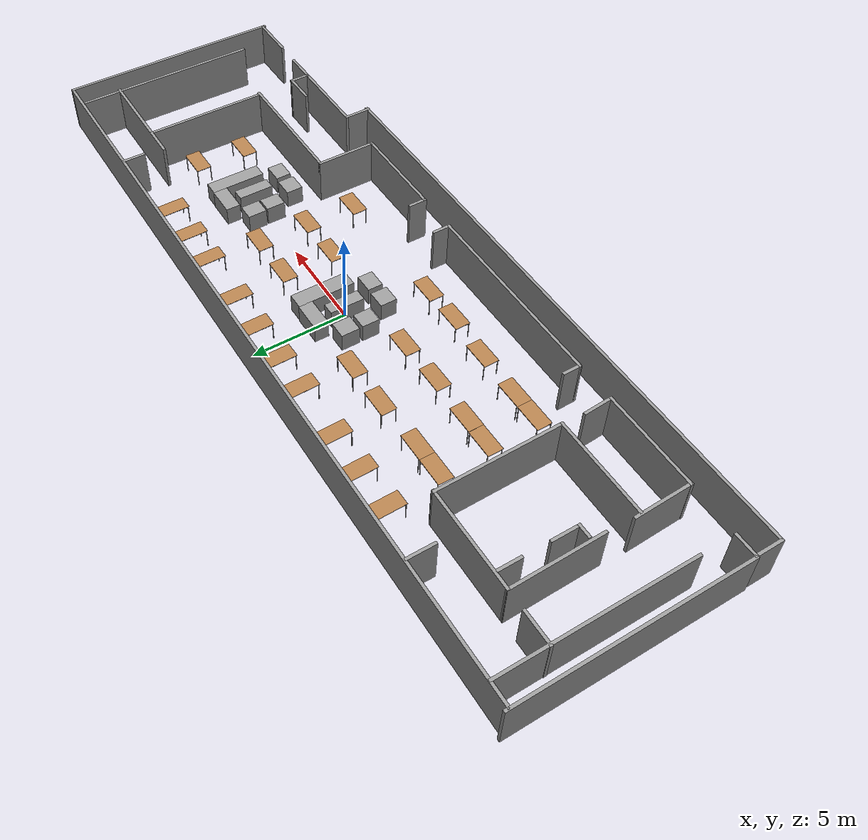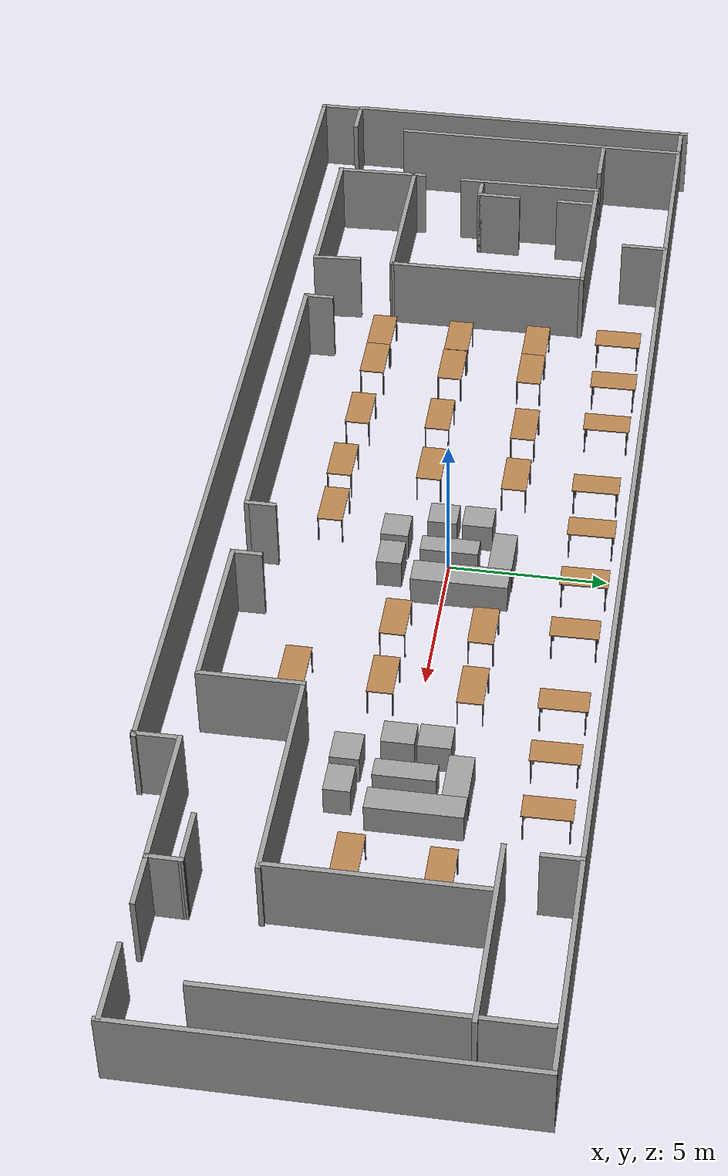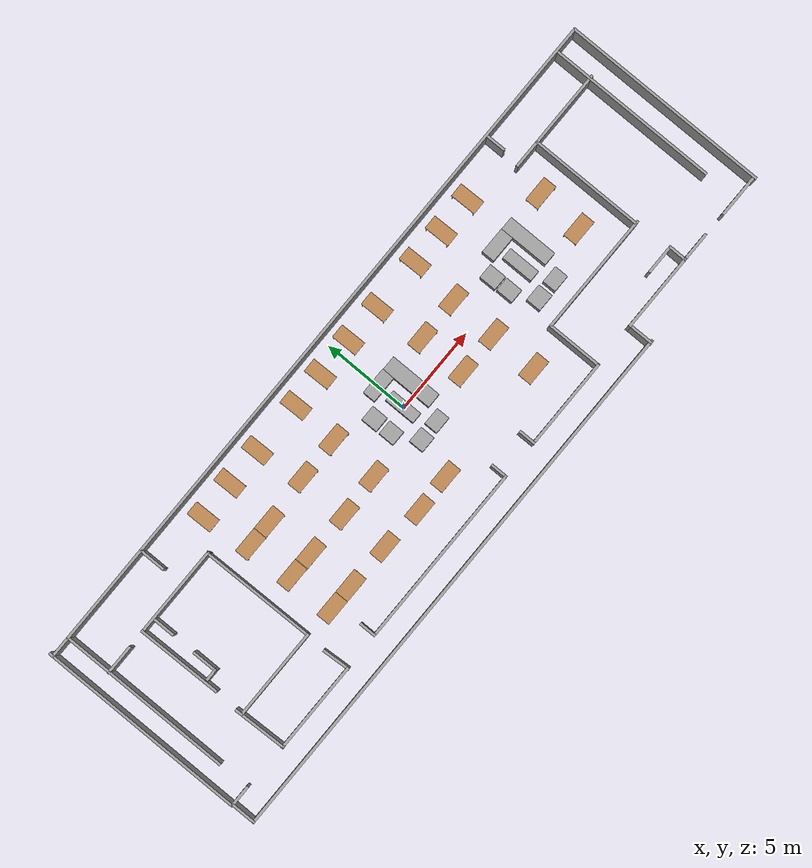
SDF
<?xml version='1.0'?>
<sdf version='1.7'>
  <model name='turtlebot3_world_V3'>
    <link name='link_0_clone'>
      <inertial>
        <mass>2.54901</mass>
        <inertia>
          <ixx>2.15345</ixx>
          <ixy>0</ixy>
          <ixz>0</ixz>
          <iyy>0.363547</iyy>
          <iyz>0</iyz>
          <izz>2.09216</izz>
        </inertia>
        <pose>0 0 0 0 -0 0</pose>
      </inertial>
      <pose>1.24013 0.549487 0.5 0 -0 0</pose>
      <visual name='visual'>
        <pose>0 0 0 0 -0 0</pose>
        <geometry>
          <box>
            <size>0.843491 3.02289 1</size>
          </box>
        </geometry>
        <material>
          <lighting>1</lighting>
          <script>
            <uri>file://media/materials/scripts/gazebo.material</uri>
            <name>Gazebo/Grey</name>
          </script>
          <shader type='pixel'/>
        </material>
        <transparency>0</transparency>
        <cast_shadows>1</cast_shadows>
      </visual>
      <collision name='collision'>
        <laser_retro>0</laser_retro>
        <max_contacts>10</max_contacts>
        <pose>0 0 0 0 -0 0</pose>
        <geometry>
          <box>
            <size>0.843491 3.02289 1</size>
          </box>
        </geometry>
        <surface>
          <friction>
            <ode>
              <mu>1</mu>
              <mu2>1</mu2>
              <fdir1>0 0 0</fdir1>
              <slip1>0</slip1>
              <slip2>0</slip2>
            </ode>
            <torsional>
              <coefficient>1</coefficient>
              <patch_radius>0</patch_radius>
              <surface_radius>0</surface_radius>
              <use_patch_radius>1</use_patch_radius>
              <ode>
                <slip>0</slip>
              </ode>
            </torsional>
          </friction>
          <bounce>
            <restitution_coefficient>0</restitution_coefficient>
            <threshold>1e+06</threshold>
          </bounce>
          <contact>
            <collide_without_contact>0</collide_without_contact>
            <collide_without_contact_bitmask>1</collide_without_contact_bitmask>
            <collide_bitmask>1</collide_bitmask>
            <ode>
              <soft_cfm>0</soft_cfm>
              <soft_erp>0.2</soft_erp>
              <kp>1e+13</kp>
              <kd>1</kd>
              <max_vel>0.01</max_vel>
              <min_depth>0</min_depth>
            </ode>
            <bullet>
              <split_impulse>1</split_impulse>
              <split_impulse_penetration_threshold>-0.01</split_impulse_penetration_threshold>
              <soft_cfm>0</soft_cfm>
              <soft_erp>0.2</soft_erp>
              <kp>1e+13</kp>
              <kd>1</kd>
            </bullet>
          </contact>
        </surface>
      </collision>
    </link>
    <link name='link_1'>
      <inertial>
        <mass>1.15926</mass>
        <inertia>
          <ixx>0.149986</ixx>
          <ixy>0</ixy>
          <ixz>0</ixz>
          <iyy>0.331691</iyy>
          <iyz>0</iyz>
          <izz>0.288468</izz>
        </inertia>
        <pose>0 0 0 0 -0 0</pose>
      </inertial>
      <pose>0.051476 1.71415 0.5 0 -0 0</pose>
      <visual name='visual'>
        <pose>0 0 0 0 -0 0</pose>
        <geometry>
          <box>
            <size>1.55997 0.743356 1</size>
          </box>
        </geometry>
        <material>
          <lighting>1</lighting>
          <script>
            <uri>file://media/materials/scripts/gazebo.material</uri>
            <name>Gazebo/Grey</name>
          </script>
          <shader type='pixel'/>
        </material>
        <transparency>0</transparency>
        <cast_shadows>1</cast_shadows>
      </visual>
      <collision name='collision'>
        <laser_retro>0</laser_retro>
        <max_contacts>10</max_contacts>
        <pose>0 0 0 0 -0 0</pose>
        <geometry>
          <box>
            <size>1.55997 0.743356 1</size>
          </box>
        </geometry>
        <surface>
          <friction>
            <ode>
              <mu>1</mu>
              <mu2>1</mu2>
              <fdir1>0 0 0</fdir1>
              <slip1>0</slip1>
              <slip2>0</slip2>
            </ode>
            <torsional>
              <coefficient>1</coefficient>
              <patch_radius>0</patch_radius>
              <surface_radius>0</surface_radius>
              <use_patch_radius>1</use_patch_radius>
              <ode>
                <slip>0</slip>
              </ode>
            </torsional>
          </friction>
          <bounce>
            <restitution_coefficient>0</restitution_coefficient>
            <threshold>1e+06</threshold>
          </bounce>
          <contact>
            <collide_without_contact>0</collide_without_contact>
            <collide_without_contact_bitmask>1</collide_without_contact_bitmask>
            <collide_bitmask>1</collide_bitmask>
            <ode>
              <soft_cfm>0</soft_cfm>
              <soft_erp>0.2</soft_erp>
              <kp>1e+13</kp>
              <kd>1</kd>
              <max_vel>0.01</max_vel>
              <min_depth>0</min_depth>
            </ode>
            <bullet>
              <split_impulse>1</split_impulse>
              <split_impulse_penetration_threshold>-0.01</split_impulse_penetration_threshold>
              <soft_cfm>0</soft_cfm>
              <soft_erp>0.2</soft_erp>
              <kp>1e+13</kp>
              <kd>1</kd>
            </bullet>
          </contact>
        </surface>
      </collision>
    </link>
    <link name='link_10'>
      <inertial>
        <mass>0.858538</mass>
        <inertia>
          <ixx>0.14309</ixx>
          <ixy>0</ixy>
          <ixz>0</ixz>
          <iyy>0.124282</iyy>
          <iyz>0</iyz>
          <izz>0.124282</izz>
        </inertia>
        <pose>0 0 0 0 -0 0</pose>
      </inertial>
      <pose>8.01063 0.76269 0.5 0 -0 0</pose>
      <visual name='visual'>
        <pose>0 0 0 0 -0 0</pose>
        <geometry>
          <box>
            <size>0.858553 1 1</size>
          </box>
        </geometry>
        <material>
          <lighting>1</lighting>
          <script>
            <uri>file://media/materials/scripts/gazebo.material</uri>
            <name>Gazebo/Grey</name>
          </script>
          <shader type='pixel'/>
        </material>
        <transparency>0</transparency>
        <cast_shadows>1</cast_shadows>
      </visual>
      <collision name='collision'>
        <laser_retro>0</laser_retro>
        <max_contacts>10</max_contacts>
        <pose>0 0 0 0 -0 0</pose>
        <geometry>
          <box>
            <size>0.858553 1 1</size>
          </box>
        </geometry>
        <surface>
          <friction>
            <ode>
              <mu>1</mu>
              <mu2>1</mu2>
              <fdir1>0 0 0</fdir1>
              <slip1>0</slip1>
              <slip2>0</slip2>
            </ode>
            <torsional>
              <coefficient>1</coefficient>
              <patch_radius>0</patch_radius>
              <surface_radius>0</surface_radius>
              <use_patch_radius>1</use_patch_radius>
              <ode>
                <slip>0</slip>
              </ode>
            </torsional>
          </friction>
          <bounce>
            <restitution_coefficient>0</restitution_coefficient>
            <threshold>1e+06</threshold>
          </bounce>
          <contact>
            <collide_without_contact>0</collide_without_contact>
            <collide_without_contact_bitmask>1</collide_without_contact_bitmask>
            <collide_bitmask>1</collide_bitmask>
            <ode>
              <soft_cfm>0</soft_cfm>
              <soft_erp>0.2</soft_erp>
              <kp>1e+13</kp>
              <kd>1</kd>
              <max_vel>0.01</max_vel>
              <min_depth>0</min_depth>
            </ode>
            <bullet>
              <split_impulse>1</split_impulse>
              <split_impulse_penetration_threshold>-0.01</split_impulse_penetration_threshold>
              <soft_cfm>0</soft_cfm>
              <soft_erp>0.2</soft_erp>
              <kp>1e+13</kp>
              <kd>1</kd>
            </bullet>
          </contact>
        </surface>
      </collision>
    </link>
    <link name='link_11'>
      <inertial>
        <mass>0.829607</mass>
        <inertia>
          <ixx>0.14157</ixx>
          <ixy>0</ixy>
          <ixz>0</ixz>
          <iyy>0.117869</iyy>
          <iyz>0</iyz>
          <izz>0.114567</izz>
        </inertia>
        <pose>0 0 0 0 -0 0</pose>
      </inertial>
      <pose>8.02619 -0.313969 0.5 0 -0 0</pose>
      <visual name='visual'>
        <pose>0 0 0 0 -0 0</pose>
        <geometry>
          <box>
            <size>0.81066 1 1.0236</size>
          </box>
        </geometry>
        <material>
          <lighting>1</lighting>
          <script>
            <uri>file://media/materials/scripts/gazebo.material</uri>
            <name>Gazebo/Grey</name>
          </script>
          <shader type='pixel'/>
        </material>
        <transparency>0</transparency>
        <cast_shadows>1</cast_shadows>
      </visual>
      <collision name='collision'>
        <laser_retro>0</laser_retro>
        <max_contacts>10</max_contacts>
        <pose>0 0 0 0 -0 0</pose>
        <geometry>
          <box>
            <size>0.81066 1 1.0236</size>
          </box>
        </geometry>
        <surface>
          <friction>
            <ode>
              <mu>1</mu>
              <mu2>1</mu2>
              <fdir1>0 0 0</fdir1>
              <slip1>0</slip1>
              <slip2>0</slip2>
            </ode>
            <torsional>
              <coefficient>1</coefficient>
              <patch_radius>0</patch_radius>
              <surface_radius>0</surface_radius>
              <use_patch_radius>1</use_patch_radius>
              <ode>
                <slip>0</slip>
              </ode>
            </torsional>
          </friction>
          <bounce>
            <restitution_coefficient>0</restitution_coefficient>
            <threshold>1e+06</threshold>
          </bounce>
          <contact>
            <collide_without_contact>0</collide_without_contact>
            <collide_without_contact_bitmask>1</collide_without_contact_bitmask>
            <collide_bitmask>1</collide_bitmask>
            <ode>
              <soft_cfm>0</soft_cfm>
              <soft_erp>0.2</soft_erp>
              <kp>1e+13</kp>
              <kd>1</kd>
              <max_vel>0.01</max_vel>
              <min_depth>0</min_depth>
            </ode>
            <bullet>
              <split_impulse>1</split_impulse>
              <split_impulse_penetration_threshold>-0.01</split_impulse_penetration_threshold>
              <soft_cfm>0</soft_cfm>
              <soft_erp>0.2</soft_erp>
              <kp>1e+13</kp>
              <kd>1</kd>
            </bullet>
          </contact>
        </surface>
      </collision>
    </link>
    <link name='link_12'>
      <inertial>
        <mass>0.805498</mass>
        <inertia>
          <ixx>0.110674</ixx>
          <ixy>0</ixy>
          <ixz>0</ixz>
          <iyy>0.13425</iyy>
          <iyz>0</iyz>
          <izz>0.110673</izz>
        </inertia>
        <pose>0 0 0 0 -0 0</pose>
      </inertial>
      <pose>9.96641 -1.75316 0.5 0 -0 0</pose>
      <visual name='visual'>
        <pose>0 0 0 0 -0 0</pose>
        <geometry>
          <box>
            <size>1 0.805462 1</size>
          </box>
        </geometry>
        <material>
          <lighting>1</lighting>
          <script>
            <uri>file://media/materials/scripts/gazebo.material</uri>
            <name>Gazebo/Grey</name>
          </script>
          <shader type='pixel'/>
        </material>
        <transparency>0</transparency>
        <cast_shadows>1</cast_shadows>
      </visual>
      <collision name='collision'>
        <laser_retro>0</laser_retro>
        <max_contacts>10</max_contacts>
        <pose>0 0 0 0 -0 0</pose>
        <geometry>
          <box>
            <size>1 0.805462 1</size>
          </box>
        </geometry>
        <surface>
          <friction>
            <ode>
              <mu>1</mu>
              <mu2>1</mu2>
              <fdir1>0 0 0</fdir1>
              <slip1>0</slip1>
              <slip2>0</slip2>
            </ode>
            <torsional>
              <coefficient>1</coefficient>
              <patch_radius>0</patch_radius>
              <surface_radius>0</surface_radius>
              <use_patch_radius>1</use_patch_radius>
              <ode>
                <slip>0</slip>
              </ode>
            </torsional>
          </friction>
          <bounce>
            <restitution_coefficient>0</restitution_coefficient>
            <threshold>1e+06</threshold>
          </bounce>
          <contact>
            <collide_without_contact>0</collide_without_contact>
            <collide_without_contact_bitmask>1</collide_without_contact_bitmask>
            <collide_bitmask>1</collide_bitmask>
            <ode>
              <soft_cfm>0</soft_cfm>
              <soft_erp>0.2</soft_erp>
              <kp>1e+13</kp>
              <kd>1</kd>
              <max_vel>0.01</max_vel>
              <min_depth>0</min_depth>
            </ode>
            <bullet>
              <split_impulse>1</split_impulse>
              <split_impulse_penetration_threshold>-0.01</split_impulse_penetration_threshold>
              <soft_cfm>0</soft_cfm>
              <soft_erp>0.2</soft_erp>
              <kp>1e+13</kp>
              <kd>1</kd>
            </bullet>
          </contact>
        </surface>
      </collision>
    </link>
    <link name='link_13'>
      <inertial>
        <mass>0.865767</mass>
        <inertia>
          <ixx>0.125697</ixx>
          <ixy>0</ixy>
          <ixz>0</ixz>
          <iyy>0.141908</iyy>
          <iyz>0</iyz>
          <izz>0.128084</izz>
        </inertia>
        <pose>0 0 0 0 -0 0</pose>
      </inertial>
      <pose>8.71811 -1.73865 0.5 0 -0 0</pose>
      <visual name='visual'>
        <pose>0 0 0 0 -0 0</pose>
        <geometry>
          <box>
            <size>1 0.880516 0.983322</size>
          </box>
        </geometry>
        <material>
          <lighting>1</lighting>
          <script>
            <uri>file://media/materials/scripts/gazebo.material</uri>
            <name>Gazebo/Grey</name>
          </script>
          <shader type='pixel'/>
        </material>
        <transparency>0</transparency>
        <cast_shadows>1</cast_shadows>
      </visual>
      <collision name='collision'>
        <laser_retro>0</laser_retro>
        <max_contacts>10</max_contacts>
        <pose>0 0 0 0 -0 0</pose>
        <geometry>
          <box>
            <size>1 0.880516 0.983322</size>
          </box>
        </geometry>
        <surface>
          <friction>
            <ode>
              <mu>1</mu>
              <mu2>1</mu2>
              <fdir1>0 0 0</fdir1>
              <slip1>0</slip1>
              <slip2>0</slip2>
            </ode>
            <torsional>
              <coefficient>1</coefficient>
              <patch_radius>0</patch_radius>
              <surface_radius>0</surface_radius>
              <use_patch_radius>1</use_patch_radius>
              <ode>
                <slip>0</slip>
              </ode>
            </torsional>
          </friction>
          <bounce>
            <restitution_coefficient>0</restitution_coefficient>
            <threshold>1e+06</threshold>
          </bounce>
          <contact>
            <collide_without_contact>0</collide_without_contact>
            <collide_without_contact_bitmask>1</collide_without_contact_bitmask>
            <collide_bitmask>1</collide_bitmask>
            <ode>
              <soft_cfm>0</soft_cfm>
              <soft_erp>0.2</soft_erp>
              <kp>1e+13</kp>
              <kd>1</kd>
              <max_vel>0.01</max_vel>
              <min_depth>0</min_depth>
            </ode>
            <bullet>
              <split_impulse>1</split_impulse>
              <split_impulse_penetration_threshold>-0.01</split_impulse_penetration_threshold>
              <soft_cfm>0</soft_cfm>
              <soft_erp>0.2</soft_erp>
              <kp>1e+13</kp>
              <kd>1</kd>
            </bullet>
          </contact>
        </surface>
      </collision>
    </link>
    <link name='link_2'>
      <inertial>
        <mass>1.15777</mass>
        <inertia>
          <ixx>0.418048</ixx>
          <ixy>0</ixy>
          <ixz>0</ixz>
          <iyy>0.135287</iyy>
          <iyz>0</iyz>
          <izz>0.360373</izz>
        </inertia>
        <pose>0 0 0 0 -0 0</pose>
      </inertial>
      <pose>0.004407 0.050983 0.5 0 -0 0</pose>
      <visual name='visual'>
        <pose>0 0 0 0 -0 0</pose>
        <geometry>
          <box>
            <size>0.634205 1.82564 1</size>
          </box>
        </geometry>
        <material>
          <lighting>1</lighting>
          <script>
            <uri>file://media/materials/scripts/gazebo.material</uri>
            <name>Gazebo/Grey</name>
          </script>
          <shader type='pixel'/>
        </material>
        <transparency>0</transparency>
        <cast_shadows>1</cast_shadows>
      </visual>
      <collision name='collision'>
        <laser_retro>0</laser_retro>
        <max_contacts>10</max_contacts>
        <pose>0 0 0 0 -0 0</pose>
        <geometry>
          <box>
            <size>0.634205 1.82564 1</size>
          </box>
        </geometry>
        <surface>
          <friction>
            <ode>
              <mu>1</mu>
              <mu2>1</mu2>
              <fdir1>0 0 0</fdir1>
              <slip1>0</slip1>
              <slip2>0</slip2>
            </ode>
            <torsional>
              <coefficient>1</coefficient>
              <patch_radius>0</patch_radius>
              <surface_radius>0</surface_radius>
              <use_patch_radius>1</use_patch_radius>
              <ode>
                <slip>0</slip>
              </ode>
            </torsional>
          </friction>
          <bounce>
            <restitution_coefficient>0</restitution_coefficient>
            <threshold>1e+06</threshold>
          </bounce>
          <contact>
            <collide_without_contact>0</collide_without_contact>
            <collide_without_contact_bitmask>1</collide_without_contact_bitmask>
            <collide_bitmask>1</collide_bitmask>
            <ode>
              <soft_cfm>0</soft_cfm>
              <soft_erp>0.2</soft_erp>
              <kp>1e+13</kp>
              <kd>1</kd>
              <max_vel>0.01</max_vel>
              <min_depth>0</min_depth>
            </ode>
            <bullet>
              <split_impulse>1</split_impulse>
              <split_impulse_penetration_threshold>-0.01</split_impulse_penetration_threshold>
              <soft_cfm>0</soft_cfm>
              <soft_erp>0.2</soft_erp>
              <kp>1e+13</kp>
              <kd>1</kd>
            </bullet>
          </contact>
        </surface>
      </collision>
    </link>
    <link name='link_3'>
      <inertial>
        <mass>0.787073</mass>
        <inertia>
          <ixx>0.106222</ixx>
          <ixy>0</ixy>
          <ixz>0</ixz>
          <iyy>0.131179</iyy>
          <iyz>0</iyz>
          <izz>0.106222</izz>
        </inertia>
        <pose>0 0 0 0 -0 0</pose>
      </inertial>
      <pose>0.554076 -1.72385 0.5 0 -0 0</pose>
      <visual name='visual'>
        <pose>0 0 0 0 -0 0</pose>
        <geometry>
          <box>
            <size>1 0.787081 1</size>
          </box>
        </geometry>
        <material>
          <lighting>1</lighting>
          <script>
            <uri>file://media/materials/scripts/gazebo.material</uri>
            <name>Gazebo/Grey</name>
          </script>
          <shader type='pixel'/>
        </material>
        <transparency>0</transparency>
        <cast_shadows>1</cast_shadows>
      </visual>
      <collision name='collision'>
        <laser_retro>0</laser_retro>
        <max_contacts>10</max_contacts>
        <pose>0 0 0 0 -0 0</pose>
        <geometry>
          <box>
            <size>1 0.787081 1</size>
          </box>
        </geometry>
        <surface>
          <friction>
            <ode>
              <mu>1</mu>
              <mu2>1</mu2>
              <fdir1>0 0 0</fdir1>
              <slip1>0</slip1>
              <slip2>0</slip2>
            </ode>
            <torsional>
              <coefficient>1</coefficient>
              <patch_radius>0</patch_radius>
              <surface_radius>0</surface_radius>
              <use_patch_radius>1</use_patch_radius>
              <ode>
                <slip>0</slip>
              </ode>
            </torsional>
          </friction>
          <bounce>
            <restitution_coefficient>0</restitution_coefficient>
            <threshold>1e+06</threshold>
          </bounce>
          <contact>
            <collide_without_contact>0</collide_without_contact>
            <collide_without_contact_bitmask>1</collide_without_contact_bitmask>
            <collide_bitmask>1</collide_bitmask>
            <ode>
              <soft_cfm>0</soft_cfm>
              <soft_erp>0.2</soft_erp>
              <kp>1e+13</kp>
              <kd>1</kd>
              <max_vel>0.01</max_vel>
              <min_depth>0</min_depth>
            </ode>
            <bullet>
              <split_impulse>1</split_impulse>
              <split_impulse_penetration_threshold>-0.01</split_impulse_penetration_threshold>
              <soft_cfm>0</soft_cfm>
              <soft_erp>0.2</soft_erp>
              <kp>1e+13</kp>
              <kd>1</kd>
            </bullet>
          </contact>
        </surface>
      </collision>
    </link>
    <link name='link_4'>
      <inertial>
        <mass>0.823135</mass>
        <inertia>
          <ixx>0.12112</ixx>
          <ixy>0</ixy>
          <ixz>0</ixz>
          <iyy>0.129293</iyy>
          <iyz>0</iyz>
          <izz>0.113223</izz>
        </inertia>
        <pose>0 0 0 0 -0 0</pose>
      </inertial>
      <pose>-0.670921 -1.74276 0.5 0 -0 0</pose>
      <visual name='visual'>
        <pose>0 0 0 0 -0 0</pose>
        <geometry>
          <box>
            <size>0.940681 0.875064 1</size>
          </box>
        </geometry>
        <material>
          <lighting>1</lighting>
          <script>
            <uri>file://media/materials/scripts/gazebo.material</uri>
            <name>Gazebo/Grey</name>
          </script>
          <shader type='pixel'/>
        </material>
        <transparency>0</transparency>
        <cast_shadows>1</cast_shadows>
      </visual>
      <collision name='collision'>
        <laser_retro>0</laser_retro>
        <max_contacts>10</max_contacts>
        <pose>0 0 0 0 -0 0</pose>
        <geometry>
          <box>
            <size>0.940681 0.875064 1</size>
          </box>
        </geometry>
        <surface>
          <friction>
            <ode>
              <mu>1</mu>
              <mu2>1</mu2>
              <fdir1>0 0 0</fdir1>
              <slip1>0</slip1>
              <slip2>0</slip2>
            </ode>
            <torsional>
              <coefficient>1</coefficient>
              <patch_radius>0</patch_radius>
              <surface_radius>0</surface_radius>
              <use_patch_radius>1</use_patch_radius>
              <ode>
                <slip>0</slip>
              </ode>
            </torsional>
          </friction>
          <bounce>
            <restitution_coefficient>0</restitution_coefficient>
            <threshold>1e+06</threshold>
          </bounce>
          <contact>
            <collide_without_contact>0</collide_without_contact>
            <collide_without_contact_bitmask>1</collide_without_contact_bitmask>
            <collide_bitmask>1</collide_bitmask>
            <ode>
              <soft_cfm>0</soft_cfm>
              <soft_erp>0.2</soft_erp>
              <kp>1e+13</kp>
              <kd>1</kd>
              <max_vel>0.01</max_vel>
              <min_depth>0</min_depth>
            </ode>
            <bullet>
              <split_impulse>1</split_impulse>
              <split_impulse_penetration_threshold>-0.01</split_impulse_penetration_threshold>
              <soft_cfm>0</soft_cfm>
              <soft_erp>0.2</soft_erp>
              <kp>1e+13</kp>
              <kd>1</kd>
            </bullet>
          </contact>
        </surface>
      </collision>
    </link>
    <link name='link_5'>
      <inertial>
        <mass>0.796798</mass>
        <inertia>
          <ixx>0.123086</ixx>
          <ixy>0</ixy>
          <ixz>0</ixz>
          <iyy>0.115781</iyy>
          <iyz>0</iyz>
          <izz>0.106067</izz>
        </inertia>
        <pose>0 0 0 0 -0 0</pose>
      </inertial>
      <pose>-1.39789 -0.336219 0.5 0 -0 0</pose>
      <visual name='visual'>
        <pose>0 0 0 0 -0 0</pose>
        <geometry>
          <box>
            <size>0.862375 0.923961 1</size>
          </box>
        </geometry>
        <material>
          <lighting>1</lighting>
          <script>
            <uri>file://media/materials/scripts/gazebo.material</uri>
            <name>Gazebo/Grey</name>
          </script>
          <shader type='pixel'/>
        </material>
        <transparency>0</transparency>
        <cast_shadows>1</cast_shadows>
      </visual>
      <collision name='collision'>
        <laser_retro>0</laser_retro>
        <max_contacts>10</max_contacts>
        <pose>0 0 0 0 -0 0</pose>
        <geometry>
          <box>
            <size>0.862375 0.923961 1</size>
          </box>
        </geometry>
        <surface>
          <friction>
            <ode>
              <mu>1</mu>
              <mu2>1</mu2>
              <fdir1>0 0 0</fdir1>
              <slip1>0</slip1>
              <slip2>0</slip2>
            </ode>
            <torsional>
              <coefficient>1</coefficient>
              <patch_radius>0</patch_radius>
              <surface_radius>0</surface_radius>
              <use_patch_radius>1</use_patch_radius>
              <ode>
                <slip>0</slip>
              </ode>
            </torsional>
          </friction>
          <bounce>
            <restitution_coefficient>0</restitution_coefficient>
            <threshold>1e+06</threshold>
          </bounce>
          <contact>
            <collide_without_contact>0</collide_without_contact>
            <collide_without_contact_bitmask>1</collide_without_contact_bitmask>
            <collide_bitmask>1</collide_bitmask>
            <ode>
              <soft_cfm>0</soft_cfm>
              <soft_erp>0.2</soft_erp>
              <kp>1e+13</kp>
              <kd>1</kd>
              <max_vel>0.01</max_vel>
              <min_depth>0</min_depth>
            </ode>
            <bullet>
              <split_impulse>1</split_impulse>
              <split_impulse_penetration_threshold>-0.01</split_impulse_penetration_threshold>
              <soft_cfm>0</soft_cfm>
              <soft_erp>0.2</soft_erp>
              <kp>1e+13</kp>
              <kd>1</kd>
            </bullet>
          </contact>
        </surface>
      </collision>
    </link>
    <link name='link_6'>
      <inertial>
        <mass>0.860177</mass>
        <inertia>
          <ixx>0.137972</ixx>
          <ixy>0</ixy>
          <ixz>0</ixz>
          <iyy>0.129036</iyy>
          <iyz>0</iyz>
          <izz>0.123645</izz>
        </inertia>
        <pose>0 0 0 0 -0 0</pose>
      </inertial>
      <pose>-1.394 0.77756 0.5 0 -0 0</pose>
      <visual name='visual'>
        <pose>0 0 0 0 -0 0</pose>
        <geometry>
          <box>
            <size>0.894497 0.961663 1</size>
          </box>
        </geometry>
        <material>
          <lighting>1</lighting>
          <script>
            <uri>file://media/materials/scripts/gazebo.material</uri>
            <name>Gazebo/Grey</name>
          </script>
          <shader type='pixel'/>
        </material>
        <transparency>0</transparency>
        <cast_shadows>1</cast_shadows>
      </visual>
      <collision name='collision'>
        <laser_retro>0</laser_retro>
        <max_contacts>10</max_contacts>
        <pose>0 0 0 0 -0 0</pose>
        <geometry>
          <box>
            <size>0.894497 0.961663 1</size>
          </box>
        </geometry>
        <surface>
          <friction>
            <ode>
              <mu>1</mu>
              <mu2>1</mu2>
              <fdir1>0 0 0</fdir1>
              <slip1>0</slip1>
              <slip2>0</slip2>
            </ode>
            <torsional>
              <coefficient>1</coefficient>
              <patch_radius>0</patch_radius>
              <surface_radius>0</surface_radius>
              <use_patch_radius>1</use_patch_radius>
              <ode>
                <slip>0</slip>
              </ode>
            </torsional>
          </friction>
          <bounce>
            <restitution_coefficient>0</restitution_coefficient>
            <threshold>1e+06</threshold>
          </bounce>
          <contact>
            <collide_without_contact>0</collide_without_contact>
            <collide_without_contact_bitmask>1</collide_without_contact_bitmask>
            <collide_bitmask>1</collide_bitmask>
            <ode>
              <soft_cfm>0</soft_cfm>
              <soft_erp>0.2</soft_erp>
              <kp>1e+13</kp>
              <kd>1</kd>
              <max_vel>0.01</max_vel>
              <min_depth>0</min_depth>
            </ode>
            <bullet>
              <split_impulse>1</split_impulse>
              <split_impulse_penetration_threshold>-0.01</split_impulse_penetration_threshold>
              <soft_cfm>0</soft_cfm>
              <soft_erp>0.2</soft_erp>
              <kp>1e+13</kp>
              <kd>1</kd>
            </bullet>
          </contact>
        </surface>
      </collision>
    </link>
    <link name='link_7'>
      <inertial>
        <mass>2.23687</mass>
        <inertia>
          <ixx>1.73409</ixx>
          <ixy>0</ixy>
          <ixz>0</ixz>
          <iyy>0.29873</iyy>
          <iyz>0</iyz>
          <izz>1.66001</izz>
        </inertia>
        <pose>0 0 0 0 -0 0</pose>
      </inertial>
      <pose>10.5817 0.539907 0.5 0 -0 0</pose>
      <visual name='visual'>
        <pose>0 0 0 0 -0 0</pose>
        <geometry>
          <box>
            <size>0.77626 2.88145 1</size>
          </box>
        </geometry>
        <material>
          <lighting>1</lighting>
          <script>
            <uri>file://media/materials/scripts/gazebo.material</uri>
            <name>Gazebo/Grey</name>
          </script>
          <shader type='pixel'/>
        </material>
        <transparency>0</transparency>
        <cast_shadows>1</cast_shadows>
      </visual>
      <collision name='collision'>
        <laser_retro>0</laser_retro>
        <max_contacts>10</max_contacts>
        <pose>0 0 0 0 -0 0</pose>
        <geometry>
          <box>
            <size>0.77626 2.88145 1</size>
          </box>
        </geometry>
        <surface>
          <friction>
            <ode>
              <mu>1</mu>
              <mu2>1</mu2>
              <fdir1>0 0 0</fdir1>
              <slip1>0</slip1>
              <slip2>0</slip2>
            </ode>
            <torsional>
              <coefficient>1</coefficient>
              <patch_radius>0</patch_radius>
              <surface_radius>0</surface_radius>
              <use_patch_radius>1</use_patch_radius>
              <ode>
                <slip>0</slip>
              </ode>
            </torsional>
          </friction>
          <bounce>
            <restitution_coefficient>0</restitution_coefficient>
            <threshold>1e+06</threshold>
          </bounce>
          <contact>
            <collide_without_contact>0</collide_without_contact>
            <collide_without_contact_bitmask>1</collide_without_contact_bitmask>
            <collide_bitmask>1</collide_bitmask>
            <ode>
              <soft_cfm>0</soft_cfm>
              <soft_erp>0.2</soft_erp>
              <kp>1e+13</kp>
              <kd>1</kd>
              <max_vel>0.01</max_vel>
              <min_depth>0</min_depth>
            </ode>
            <bullet>
              <split_impulse>1</split_impulse>
              <split_impulse_penetration_threshold>-0.01</split_impulse_penetration_threshold>
              <soft_cfm>0</soft_cfm>
              <soft_erp>0.2</soft_erp>
              <kp>1e+13</kp>
              <kd>1</kd>
            </bullet>
          </contact>
        </surface>
      </collision>
    </link>
    <link name='link_8'>
      <inertial>
        <mass>1.16467</mass>
        <inertia>
          <ixx>0.153025</ixx>
          <ixy>0</ixy>
          <ixz>0</ixz>
          <iyy>0.325368</iyy>
          <iyz>0</iyz>
          <izz>0.284282</izz>
        </inertia>
        <pose>0 0 0 0 -0 0</pose>
      </inertial>
      <pose>9.42775 1.61838 0.5 0 -0 0</pose>
      <visual name='visual'>
        <pose>0 0 0 0 -0 0</pose>
        <geometry>
          <box>
            <size>1.53375 0.75939 0.999999</size>
          </box>
        </geometry>
        <material>
          <lighting>1</lighting>
          <script>
            <uri>file://media/materials/scripts/gazebo.material</uri>
            <name>Gazebo/Grey</name>
          </script>
          <shader type='pixel'/>
        </material>
        <transparency>0</transparency>
        <cast_shadows>1</cast_shadows>
      </visual>
      <collision name='collision'>
        <laser_retro>0</laser_retro>
        <max_contacts>10</max_contacts>
        <pose>0 0 0 0 -0 0</pose>
        <geometry>
          <box>
            <size>1.53375 0.75939 0.999999</size>
          </box>
        </geometry>
        <surface>
          <friction>
            <ode>
              <mu>1</mu>
              <mu2>1</mu2>
              <fdir1>0 0 0</fdir1>
              <slip1>0</slip1>
              <slip2>0</slip2>
            </ode>
            <torsional>
              <coefficient>1</coefficient>
              <patch_radius>0</patch_radius>
              <surface_radius>0</surface_radius>
              <use_patch_radius>1</use_patch_radius>
              <ode>
                <slip>0</slip>
              </ode>
            </torsional>
          </friction>
          <bounce>
            <restitution_coefficient>0</restitution_coefficient>
            <threshold>1e+06</threshold>
          </bounce>
          <contact>
            <collide_without_contact>0</collide_without_contact>
            <collide_without_contact_bitmask>1</collide_without_contact_bitmask>
            <collide_bitmask>1</collide_bitmask>
            <ode>
              <soft_cfm>0</soft_cfm>
              <soft_erp>0.2</soft_erp>
              <kp>1e+13</kp>
              <kd>1</kd>
              <max_vel>0.01</max_vel>
              <min_depth>0</min_depth>
            </ode>
            <bullet>
              <split_impulse>1</split_impulse>
              <split_impulse_penetration_threshold>-0.01</split_impulse_penetration_threshold>
              <soft_cfm>0</soft_cfm>
              <soft_erp>0.2</soft_erp>
              <kp>1e+13</kp>
              <kd>1</kd>
            </bullet>
          </contact>
        </surface>
      </collision>
    </link>
    <link name='link_9'>
      <inertial>
        <mass>1.18157</mass>
        <inertia>
          <ixx>0.436927</ixx>
          <ixy>0</ixy>
          <ixz>0</ixz>
          <iyy>0.138453</iyy>
          <iyz>0</iyz>
          <izz>0.378452</izz>
        </inertia>
        <pose>0 0 0 0 -0 0</pose>
      </inertial>
      <pose>9.40553 0.06989 0.5 0 -0 0</pose>
      <visual name='visual'>
        <pose>0 0 0 0 -0 0</pose>
        <geometry>
          <box>
            <size>0.637281 1.85403 1</size>
          </box>
        </geometry>
        <material>
          <lighting>1</lighting>
          <script>
            <uri>file://media/materials/scripts/gazebo.material</uri>
            <name>Gazebo/Grey</name>
          </script>
          <shader type='pixel'/>
        </material>
        <transparency>0</transparency>
        <cast_shadows>1</cast_shadows>
      </visual>
      <collision name='collision'>
        <laser_retro>0</laser_retro>
        <max_contacts>10</max_contacts>
        <pose>0 0 0 0 -0 0</pose>
        <geometry>
          <box>
            <size>0.637281 1.85403 1</size>
          </box>
        </geometry>
        <surface>
          <friction>
            <ode>
              <mu>1</mu>
              <mu2>1</mu2>
              <fdir1>0 0 0</fdir1>
              <slip1>0</slip1>
              <slip2>0</slip2>
            </ode>
            <torsional>
              <coefficient>1</coefficient>
              <patch_radius>0</patch_radius>
              <surface_radius>0</surface_radius>
              <use_patch_radius>1</use_patch_radius>
              <ode>
                <slip>0</slip>
              </ode>
            </torsional>
          </friction>
          <bounce>
            <restitution_coefficient>0</restitution_coefficient>
            <threshold>1e+06</threshold>
          </bounce>
          <contact>
            <collide_without_contact>0</collide_without_contact>
            <collide_without_contact_bitmask>1</collide_without_contact_bitmask>
            <collide_bitmask>1</collide_bitmask>
            <ode>
              <soft_cfm>0</soft_cfm>
              <soft_erp>0.2</soft_erp>
              <kp>1e+13</kp>
              <kd>1</kd>
              <max_vel>0.01</max_vel>
              <min_depth>0</min_depth>
            </ode>
            <bullet>
              <split_impulse>1</split_impulse>
              <split_impulse_penetration_threshold>-0.01</split_impulse_penetration_threshold>
              <soft_cfm>0</soft_cfm>
              <soft_erp>0.2</soft_erp>
              <kp>1e+13</kp>
              <kd>1</kd>
            </bullet>
          </contact>
        </surface>
      </collision>
    </link>
    <link name='turtlebot3_world_1::The_Project_Hub_Building::Wall_0'>
      <pose>-17.0813 -4.7815 0 0 0 -1.54154</pose>
      <self_collide>0</self_collide>
      <enable_wind>0</enable_wind>
      <kinematic>0</kinematic>
      <visual name='Wall_0_Visual'>
        <pose>0 0 1.25 0 -0 0</pose>
        <geometry>
          <box>
            <size>3.11558 0.15 2.5</size>
          </box>
        </geometry>
        <material>
          <script>
            <uri>file://media/materials/scripts/gazebo.material</uri>
            <name>Gazebo/Grey</name>
          </script>
          <ambient>1 1 1 1</ambient>
          <shader type='pixel'/>
        </material>
        <meta>
          <layer>0</layer>
        </meta>
        <transparency>0</transparency>
        <cast_shadows>1</cast_shadows>
      </visual>
      <collision name='Wall_0_Collision'>
        <laser_retro>0</laser_retro>
        <max_contacts>10</max_contacts>
        <pose>0 0 1.25 0 -0 0</pose>
        <geometry>
          <box>
            <size>3.11558 0.15 2.5</size>
          </box>
        </geometry>
        <surface>
          <friction>
            <ode>
              <mu>1</mu>
              <mu2>1</mu2>
              <fdir1>0 0 0</fdir1>
              <slip1>0</slip1>
              <slip2>0</slip2>
            </ode>
            <torsional>
              <coefficient>1</coefficient>
              <patch_radius>0</patch_radius>
              <surface_radius>0</surface_radius>
              <use_patch_radius>1</use_patch_radius>
              <ode>
                <slip>0</slip>
              </ode>
            </torsional>
          </friction>
          <bounce>
            <restitution_coefficient>0</restitution_coefficient>
            <threshold>1e+06</threshold>
          </bounce>
          <contact>
            <collide_without_contact>0</collide_without_contact>
            <collide_without_contact_bitmask>1</collide_without_contact_bitmask>
            <collide_bitmask>1</collide_bitmask>
            <ode>
              <soft_cfm>0</soft_cfm>
              <soft_erp>0.2</soft_erp>
              <kp>1e+13</kp>
              <kd>1</kd>
              <max_vel>0.01</max_vel>
              <min_depth>0</min_depth>
            </ode>
            <bullet>
              <split_impulse>1</split_impulse>
              <split_impulse_penetration_threshold>-0.01</split_impulse_penetration_threshold>
              <soft_cfm>0</soft_cfm>
              <soft_erp>0.2</soft_erp>
              <kp>1e+13</kp>
              <kd>1</kd>
            </bullet>
          </contact>
        </surface>
      </collision>
    </link>
    <link name='turtlebot3_world_1::The_Project_Hub_Building::Wall_1'>
      <pose>-14.5053 -6.2463 0 0 -0 0</pose>
      <self_collide>0</self_collide>
      <enable_wind>0</enable_wind>
      <kinematic>0</kinematic>
      <visual name='Wall_1_Visual'>
        <pose>0 0 1.25 0 -0 0</pose>
        <geometry>
          <box>
            <size>5.25 0.15 2.5</size>
          </box>
        </geometry>
        <material>
          <script>
            <uri>file://media/materials/scripts/gazebo.material</uri>
            <name>Gazebo/Grey</name>
          </script>
          <ambient>1 1 1 1</ambient>
          <shader type='pixel'/>
        </material>
        <meta>
          <layer>0</layer>
        </meta>
        <transparency>0</transparency>
        <cast_shadows>1</cast_shadows>
      </visual>
      <collision name='Wall_1_Collision'>
        <laser_retro>0</laser_retro>
        <max_contacts>10</max_contacts>
        <pose>0 0 1.25 0 -0 0</pose>
        <geometry>
          <box>
            <size>5.25 0.15 2.5</size>
          </box>
        </geometry>
        <surface>
          <friction>
            <ode>
              <mu>1</mu>
              <mu2>1</mu2>
              <fdir1>0 0 0</fdir1>
              <slip1>0</slip1>
              <slip2>0</slip2>
            </ode>
            <torsional>
              <coefficient>1</coefficient>
              <patch_radius>0</patch_radius>
              <surface_radius>0</surface_radius>
              <use_patch_radius>1</use_patch_radius>
              <ode>
                <slip>0</slip>
              </ode>
            </torsional>
          </friction>
          <bounce>
            <restitution_coefficient>0</restitution_coefficient>
            <threshold>1e+06</threshold>
          </bounce>
          <contact>
            <collide_without_contact>0</collide_without_contact>
            <collide_without_contact_bitmask>1</collide_without_contact_bitmask>
            <collide_bitmask>1</collide_bitmask>
            <ode>
              <soft_cfm>0</soft_cfm>
              <soft_erp>0.2</soft_erp>
              <kp>1e+13</kp>
              <kd>1</kd>
              <max_vel>0.01</max_vel>
              <min_depth>0</min_depth>
            </ode>
            <bullet>
              <split_impulse>1</split_impulse>
              <split_impulse_penetration_threshold>-0.01</split_impulse_penetration_threshold>
              <soft_cfm>0</soft_cfm>
              <soft_erp>0.2</soft_erp>
              <kp>1e+13</kp>
              <kd>1</kd>
            </bullet>
          </contact>
        </surface>
      </collision>
    </link>
    <link name='turtlebot3_world_1::The_Project_Hub_Building::Wall_10'>
      <pose>7.84408 -4.67436 0 0 -0 1.5708</pose>
      <self_collide>0</self_collide>
      <enable_wind>0</enable_wind>
      <kinematic>0</kinematic>
      <visual name='Wall_10_Visual'>
        <pose>0 0 1.25 0 -0 0</pose>
        <geometry>
          <box>
            <size>3.25 0.15 2.5</size>
          </box>
        </geometry>
        <material>
          <script>
            <uri>file://media/materials/scripts/gazebo.material</uri>
            <name>Gazebo/Grey</name>
          </script>
          <ambient>1 1 1 1</ambient>
          <shader type='pixel'/>
        </material>
        <meta>
          <layer>0</layer>
        </meta>
        <transparency>0</transparency>
        <cast_shadows>1</cast_shadows>
      </visual>
      <collision name='Wall_10_Collision'>
        <laser_retro>0</laser_retro>
        <max_contacts>10</max_contacts>
        <pose>0 0 1.25 0 -0 0</pose>
        <geometry>
          <box>
            <size>3.25 0.15 2.5</size>
          </box>
        </geometry>
        <surface>
          <friction>
            <ode>
              <mu>1</mu>
              <mu2>1</mu2>
              <fdir1>0 0 0</fdir1>
              <slip1>0</slip1>
              <slip2>0</slip2>
            </ode>
            <torsional>
              <coefficient>1</coefficient>
              <patch_radius>0</patch_radius>
              <surface_radius>0</surface_radius>
              <use_patch_radius>1</use_patch_radius>
              <ode>
                <slip>0</slip>
              </ode>
            </torsional>
          </friction>
          <bounce>
            <restitution_coefficient>0</restitution_coefficient>
            <threshold>1e+06</threshold>
          </bounce>
          <contact>
            <collide_without_contact>0</collide_without_contact>
            <collide_without_contact_bitmask>1</collide_without_contact_bitmask>
            <collide_bitmask>1</collide_bitmask>
            <ode>
              <soft_cfm>0</soft_cfm>
              <soft_erp>0.2</soft_erp>
              <kp>1e+13</kp>
              <kd>1</kd>
              <max_vel>0.01</max_vel>
              <min_depth>0</min_depth>
            </ode>
            <bullet>
              <split_impulse>1</split_impulse>
              <split_impulse_penetration_threshold>-0.01</split_impulse_penetration_threshold>
              <soft_cfm>0</soft_cfm>
              <soft_erp>0.2</soft_erp>
              <kp>1e+13</kp>
              <kd>1</kd>
            </bullet>
          </contact>
        </surface>
      </collision>
    </link>
    <link name='turtlebot3_world_1::The_Project_Hub_Building::Wall_11'>
      <pose>11.2691 -3.12436 0 0 -0 0</pose>
      <self_collide>0</self_collide>
      <enable_wind>0</enable_wind>
      <kinematic>0</kinematic>
      <visual name='Wall_11_Visual'>
        <pose>0 0 1.25 0 -0 0</pose>
        <geometry>
          <box>
            <size>7 0.15 2.5</size>
          </box>
        </geometry>
        <material>
          <script>
            <uri>file://media/materials/scripts/gazebo.material</uri>
            <name>Gazebo/Grey</name>
          </script>
          <ambient>1 1 1 1</ambient>
          <shader type='pixel'/>
        </material>
        <meta>
          <layer>0</layer>
        </meta>
        <transparency>0</transparency>
        <cast_shadows>1</cast_shadows>
      </visual>
      <collision name='Wall_11_Collision'>
        <laser_retro>0</laser_retro>
        <max_contacts>10</max_contacts>
        <pose>0 0 1.25 0 -0 0</pose>
        <geometry>
          <box>
            <size>7 0.15 2.5</size>
          </box>
        </geometry>
        <surface>
          <friction>
            <ode>
              <mu>1</mu>
              <mu2>1</mu2>
              <fdir1>0 0 0</fdir1>
              <slip1>0</slip1>
              <slip2>0</slip2>
            </ode>
            <torsional>
              <coefficient>1</coefficient>
              <patch_radius>0</patch_radius>
              <surface_radius>0</surface_radius>
              <use_patch_radius>1</use_patch_radius>
              <ode>
                <slip>0</slip>
              </ode>
            </torsional>
          </friction>
          <bounce>
            <restitution_coefficient>0</restitution_coefficient>
            <threshold>1e+06</threshold>
          </bounce>
          <contact>
            <collide_without_contact>0</collide_without_contact>
            <collide_without_contact_bitmask>1</collide_without_contact_bitmask>
            <collide_bitmask>1</collide_bitmask>
            <ode>
              <soft_cfm>0</soft_cfm>
              <soft_erp>0.2</soft_erp>
              <kp>1e+13</kp>
              <kd>1</kd>
              <max_vel>0.01</max_vel>
              <min_depth>0</min_depth>
            </ode>
            <bullet>
              <split_impulse>1</split_impulse>
              <split_impulse_penetration_threshold>-0.01</split_impulse_penetration_threshold>
              <soft_cfm>0</soft_cfm>
              <soft_erp>0.2</soft_erp>
              <kp>1e+13</kp>
              <kd>1</kd>
            </bullet>
          </contact>
        </surface>
      </collision>
    </link>
    <link name='turtlebot3_world_1::The_Project_Hub_Building::Wall_13'>
      <pose>-0.327684 5.5353 0 0 -0 0</pose>
      <self_collide>0</self_collide>
      <enable_wind>0</enable_wind>
      <kinematic>0</kinematic>
      <visual name='Wall_13_Visual'>
        <pose>0 0 1.25 0 -0 0</pose>
        <geometry>
          <box>
            <size>41.25 0.15 2.5</size>
          </box>
        </geometry>
        <material>
          <script>
            <uri>file://media/materials/scripts/gazebo.material</uri>
            <name>Gazebo/Grey</name>
          </script>
          <ambient>1 1 1 1</ambient>
          <shader type='pixel'/>
        </material>
        <meta>
          <layer>0</layer>
        </meta>
        <transparency>0</transparency>
        <cast_shadows>1</cast_shadows>
      </visual>
      <collision name='Wall_13_Collision'>
        <laser_retro>0</laser_retro>
        <max_contacts>10</max_contacts>
        <pose>0 0 1.25 0 -0 0</pose>
        <geometry>
          <box>
            <size>41.25 0.15 2.5</size>
          </box>
        </geometry>
        <surface>
          <friction>
            <ode>
              <mu>1</mu>
              <mu2>1</mu2>
              <fdir1>0 0 0</fdir1>
              <slip1>0</slip1>
              <slip2>0</slip2>
            </ode>
            <torsional>
              <coefficient>1</coefficient>
              <patch_radius>0</patch_radius>
              <surface_radius>0</surface_radius>
              <use_patch_radius>1</use_patch_radius>
              <ode>
                <slip>0</slip>
              </ode>
            </torsional>
          </friction>
          <bounce>
            <restitution_coefficient>0</restitution_coefficient>
            <threshold>1e+06</threshold>
          </bounce>
          <contact>
            <collide_without_contact>0</collide_without_contact>
            <collide_without_contact_bitmask>1</collide_without_contact_bitmask>
            <collide_bitmask>1</collide_bitmask>
            <ode>
              <soft_cfm>0</soft_cfm>
              <soft_erp>0.2</soft_erp>
              <kp>1e+13</kp>
              <kd>1</kd>
              <max_vel>0.01</max_vel>
              <min_depth>0</min_depth>
            </ode>
            <bullet>
              <split_impulse>1</split_impulse>
              <split_impulse_penetration_threshold>-0.01</split_impulse_penetration_threshold>
              <soft_cfm>0</soft_cfm>
              <soft_erp>0.2</soft_erp>
              <kp>1e+13</kp>
              <kd>1</kd>
            </bullet>
          </contact>
        </surface>
      </collision>
    </link>
    <link name='turtlebot3_world_1::The_Project_Hub_Building::Wall_15'>
      <pose>-14.0325 4.79599 0 0 0 -1.5708</pose>
      <self_collide>0</self_collide>
      <enable_wind>0</enable_wind>
      <kinematic>0</kinematic>
      <visual name='Wall_15_Visual'>
        <pose>0 0 1.25 0 -0 0</pose>
        <geometry>
          <box>
            <size>1.5 0.15 2.5</size>
          </box>
        </geometry>
        <material>
          <script>
            <uri>file://media/materials/scripts/gazebo.material</uri>
            <name>Gazebo/Grey</name>
          </script>
          <ambient>1 1 1 1</ambient>
          <shader type='pixel'/>
        </material>
        <meta>
          <layer>0</layer>
        </meta>
        <transparency>0</transparency>
        <cast_shadows>1</cast_shadows>
      </visual>
      <collision name='Wall_15_Collision'>
        <laser_retro>0</laser_retro>
        <max_contacts>10</max_contacts>
        <pose>0 0 1.25 0 -0 0</pose>
        <geometry>
          <box>
            <size>1.5 0.15 2.5</size>
          </box>
        </geometry>
        <surface>
          <friction>
            <ode>
              <mu>1</mu>
              <mu2>1</mu2>
              <fdir1>0 0 0</fdir1>
              <slip1>0</slip1>
              <slip2>0</slip2>
            </ode>
            <torsional>
              <coefficient>1</coefficient>
              <patch_radius>0</patch_radius>
              <surface_radius>0</surface_radius>
              <use_patch_radius>1</use_patch_radius>
              <ode>
                <slip>0</slip>
              </ode>
            </torsional>
          </friction>
          <bounce>
            <restitution_coefficient>0</restitution_coefficient>
            <threshold>1e+06</threshold>
          </bounce>
          <contact>
            <collide_without_contact>0</collide_without_contact>
            <collide_without_contact_bitmask>1</collide_without_contact_bitmask>
            <collide_bitmask>1</collide_bitmask>
            <ode>
              <soft_cfm>0</soft_cfm>
              <soft_erp>0.2</soft_erp>
              <kp>1e+13</kp>
              <kd>1</kd>
              <max_vel>0.01</max_vel>
              <min_depth>0</min_depth>
            </ode>
            <bullet>
              <split_impulse>1</split_impulse>
              <split_impulse_penetration_threshold>-0.01</split_impulse_penetration_threshold>
              <soft_cfm>0</soft_cfm>
              <soft_erp>0.2</soft_erp>
              <kp>1e+13</kp>
              <kd>1</kd>
            </bullet>
          </contact>
        </surface>
      </collision>
    </link>
    <link name='turtlebot3_world_1::The_Project_Hub_Building::Wall_17'>
      <pose>18.7934 0.573251 0 0 0 -1.5708</pose>
      <self_collide>0</self_collide>
      <enable_wind>0</enable_wind>
      <kinematic>0</kinematic>
      <visual name='Wall_17_Visual'>
        <pose>0 0 1.25 0 -0 0</pose>
        <geometry>
          <box>
            <size>9.75 0.15 2.5</size>
          </box>
        </geometry>
        <material>
          <script>
            <uri>file://media/materials/scripts/gazebo.material</uri>
            <name>Gazebo/Grey</name>
          </script>
          <ambient>1 1 1 1</ambient>
          <shader type='pixel'/>
        </material>
        <meta>
          <layer>0</layer>
        </meta>
        <transparency>0</transparency>
        <cast_shadows>1</cast_shadows>
      </visual>
      <collision name='Wall_17_Collision'>
        <laser_retro>0</laser_retro>
        <max_contacts>10</max_contacts>
        <pose>0 0 1.25 0 -0 0</pose>
        <geometry>
          <box>
            <size>9.75 0.15 2.5</size>
          </box>
        </geometry>
        <surface>
          <friction>
            <ode>
              <mu>1</mu>
              <mu2>1</mu2>
              <fdir1>0 0 0</fdir1>
              <slip1>0</slip1>
              <slip2>0</slip2>
            </ode>
            <torsional>
              <coefficient>1</coefficient>
              <patch_radius>0</patch_radius>
              <surface_radius>0</surface_radius>
              <use_patch_radius>1</use_patch_radius>
              <ode>
                <slip>0</slip>
              </ode>
            </torsional>
          </friction>
          <bounce>
            <restitution_coefficient>0</restitution_coefficient>
            <threshold>1e+06</threshold>
          </bounce>
          <contact>
            <collide_without_contact>0</collide_without_contact>
            <collide_without_contact_bitmask>1</collide_without_contact_bitmask>
            <collide_bitmask>1</collide_bitmask>
            <ode>
              <soft_cfm>0</soft_cfm>
              <soft_erp>0.2</soft_erp>
              <kp>1e+13</kp>
              <kd>1</kd>
              <max_vel>0.01</max_vel>
              <min_depth>0</min_depth>
            </ode>
            <bullet>
              <split_impulse>1</split_impulse>
              <split_impulse_penetration_threshold>-0.01</split_impulse_penetration_threshold>
              <soft_cfm>0</soft_cfm>
              <soft_erp>0.2</soft_erp>
              <kp>1e+13</kp>
              <kd>1</kd>
            </bullet>
          </contact>
        </surface>
      </collision>
    </link>
    <link name='turtlebot3_world_1::The_Project_Hub_Building::Wall_19'>
      <pose>15.9778 3.33917 0 0 -0 3.14159</pose>
      <self_collide>0</self_collide>
      <enable_wind>0</enable_wind>
      <kinematic>0</kinematic>
      <visual name='Wall_19_Visual'>
        <pose>0 0 1.25 0 -0 0</pose>
        <geometry>
          <box>
            <size>6 0.15 2.5</size>
          </box>
        </geometry>
        <material>
          <script>
            <uri>file://media/materials/scripts/gazebo.material</uri>
            <name>Gazebo/Grey</name>
          </script>
          <ambient>1 1 1 1</ambient>
          <shader type='pixel'/>
        </material>
        <meta>
          <layer>0</layer>
        </meta>
        <transparency>0</transparency>
        <cast_shadows>1</cast_shadows>
      </visual>
      <collision name='Wall_19_Collision'>
        <laser_retro>0</laser_retro>
        <max_contacts>10</max_contacts>
        <pose>0 0 1.25 0 -0 0</pose>
        <geometry>
          <box>
            <size>6 0.15 2.5</size>
          </box>
        </geometry>
        <surface>
          <friction>
            <ode>
              <mu>1</mu>
              <mu2>1</mu2>
              <fdir1>0 0 0</fdir1>
              <slip1>0</slip1>
              <slip2>0</slip2>
            </ode>
            <torsional>
              <coefficient>1</coefficient>
              <patch_radius>0</patch_radius>
              <surface_radius>0</surface_radius>
              <use_patch_radius>1</use_patch_radius>
              <ode>
                <slip>0</slip>
              </ode>
            </torsional>
          </friction>
          <bounce>
            <restitution_coefficient>0</restitution_coefficient>
            <threshold>1e+06</threshold>
          </bounce>
          <contact>
            <collide_without_contact>0</collide_without_contact>
            <collide_without_contact_bitmask>1</collide_without_contact_bitmask>
            <collide_bitmask>1</collide_bitmask>
            <ode>
              <soft_cfm>0</soft_cfm>
              <soft_erp>0.2</soft_erp>
              <kp>1e+13</kp>
              <kd>1</kd>
              <max_vel>0.01</max_vel>
              <min_depth>0</min_depth>
            </ode>
            <bullet>
              <split_impulse>1</split_impulse>
              <split_impulse_penetration_threshold>-0.01</split_impulse_penetration_threshold>
              <soft_cfm>0</soft_cfm>
              <soft_erp>0.2</soft_erp>
              <kp>1e+13</kp>
              <kd>1</kd>
            </bullet>
          </contact>
        </surface>
      </collision>
    </link>
    <link name='turtlebot3_world_1::The_Project_Hub_Building::Wall_2'>
      <pose>-11.9813 -5.5315 0 0 -0 1.62996</pose>
      <self_collide>0</self_collide>
      <enable_wind>0</enable_wind>
      <kinematic>0</kinematic>
      <visual name='Wall_2_Visual'>
        <pose>0 0 1.25 0 -0 0</pose>
        <geometry>
          <box>
            <size>1.61687 0.15 2.5</size>
          </box>
        </geometry>
        <material>
          <script>
            <uri>file://media/materials/scripts/gazebo.material</uri>
            <name>Gazebo/Grey</name>
          </script>
          <ambient>1 1 1 1</ambient>
          <shader type='pixel'/>
        </material>
        <meta>
          <layer>0</layer>
        </meta>
        <transparency>0</transparency>
        <cast_shadows>1</cast_shadows>
      </visual>
      <collision name='Wall_2_Collision'>
        <laser_retro>0</laser_retro>
        <max_contacts>10</max_contacts>
        <pose>0 0 1.25 0 -0 0</pose>
        <geometry>
          <box>
            <size>1.61687 0.15 2.5</size>
          </box>
        </geometry>
        <surface>
          <friction>
            <ode>
              <mu>1</mu>
              <mu2>1</mu2>
              <fdir1>0 0 0</fdir1>
              <slip1>0</slip1>
              <slip2>0</slip2>
            </ode>
            <torsional>
              <coefficient>1</coefficient>
              <patch_radius>0</patch_radius>
              <surface_radius>0</surface_radius>
              <use_patch_radius>1</use_patch_radius>
              <ode>
                <slip>0</slip>
              </ode>
            </torsional>
          </friction>
          <bounce>
            <restitution_coefficient>0</restitution_coefficient>
            <threshold>1e+06</threshold>
          </bounce>
          <contact>
            <collide_without_contact>0</collide_without_contact>
            <collide_without_contact_bitmask>1</collide_without_contact_bitmask>
            <collide_bitmask>1</collide_bitmask>
            <ode>
              <soft_cfm>0</soft_cfm>
              <soft_erp>0.2</soft_erp>
              <kp>1e+13</kp>
              <kd>1</kd>
              <max_vel>0.01</max_vel>
              <min_depth>0</min_depth>
            </ode>
            <bullet>
              <split_impulse>1</split_impulse>
              <split_impulse_penetration_threshold>-0.01</split_impulse_penetration_threshold>
              <soft_cfm>0</soft_cfm>
              <soft_erp>0.2</soft_erp>
              <kp>1e+13</kp>
              <kd>1</kd>
            </bullet>
          </contact>
        </surface>
      </collision>
    </link>
    <link name='turtlebot3_world_1::The_Project_Hub_Building::Wall_21'>
      <pose>13.2161 4.97636 0 0 0 -1.5708</pose>
      <self_collide>0</self_collide>
      <enable_wind>0</enable_wind>
      <kinematic>0</kinematic>
      <visual name='Wall_21_Visual'>
        <pose>0 0 1.25 0 -0 0</pose>
        <geometry>
          <box>
            <size>1.25 0.15 2.5</size>
          </box>
        </geometry>
        <material>
          <script>
            <uri>file://media/materials/scripts/gazebo.material</uri>
            <name>Gazebo/Grey</name>
          </script>
          <ambient>1 1 1 1</ambient>
          <shader type='pixel'/>
        </material>
        <meta>
          <layer>0</layer>
        </meta>
        <transparency>0</transparency>
        <cast_shadows>1</cast_shadows>
      </visual>
      <collision name='Wall_21_Collision'>
        <laser_retro>0</laser_retro>
        <max_contacts>10</max_contacts>
        <pose>0 0 1.25 0 -0 0</pose>
        <geometry>
          <box>
            <size>1.25 0.15 2.5</size>
          </box>
        </geometry>
        <surface>
          <friction>
            <ode>
              <mu>1</mu>
              <mu2>1</mu2>
              <fdir1>0 0 0</fdir1>
              <slip1>0</slip1>
              <slip2>0</slip2>
            </ode>
            <torsional>
              <coefficient>1</coefficient>
              <patch_radius>0</patch_radius>
              <surface_radius>0</surface_radius>
              <use_patch_radius>1</use_patch_radius>
              <ode>
                <slip>0</slip>
              </ode>
            </torsional>
          </friction>
          <bounce>
            <restitution_coefficient>0</restitution_coefficient>
            <threshold>1e+06</threshold>
          </bounce>
          <contact>
            <collide_without_contact>0</collide_without_contact>
            <collide_without_contact_bitmask>1</collide_without_contact_bitmask>
            <collide_bitmask>1</collide_bitmask>
            <ode>
              <soft_cfm>0</soft_cfm>
              <soft_erp>0.2</soft_erp>
              <kp>1e+13</kp>
              <kd>1</kd>
              <max_vel>0.01</max_vel>
              <min_depth>0</min_depth>
            </ode>
            <bullet>
              <split_impulse>1</split_impulse>
              <split_impulse_penetration_threshold>-0.01</split_impulse_penetration_threshold>
              <soft_cfm>0</soft_cfm>
              <soft_erp>0.2</soft_erp>
              <kp>1e+13</kp>
              <kd>1</kd>
            </bullet>
          </contact>
        </surface>
      </collision>
    </link>
    <link name='turtlebot3_world_1::The_Project_Hub_Building::Wall_23'>
      <pose>14.5876 0.120351 0 0 0 -1.5708</pose>
      <self_collide>0</self_collide>
      <enable_wind>0</enable_wind>
      <kinematic>0</kinematic>
      <visual name='Wall_23_Visual'>
        <pose>0 0 1.25 0 -0 0</pose>
        <geometry>
          <box>
            <size>6.5 0.15 2.5</size>
          </box>
        </geometry>
        <material>
          <script>
            <uri>file://media/materials/scripts/gazebo.material</uri>
            <name>Gazebo/Grey</name>
          </script>
          <ambient>1 1 1 1</ambient>
          <shader type='pixel'/>
        </material>
        <meta>
          <layer>0</layer>
        </meta>
        <transparency>0</transparency>
        <cast_shadows>1</cast_shadows>
      </visual>
      <collision name='Wall_23_Collision'>
        <laser_retro>0</laser_retro>
        <max_contacts>10</max_contacts>
        <pose>0 0 1.25 0 -0 0</pose>
        <geometry>
          <box>
            <size>6.5 0.15 2.5</size>
          </box>
        </geometry>
        <surface>
          <friction>
            <ode>
              <mu>1</mu>
              <mu2>1</mu2>
              <fdir1>0 0 0</fdir1>
              <slip1>0</slip1>
              <slip2>0</slip2>
            </ode>
            <torsional>
              <coefficient>1</coefficient>
              <patch_radius>0</patch_radius>
              <surface_radius>0</surface_radius>
              <use_patch_radius>1</use_patch_radius>
              <ode>
                <slip>0</slip>
              </ode>
            </torsional>
          </friction>
          <bounce>
            <restitution_coefficient>0</restitution_coefficient>
            <threshold>1e+06</threshold>
          </bounce>
          <contact>
            <collide_without_contact>0</collide_without_contact>
            <collide_without_contact_bitmask>1</collide_without_contact_bitmask>
            <collide_bitmask>1</collide_bitmask>
            <ode>
              <soft_cfm>0</soft_cfm>
              <soft_erp>0.2</soft_erp>
              <kp>1e+13</kp>
              <kd>1</kd>
              <max_vel>0.01</max_vel>
              <min_depth>0</min_depth>
            </ode>
            <bullet>
              <split_impulse>1</split_impulse>
              <split_impulse_penetration_threshold>-0.01</split_impulse_penetration_threshold>
              <soft_cfm>0</soft_cfm>
              <soft_erp>0.2</soft_erp>
              <kp>1e+13</kp>
              <kd>1</kd>
            </bullet>
          </contact>
        </surface>
      </collision>
    </link>
    <link name='turtlebot3_world_1::The_Project_Hub_Building::Wall_25'>
      <pose>13.9651 -5.22669 0 0 -0 0</pose>
      <self_collide>0</self_collide>
      <enable_wind>0</enable_wind>
      <kinematic>0</kinematic>
      <visual name='Wall_25_Visual'>
        <pose>0 0 1.25 0 -0 0</pose>
        <geometry>
          <box>
            <size>1.75 0.15 2.5</size>
          </box>
        </geometry>
        <material>
          <script>
            <uri>file://media/materials/scripts/gazebo.material</uri>
            <name>Gazebo/Grey</name>
          </script>
          <ambient>1 1 1 1</ambient>
          <shader type='pixel'/>
        </material>
        <meta>
          <layer>0</layer>
        </meta>
        <transparency>0</transparency>
        <cast_shadows>1</cast_shadows>
      </visual>
      <collision name='Wall_25_Collision'>
        <laser_retro>0</laser_retro>
        <max_contacts>10</max_contacts>
        <pose>0 0 1.25 0 -0 0</pose>
        <geometry>
          <box>
            <size>1.75 0.15 2.5</size>
          </box>
        </geometry>
        <surface>
          <friction>
            <ode>
              <mu>1</mu>
              <mu2>1</mu2>
              <fdir1>0 0 0</fdir1>
              <slip1>0</slip1>
              <slip2>0</slip2>
            </ode>
            <torsional>
              <coefficient>1</coefficient>
              <patch_radius>0</patch_radius>
              <surface_radius>0</surface_radius>
              <use_patch_radius>1</use_patch_radius>
              <ode>
                <slip>0</slip>
              </ode>
            </torsional>
          </friction>
          <bounce>
            <restitution_coefficient>0</restitution_coefficient>
            <threshold>1e+06</threshold>
          </bounce>
          <contact>
            <collide_without_contact>0</collide_without_contact>
            <collide_without_contact_bitmask>1</collide_without_contact_bitmask>
            <collide_bitmask>1</collide_bitmask>
            <ode>
              <soft_cfm>0</soft_cfm>
              <soft_erp>0.2</soft_erp>
              <kp>1e+13</kp>
              <kd>1</kd>
              <max_vel>0.01</max_vel>
              <min_depth>0</min_depth>
            </ode>
            <bullet>
              <split_impulse>1</split_impulse>
              <split_impulse_penetration_threshold>-0.01</split_impulse_penetration_threshold>
              <soft_cfm>0</soft_cfm>
              <soft_erp>0.2</soft_erp>
              <kp>1e+13</kp>
              <kd>1</kd>
            </bullet>
          </contact>
        </surface>
      </collision>
    </link>
    <link name='turtlebot3_world_1::The_Project_Hub_Building::Wall_26'>
      <pose>14.7604 -5.71315 0 0 0 -1.58051</pose>
      <self_collide>0</self_collide>
      <enable_wind>0</enable_wind>
      <kinematic>0</kinematic>
      <visual name='Wall_26_Visual'>
        <pose>0 0 1.25 0 -0 0</pose>
        <geometry>
          <box>
            <size>1.12297 0.15 2.5</size>
          </box>
        </geometry>
        <material>
          <script>
            <uri>file://media/materials/scripts/gazebo.material</uri>
            <name>Gazebo/Grey</name>
          </script>
          <ambient>1 1 1 1</ambient>
          <shader type='pixel'/>
        </material>
        <meta>
          <layer>0</layer>
        </meta>
        <transparency>0</transparency>
        <cast_shadows>1</cast_shadows>
      </visual>
      <collision name='Wall_26_Collision'>
        <laser_retro>0</laser_retro>
        <max_contacts>10</max_contacts>
        <pose>0 0 1.25 0 -0 0</pose>
        <geometry>
          <box>
            <size>1.12297 0.15 2.5</size>
          </box>
        </geometry>
        <surface>
          <friction>
            <ode>
              <mu>1</mu>
              <mu2>1</mu2>
              <fdir1>0 0 0</fdir1>
              <slip1>0</slip1>
              <slip2>0</slip2>
            </ode>
            <torsional>
              <coefficient>1</coefficient>
              <patch_radius>0</patch_radius>
              <surface_radius>0</surface_radius>
              <use_patch_radius>1</use_patch_radius>
              <ode>
                <slip>0</slip>
              </ode>
            </torsional>
          </friction>
          <bounce>
            <restitution_coefficient>0</restitution_coefficient>
            <threshold>1e+06</threshold>
          </bounce>
          <contact>
            <collide_without_contact>0</collide_without_contact>
            <collide_without_contact_bitmask>1</collide_without_contact_bitmask>
            <collide_bitmask>1</collide_bitmask>
            <ode>
              <soft_cfm>0</soft_cfm>
              <soft_erp>0.2</soft_erp>
              <kp>1e+13</kp>
              <kd>1</kd>
              <max_vel>0.01</max_vel>
              <min_depth>0</min_depth>
            </ode>
            <bullet>
              <split_impulse>1</split_impulse>
              <split_impulse_penetration_threshold>-0.01</split_impulse_penetration_threshold>
              <soft_cfm>0</soft_cfm>
              <soft_erp>0.2</soft_erp>
              <kp>1e+13</kp>
              <kd>1</kd>
            </bullet>
          </contact>
        </surface>
      </collision>
    </link>
    <link name='turtlebot3_world_1::The_Project_Hub_Building::Wall_27'>
      <pose>15.5651 -6.19961 0 0 -0 0</pose>
      <self_collide>0</self_collide>
      <enable_wind>0</enable_wind>
      <kinematic>0</kinematic>
      <visual name='Wall_27_Visual'>
        <pose>0 0 1.25 0 -0 0</pose>
        <geometry>
          <box>
            <size>1.75 0.15 2.5</size>
          </box>
        </geometry>
        <material>
          <script>
            <uri>file://media/materials/scripts/gazebo.material</uri>
            <name>Gazebo/Grey</name>
          </script>
          <ambient>1 1 1 1</ambient>
          <shader type='pixel'/>
        </material>
        <meta>
          <layer>0</layer>
        </meta>
        <transparency>0</transparency>
        <cast_shadows>1</cast_shadows>
      </visual>
      <collision name='Wall_27_Collision'>
        <laser_retro>0</laser_retro>
        <max_contacts>10</max_contacts>
        <pose>0 0 1.25 0 -0 0</pose>
        <geometry>
          <box>
            <size>1.75 0.15 2.5</size>
          </box>
        </geometry>
        <surface>
          <friction>
            <ode>
              <mu>1</mu>
              <mu2>1</mu2>
              <fdir1>0 0 0</fdir1>
              <slip1>0</slip1>
              <slip2>0</slip2>
            </ode>
            <torsional>
              <coefficient>1</coefficient>
              <patch_radius>0</patch_radius>
              <surface_radius>0</surface_radius>
              <use_patch_radius>1</use_patch_radius>
              <ode>
                <slip>0</slip>
              </ode>
            </torsional>
          </friction>
          <bounce>
            <restitution_coefficient>0</restitution_coefficient>
            <threshold>1e+06</threshold>
          </bounce>
          <contact>
            <collide_without_contact>0</collide_without_contact>
            <collide_without_contact_bitmask>1</collide_without_contact_bitmask>
            <collide_bitmask>1</collide_bitmask>
            <ode>
              <soft_cfm>0</soft_cfm>
              <soft_erp>0.2</soft_erp>
              <kp>1e+13</kp>
              <kd>1</kd>
              <max_vel>0.01</max_vel>
              <min_depth>0</min_depth>
            </ode>
            <bullet>
              <split_impulse>1</split_impulse>
              <split_impulse_penetration_threshold>-0.01</split_impulse_penetration_threshold>
              <soft_cfm>0</soft_cfm>
              <soft_erp>0.2</soft_erp>
              <kp>1e+13</kp>
              <kd>1</kd>
            </bullet>
          </contact>
        </surface>
      </collision>
    </link>
    <link name='turtlebot3_world_1::The_Project_Hub_Building::Wall_29'>
      <pose>12.5901 -6.19961 0 0 -0 3.14159</pose>
      <self_collide>0</self_collide>
      <enable_wind>0</enable_wind>
      <kinematic>0</kinematic>
      <visual name='Wall_29_Visual'>
        <pose>0 0 1.25 0 -0 0</pose>
        <geometry>
          <box>
            <size>4.5 0.15 2.5</size>
          </box>
        </geometry>
        <material>
          <script>
            <uri>file://media/materials/scripts/gazebo.material</uri>
            <name>Gazebo/Grey</name>
          </script>
          <ambient>1 1 1 1</ambient>
          <shader type='pixel'/>
        </material>
        <meta>
          <layer>0</layer>
        </meta>
        <transparency>0</transparency>
        <cast_shadows>1</cast_shadows>
      </visual>
      <collision name='Wall_29_Collision'>
        <laser_retro>0</laser_retro>
        <max_contacts>10</max_contacts>
        <pose>0 0 1.25 0 -0 0</pose>
        <geometry>
          <box>
            <size>4.5 0.15 2.5</size>
          </box>
        </geometry>
        <surface>
          <friction>
            <ode>
              <mu>1</mu>
              <mu2>1</mu2>
              <fdir1>0 0 0</fdir1>
              <slip1>0</slip1>
              <slip2>0</slip2>
            </ode>
            <torsional>
              <coefficient>1</coefficient>
              <patch_radius>0</patch_radius>
              <surface_radius>0</surface_radius>
              <use_patch_radius>1</use_patch_radius>
              <ode>
                <slip>0</slip>
              </ode>
            </torsional>
          </friction>
          <bounce>
            <restitution_coefficient>0</restitution_coefficient>
            <threshold>1e+06</threshold>
          </bounce>
          <contact>
            <collide_without_contact>0</collide_without_contact>
            <collide_without_contact_bitmask>1</collide_without_contact_bitmask>
            <collide_bitmask>1</collide_bitmask>
            <ode>
              <soft_cfm>0</soft_cfm>
              <soft_erp>0.2</soft_erp>
              <kp>1e+13</kp>
              <kd>1</kd>
              <max_vel>0.01</max_vel>
              <min_depth>0</min_depth>
            </ode>
            <bullet>
              <split_impulse>1</split_impulse>
              <split_impulse_penetration_threshold>-0.01</split_impulse_penetration_threshold>
              <soft_cfm>0</soft_cfm>
              <soft_erp>0.2</soft_erp>
              <kp>1e+13</kp>
              <kd>1</kd>
            </bullet>
          </contact>
        </surface>
      </collision>
    </link>
    <link name='turtlebot3_world_1::The_Project_Hub_Building::Wall_30'>
      <pose>10.4151 -6.87461 0 0 0 -1.5708</pose>
      <self_collide>0</self_collide>
      <enable_wind>0</enable_wind>
      <kinematic>0</kinematic>
      <visual name='Wall_30_Visual'>
        <pose>0 0 1.25 0 -0 0</pose>
        <geometry>
          <box>
            <size>1.5 0.15 2.5</size>
          </box>
        </geometry>
        <material>
          <script>
            <uri>file://media/materials/scripts/gazebo.material</uri>
            <name>Gazebo/Grey</name>
          </script>
          <ambient>1 1 1 1</ambient>
          <shader type='pixel'/>
        </material>
        <meta>
          <layer>0</layer>
        </meta>
        <transparency>0</transparency>
        <cast_shadows>1</cast_shadows>
      </visual>
      <collision name='Wall_30_Collision'>
        <laser_retro>0</laser_retro>
        <max_contacts>10</max_contacts>
        <pose>0 0 1.25 0 -0 0</pose>
        <geometry>
          <box>
            <size>1.5 0.15 2.5</size>
          </box>
        </geometry>
        <surface>
          <friction>
            <ode>
              <mu>1</mu>
              <mu2>1</mu2>
              <fdir1>0 0 0</fdir1>
              <slip1>0</slip1>
              <slip2>0</slip2>
            </ode>
            <torsional>
              <coefficient>1</coefficient>
              <patch_radius>0</patch_radius>
              <surface_radius>0</surface_radius>
              <use_patch_radius>1</use_patch_radius>
              <ode>
                <slip>0</slip>
              </ode>
            </torsional>
          </friction>
          <bounce>
            <restitution_coefficient>0</restitution_coefficient>
            <threshold>1e+06</threshold>
          </bounce>
          <contact>
            <collide_without_contact>0</collide_without_contact>
            <collide_without_contact_bitmask>1</collide_without_contact_bitmask>
            <collide_bitmask>1</collide_bitmask>
            <ode>
              <soft_cfm>0</soft_cfm>
              <soft_erp>0.2</soft_erp>
              <kp>1e+13</kp>
              <kd>1</kd>
              <max_vel>0.01</max_vel>
              <min_depth>0</min_depth>
            </ode>
            <bullet>
              <split_impulse>1</split_impulse>
              <split_impulse_penetration_threshold>-0.01</split_impulse_penetration_threshold>
              <soft_cfm>0</soft_cfm>
              <soft_erp>0.2</soft_erp>
              <kp>1e+13</kp>
              <kd>1</kd>
            </bullet>
          </contact>
        </surface>
      </collision>
    </link>
    <link name='turtlebot3_world_1::The_Project_Hub_Building::Wall_32'>
      <pose>18.9849 -6.23199 0 0 -0 0</pose>
      <self_collide>0</self_collide>
      <enable_wind>0</enable_wind>
      <kinematic>0</kinematic>
      <visual name='Wall_32_Visual'>
        <pose>0 0 1.25 0 -0 0</pose>
        <geometry>
          <box>
            <size>2.5 0.15 2.5</size>
          </box>
        </geometry>
        <material>
          <script>
            <uri>file://media/materials/scripts/gazebo.material</uri>
            <name>Gazebo/Grey</name>
          </script>
          <ambient>1 1 1 1</ambient>
          <shader type='pixel'/>
        </material>
        <meta>
          <layer>0</layer>
        </meta>
        <transparency>0</transparency>
        <cast_shadows>1</cast_shadows>
      </visual>
      <collision name='Wall_32_Collision'>
        <laser_retro>0</laser_retro>
        <max_contacts>10</max_contacts>
        <pose>0 0 1.25 0 -0 0</pose>
        <geometry>
          <box>
            <size>2.5 0.15 2.5</size>
          </box>
        </geometry>
        <surface>
          <friction>
            <ode>
              <mu>1</mu>
              <mu2>1</mu2>
              <fdir1>0 0 0</fdir1>
              <slip1>0</slip1>
              <slip2>0</slip2>
            </ode>
            <torsional>
              <coefficient>1</coefficient>
              <patch_radius>0</patch_radius>
              <surface_radius>0</surface_radius>
              <use_patch_radius>1</use_patch_radius>
              <ode>
                <slip>0</slip>
              </ode>
            </torsional>
          </friction>
          <bounce>
            <restitution_coefficient>0</restitution_coefficient>
            <threshold>1e+06</threshold>
          </bounce>
          <contact>
            <collide_without_contact>0</collide_without_contact>
            <collide_without_contact_bitmask>1</collide_without_contact_bitmask>
            <collide_bitmask>1</collide_bitmask>
            <ode>
              <soft_cfm>0</soft_cfm>
              <soft_erp>0.2</soft_erp>
              <kp>1e+13</kp>
              <kd>1</kd>
              <max_vel>0.01</max_vel>
              <min_depth>0</min_depth>
            </ode>
            <bullet>
              <split_impulse>1</split_impulse>
              <split_impulse_penetration_threshold>-0.01</split_impulse_penetration_threshold>
              <soft_cfm>0</soft_cfm>
              <soft_erp>0.2</soft_erp>
              <kp>1e+13</kp>
              <kd>1</kd>
            </bullet>
          </contact>
        </surface>
      </collision>
    </link>
    <link name='turtlebot3_world_1::The_Project_Hub_Building::Wall_34'>
      <pose>20.2223 -0.389697 0 0 0 -1.5708</pose>
      <self_collide>0</self_collide>
      <enable_wind>0</enable_wind>
      <kinematic>0</kinematic>
      <visual name='Wall_34_Visual'>
        <pose>0 0 1.25 0 -0 0</pose>
        <geometry>
          <box>
            <size>12 0.15 2.5</size>
          </box>
        </geometry>
        <material>
          <script>
            <uri>file://media/materials/scripts/gazebo.material</uri>
            <name>Gazebo/Grey</name>
          </script>
          <ambient>1 1 1 1</ambient>
          <shader type='pixel'/>
        </material>
        <meta>
          <layer>0</layer>
        </meta>
        <transparency>0</transparency>
        <cast_shadows>1</cast_shadows>
      </visual>
      <collision name='Wall_34_Collision'>
        <laser_retro>0</laser_retro>
        <max_contacts>10</max_contacts>
        <pose>0 0 1.25 0 -0 0</pose>
        <geometry>
          <box>
            <size>12 0.15 2.5</size>
          </box>
        </geometry>
        <surface>
          <friction>
            <ode>
              <mu>1</mu>
              <mu2>1</mu2>
              <fdir1>0 0 0</fdir1>
              <slip1>0</slip1>
              <slip2>0</slip2>
            </ode>
            <torsional>
              <coefficient>1</coefficient>
              <patch_radius>0</patch_radius>
              <surface_radius>0</surface_radius>
              <use_patch_radius>1</use_patch_radius>
              <ode>
                <slip>0</slip>
              </ode>
            </torsional>
          </friction>
          <bounce>
            <restitution_coefficient>0</restitution_coefficient>
            <threshold>1e+06</threshold>
          </bounce>
          <contact>
            <collide_without_contact>0</collide_without_contact>
            <collide_without_contact_bitmask>1</collide_without_contact_bitmask>
            <collide_bitmask>1</collide_bitmask>
            <ode>
              <soft_cfm>0</soft_cfm>
              <soft_erp>0.2</soft_erp>
              <kp>1e+13</kp>
              <kd>1</kd>
              <max_vel>0.01</max_vel>
              <min_depth>0</min_depth>
            </ode>
            <bullet>
              <split_impulse>1</split_impulse>
              <split_impulse_penetration_threshold>-0.01</split_impulse_penetration_threshold>
              <soft_cfm>0</soft_cfm>
              <soft_erp>0.2</soft_erp>
              <kp>1e+13</kp>
              <kd>1</kd>
            </bullet>
          </contact>
        </surface>
      </collision>
    </link>
    <link name='turtlebot3_world_1::The_Project_Hub_Building::Wall_36'>
      <pose>-19.7235 0.579571 0 0 0 -1.5708</pose>
      <self_collide>0</self_collide>
      <enable_wind>0</enable_wind>
      <kinematic>0</kinematic>
      <visual name='Wall_36_Visual'>
        <pose>0 0 1.25 0 -0 0</pose>
        <geometry>
          <box>
            <size>10 0.15 2.5</size>
          </box>
        </geometry>
        <material>
          <script>
            <uri>file://media/materials/scripts/gazebo.material</uri>
            <name>Gazebo/Grey</name>
          </script>
          <ambient>1 1 1 1</ambient>
          <shader type='pixel'/>
        </material>
        <meta>
          <layer>0</layer>
        </meta>
        <transparency>0</transparency>
        <cast_shadows>1</cast_shadows>
      </visual>
      <collision name='Wall_36_Collision'>
        <laser_retro>0</laser_retro>
        <max_contacts>10</max_contacts>
        <pose>0 0 1.25 0 -0 0</pose>
        <geometry>
          <box>
            <size>10 0.15 2.5</size>
          </box>
        </geometry>
        <surface>
          <friction>
            <ode>
              <mu>1</mu>
              <mu2>1</mu2>
              <fdir1>0 0 0</fdir1>
              <slip1>0</slip1>
              <slip2>0</slip2>
            </ode>
            <torsional>
              <coefficient>1</coefficient>
              <patch_radius>0</patch_radius>
              <surface_radius>0</surface_radius>
              <use_patch_radius>1</use_patch_radius>
              <ode>
                <slip>0</slip>
              </ode>
            </torsional>
          </friction>
          <bounce>
            <restitution_coefficient>0</restitution_coefficient>
            <threshold>1e+06</threshold>
          </bounce>
          <contact>
            <collide_without_contact>0</collide_without_contact>
            <collide_without_contact_bitmask>1</collide_without_contact_bitmask>
            <collide_bitmask>1</collide_bitmask>
            <ode>
              <soft_cfm>0</soft_cfm>
              <soft_erp>0.2</soft_erp>
              <kp>1e+13</kp>
              <kd>1</kd>
              <max_vel>0.01</max_vel>
              <min_depth>0</min_depth>
            </ode>
            <bullet>
              <split_impulse>1</split_impulse>
              <split_impulse_penetration_threshold>-0.01</split_impulse_penetration_threshold>
              <soft_cfm>0</soft_cfm>
              <soft_erp>0.2</soft_erp>
              <kp>1e+13</kp>
              <kd>1</kd>
            </bullet>
          </contact>
        </surface>
      </collision>
    </link>
    <link name='turtlebot3_world_1::The_Project_Hub_Building::Wall_38'>
      <pose>-20.3068 -6.17125 0 0 -0 3.14159</pose>
      <self_collide>0</self_collide>
      <enable_wind>0</enable_wind>
      <kinematic>0</kinematic>
      <visual name='Wall_38_Visual'>
        <pose>0 0 1.25 0 -0 0</pose>
        <geometry>
          <box>
            <size>1.25 0.15 2.5</size>
          </box>
        </geometry>
        <material>
          <script>
            <uri>file://media/materials/scripts/gazebo.material</uri>
            <name>Gazebo/Grey</name>
          </script>
          <ambient>1 1 1 1</ambient>
          <shader type='pixel'/>
        </material>
        <meta>
          <layer>0</layer>
        </meta>
        <transparency>0</transparency>
        <cast_shadows>1</cast_shadows>
      </visual>
      <collision name='Wall_38_Collision'>
        <laser_retro>0</laser_retro>
        <max_contacts>10</max_contacts>
        <pose>0 0 1.25 0 -0 0</pose>
        <geometry>
          <box>
            <size>1.25 0.15 2.5</size>
          </box>
        </geometry>
        <surface>
          <friction>
            <ode>
              <mu>1</mu>
              <mu2>1</mu2>
              <fdir1>0 0 0</fdir1>
              <slip1>0</slip1>
              <slip2>0</slip2>
            </ode>
            <torsional>
              <coefficient>1</coefficient>
              <patch_radius>0</patch_radius>
              <surface_radius>0</surface_radius>
              <use_patch_radius>1</use_patch_radius>
              <ode>
                <slip>0</slip>
              </ode>
            </torsional>
          </friction>
          <bounce>
            <restitution_coefficient>0</restitution_coefficient>
            <threshold>1e+06</threshold>
          </bounce>
          <contact>
            <collide_without_contact>0</collide_without_contact>
            <collide_without_contact_bitmask>1</collide_without_contact_bitmask>
            <collide_bitmask>1</collide_bitmask>
            <ode>
              <soft_cfm>0</soft_cfm>
              <soft_erp>0.2</soft_erp>
              <kp>1e+13</kp>
              <kd>1</kd>
              <max_vel>0.01</max_vel>
              <min_depth>0</min_depth>
            </ode>
            <bullet>
              <split_impulse>1</split_impulse>
              <split_impulse_penetration_threshold>-0.01</split_impulse_penetration_threshold>
              <soft_cfm>0</soft_cfm>
              <soft_erp>0.2</soft_erp>
              <kp>1e+13</kp>
              <kd>1</kd>
            </bullet>
          </contact>
        </surface>
      </collision>
    </link>
    <link name='turtlebot3_world_1::The_Project_Hub_Building::Wall_39'>
      <pose>-20.8568 -6.84625 0 0 0 -1.5708</pose>
      <self_collide>0</self_collide>
      <enable_wind>0</enable_wind>
      <kinematic>0</kinematic>
      <visual name='Wall_39_Visual'>
        <pose>0 0 1.25 0 -0 0</pose>
        <geometry>
          <box>
            <size>1.5 0.15 2.5</size>
          </box>
        </geometry>
        <material>
          <script>
            <uri>file://media/materials/scripts/gazebo.material</uri>
            <name>Gazebo/Grey</name>
          </script>
          <ambient>1 1 1 1</ambient>
          <shader type='pixel'/>
        </material>
        <meta>
          <layer>0</layer>
        </meta>
        <transparency>0</transparency>
        <cast_shadows>1</cast_shadows>
      </visual>
      <collision name='Wall_39_Collision'>
        <laser_retro>0</laser_retro>
        <max_contacts>10</max_contacts>
        <pose>0 0 1.25 0 -0 0</pose>
        <geometry>
          <box>
            <size>1.5 0.15 2.5</size>
          </box>
        </geometry>
        <surface>
          <friction>
            <ode>
              <mu>1</mu>
              <mu2>1</mu2>
              <fdir1>0 0 0</fdir1>
              <slip1>0</slip1>
              <slip2>0</slip2>
            </ode>
            <torsional>
              <coefficient>1</coefficient>
              <patch_radius>0</patch_radius>
              <surface_radius>0</surface_radius>
              <use_patch_radius>1</use_patch_radius>
              <ode>
                <slip>0</slip>
              </ode>
            </torsional>
          </friction>
          <bounce>
            <restitution_coefficient>0</restitution_coefficient>
            <threshold>1e+06</threshold>
          </bounce>
          <contact>
            <collide_without_contact>0</collide_without_contact>
            <collide_without_contact_bitmask>1</collide_without_contact_bitmask>
            <collide_bitmask>1</collide_bitmask>
            <ode>
              <soft_cfm>0</soft_cfm>
              <soft_erp>0.2</soft_erp>
              <kp>1e+13</kp>
              <kd>1</kd>
              <max_vel>0.01</max_vel>
              <min_depth>0</min_depth>
            </ode>
            <bullet>
              <split_impulse>1</split_impulse>
              <split_impulse_penetration_threshold>-0.01</split_impulse_penetration_threshold>
              <soft_cfm>0</soft_cfm>
              <soft_erp>0.2</soft_erp>
              <kp>1e+13</kp>
              <kd>1</kd>
            </bullet>
          </contact>
        </surface>
      </collision>
    </link>
    <link name='turtlebot3_world_1::The_Project_Hub_Building::Wall_4'>
      <pose>-9.81422 -5.79277 0 0 0 -1.5708</pose>
      <self_collide>0</self_collide>
      <enable_wind>0</enable_wind>
      <kinematic>0</kinematic>
      <visual name='Wall_4_Visual'>
        <pose>0 0 1.25 0 -0 0</pose>
        <geometry>
          <box>
            <size>1 0.15 2.5</size>
          </box>
        </geometry>
        <material>
          <script>
            <uri>file://media/materials/scripts/gazebo.material</uri>
            <name>Gazebo/Grey</name>
          </script>
          <ambient>1 1 1 1</ambient>
          <shader type='pixel'/>
        </material>
        <meta>
          <layer>0</layer>
        </meta>
        <transparency>0</transparency>
        <cast_shadows>1</cast_shadows>
      </visual>
      <collision name='Wall_4_Collision'>
        <laser_retro>0</laser_retro>
        <max_contacts>10</max_contacts>
        <pose>0 0 1.25 0 -0 0</pose>
        <geometry>
          <box>
            <size>1 0.15 2.5</size>
          </box>
        </geometry>
        <surface>
          <friction>
            <ode>
              <mu>1</mu>
              <mu2>1</mu2>
              <fdir1>0 0 0</fdir1>
              <slip1>0</slip1>
              <slip2>0</slip2>
            </ode>
            <torsional>
              <coefficient>1</coefficient>
              <patch_radius>0</patch_radius>
              <surface_radius>0</surface_radius>
              <use_patch_radius>1</use_patch_radius>
              <ode>
                <slip>0</slip>
              </ode>
            </torsional>
          </friction>
          <bounce>
            <restitution_coefficient>0</restitution_coefficient>
            <threshold>1e+06</threshold>
          </bounce>
          <contact>
            <collide_without_contact>0</collide_without_contact>
            <collide_without_contact_bitmask>1</collide_without_contact_bitmask>
            <collide_bitmask>1</collide_bitmask>
            <ode>
              <soft_cfm>0</soft_cfm>
              <soft_erp>0.2</soft_erp>
              <kp>1e+13</kp>
              <kd>1</kd>
              <max_vel>0.01</max_vel>
              <min_depth>0</min_depth>
            </ode>
            <bullet>
              <split_impulse>1</split_impulse>
              <split_impulse_penetration_threshold>-0.01</split_impulse_penetration_threshold>
              <soft_cfm>0</soft_cfm>
              <soft_erp>0.2</soft_erp>
              <kp>1e+13</kp>
              <kd>1</kd>
            </bullet>
          </contact>
        </surface>
      </collision>
    </link>
    <link name='turtlebot3_world_1::The_Project_Hub_Building::Wall_40'>
      <pose>-5.18177 -7.52125 0 0 -0 0</pose>
      <self_collide>0</self_collide>
      <enable_wind>0</enable_wind>
      <kinematic>0</kinematic>
      <visual name='Wall_40_Visual'>
        <pose>0 0 1.25 0 -0 0</pose>
        <geometry>
          <box>
            <size>31.5 0.15 2.5</size>
          </box>
        </geometry>
        <material>
          <script>
            <uri>file://media/materials/scripts/gazebo.material</uri>
            <name>Gazebo/Grey</name>
          </script>
          <ambient>1 1 1 1</ambient>
          <shader type='pixel'/>
        </material>
        <meta>
          <layer>0</layer>
        </meta>
        <transparency>0</transparency>
        <cast_shadows>1</cast_shadows>
      </visual>
      <collision name='Wall_40_Collision'>
        <laser_retro>0</laser_retro>
        <max_contacts>10</max_contacts>
        <pose>0 0 1.25 0 -0 0</pose>
        <geometry>
          <box>
            <size>31.5 0.15 2.5</size>
          </box>
        </geometry>
        <surface>
          <friction>
            <ode>
              <mu>1</mu>
              <mu2>1</mu2>
              <fdir1>0 0 0</fdir1>
              <slip1>0</slip1>
              <slip2>0</slip2>
            </ode>
            <torsional>
              <coefficient>1</coefficient>
              <patch_radius>0</patch_radius>
              <surface_radius>0</surface_radius>
              <use_patch_radius>1</use_patch_radius>
              <ode>
                <slip>0</slip>
              </ode>
            </torsional>
          </friction>
          <bounce>
            <restitution_coefficient>0</restitution_coefficient>
            <threshold>1e+06</threshold>
          </bounce>
          <contact>
            <collide_without_contact>0</collide_without_contact>
            <collide_without_contact_bitmask>1</collide_without_contact_bitmask>
            <collide_bitmask>1</collide_bitmask>
            <ode>
              <soft_cfm>0</soft_cfm>
              <soft_erp>0.2</soft_erp>
              <kp>1e+13</kp>
              <kd>1</kd>
              <max_vel>0.01</max_vel>
              <min_depth>0</min_depth>
            </ode>
            <bullet>
              <split_impulse>1</split_impulse>
              <split_impulse_penetration_threshold>-0.01</split_impulse_penetration_threshold>
              <soft_cfm>0</soft_cfm>
              <soft_erp>0.2</soft_erp>
              <kp>1e+13</kp>
              <kd>1</kd>
            </bullet>
          </contact>
        </surface>
      </collision>
    </link>
    <link name='turtlebot3_world_1::The_Project_Hub_Building::Wall_43'>
      <pose>-20.9181 -0.220847 0 0 0 -1.5708</pose>
      <self_collide>0</self_collide>
      <enable_wind>0</enable_wind>
      <kinematic>0</kinematic>
      <visual name='Wall_43_Visual'>
        <pose>0 0 1.25 0 -0 0</pose>
        <geometry>
          <box>
            <size>12 0.15 2.5</size>
          </box>
        </geometry>
        <material>
          <script>
            <uri>file://media/materials/scripts/gazebo.material</uri>
            <name>Gazebo/Grey</name>
          </script>
          <ambient>1 1 1 1</ambient>
          <shader type='pixel'/>
        </material>
        <meta>
          <layer>0</layer>
        </meta>
        <transparency>0</transparency>
        <cast_shadows>1</cast_shadows>
      </visual>
      <collision name='Wall_43_Collision'>
        <laser_retro>0</laser_retro>
        <max_contacts>10</max_contacts>
        <pose>0 0 1.25 0 -0 0</pose>
        <geometry>
          <box>
            <size>12 0.15 2.5</size>
          </box>
        </geometry>
        <surface>
          <friction>
            <ode>
              <mu>1</mu>
              <mu2>1</mu2>
              <fdir1>0 0 0</fdir1>
              <slip1>0</slip1>
              <slip2>0</slip2>
            </ode>
            <torsional>
              <coefficient>1</coefficient>
              <patch_radius>0</patch_radius>
              <surface_radius>0</surface_radius>
              <use_patch_radius>1</use_patch_radius>
              <ode>
                <slip>0</slip>
              </ode>
            </torsional>
          </friction>
          <bounce>
            <restitution_coefficient>0</restitution_coefficient>
            <threshold>1e+06</threshold>
          </bounce>
          <contact>
            <collide_without_contact>0</collide_without_contact>
            <collide_without_contact_bitmask>1</collide_without_contact_bitmask>
            <collide_bitmask>1</collide_bitmask>
            <ode>
              <soft_cfm>0</soft_cfm>
              <soft_erp>0.2</soft_erp>
              <kp>1e+13</kp>
              <kd>1</kd>
              <max_vel>0.01</max_vel>
              <min_depth>0</min_depth>
            </ode>
            <bullet>
              <split_impulse>1</split_impulse>
              <split_impulse_penetration_threshold>-0.01</split_impulse_penetration_threshold>
              <soft_cfm>0</soft_cfm>
              <soft_erp>0.2</soft_erp>
              <kp>1e+13</kp>
              <kd>1</kd>
            </bullet>
          </contact>
        </surface>
      </collision>
    </link>
    <link name='turtlebot3_world_1::The_Project_Hub_Building::Wall_45'>
      <pose>-14.4928 -3.62817 0 0 -0 0</pose>
      <self_collide>0</self_collide>
      <enable_wind>0</enable_wind>
      <kinematic>0</kinematic>
      <visual name='Wall_45_Visual'>
        <pose>0 0 1.25 0 -0 0</pose>
        <geometry>
          <box>
            <size>5.25 0.15 2.5</size>
          </box>
        </geometry>
        <material>
          <script>
            <uri>file://media/materials/scripts/gazebo.material</uri>
            <name>Gazebo/Grey</name>
          </script>
          <ambient>1 1 1 1</ambient>
          <shader type='pixel'/>
        </material>
        <meta>
          <layer>0</layer>
        </meta>
        <transparency>0</transparency>
        <cast_shadows>1</cast_shadows>
      </visual>
      <collision name='Wall_45_Collision'>
        <laser_retro>0</laser_retro>
        <max_contacts>10</max_contacts>
        <pose>0 0 1.25 0 -0 0</pose>
        <geometry>
          <box>
            <size>5.25 0.15 2.5</size>
          </box>
        </geometry>
        <surface>
          <friction>
            <ode>
              <mu>1</mu>
              <mu2>1</mu2>
              <fdir1>0 0 0</fdir1>
              <slip1>0</slip1>
              <slip2>0</slip2>
            </ode>
            <torsional>
              <coefficient>1</coefficient>
              <patch_radius>0</patch_radius>
              <surface_radius>0</surface_radius>
              <use_patch_radius>1</use_patch_radius>
              <ode>
                <slip>0</slip>
              </ode>
            </torsional>
          </friction>
          <bounce>
            <restitution_coefficient>0</restitution_coefficient>
            <threshold>1e+06</threshold>
          </bounce>
          <contact>
            <collide_without_contact>0</collide_without_contact>
            <collide_without_contact_bitmask>1</collide_without_contact_bitmask>
            <collide_bitmask>1</collide_bitmask>
            <ode>
              <soft_cfm>0</soft_cfm>
              <soft_erp>0.2</soft_erp>
              <kp>1e+13</kp>
              <kd>1</kd>
              <max_vel>0.01</max_vel>
              <min_depth>0</min_depth>
            </ode>
            <bullet>
              <split_impulse>1</split_impulse>
              <split_impulse_penetration_threshold>-0.01</split_impulse_penetration_threshold>
              <soft_cfm>0</soft_cfm>
              <soft_erp>0.2</soft_erp>
              <kp>1e+13</kp>
              <kd>1</kd>
            </bullet>
          </contact>
        </surface>
      </collision>
    </link>
    <link name='turtlebot3_world_1::The_Project_Hub_Building::Wall_46'>
      <pose>-11.9718 -0.380851 0 0 -0 1.5797</pose>
      <self_collide>0</self_collide>
      <enable_wind>0</enable_wind>
      <kinematic>0</kinematic>
      <visual name='Wall_46_Visual'>
        <pose>0 0 1.25 0 -0 0</pose>
        <geometry>
          <box>
            <size>6.64489 0.15 2.5</size>
          </box>
        </geometry>
        <material>
          <script>
            <uri>file://media/materials/scripts/gazebo.material</uri>
            <name>Gazebo/Grey</name>
          </script>
          <ambient>1 1 1 1</ambient>
          <shader type='pixel'/>
        </material>
        <meta>
          <layer>0</layer>
        </meta>
        <transparency>0</transparency>
        <cast_shadows>1</cast_shadows>
      </visual>
      <collision name='Wall_46_Collision'>
        <laser_retro>0</laser_retro>
        <max_contacts>10</max_contacts>
        <pose>0 0 1.25 0 -0 0</pose>
        <geometry>
          <box>
            <size>6.64489 0.15 2.5</size>
          </box>
        </geometry>
        <surface>
          <friction>
            <ode>
              <mu>1</mu>
              <mu2>1</mu2>
              <fdir1>0 0 0</fdir1>
              <slip1>0</slip1>
              <slip2>0</slip2>
            </ode>
            <torsional>
              <coefficient>1</coefficient>
              <patch_radius>0</patch_radius>
              <surface_radius>0</surface_radius>
              <use_patch_radius>1</use_patch_radius>
              <ode>
                <slip>0</slip>
              </ode>
            </torsional>
          </friction>
          <bounce>
            <restitution_coefficient>0</restitution_coefficient>
            <threshold>1e+06</threshold>
          </bounce>
          <contact>
            <collide_without_contact>0</collide_without_contact>
            <collide_without_contact_bitmask>1</collide_without_contact_bitmask>
            <collide_bitmask>1</collide_bitmask>
            <ode>
              <soft_cfm>0</soft_cfm>
              <soft_erp>0.2</soft_erp>
              <kp>1e+13</kp>
              <kd>1</kd>
              <max_vel>0.01</max_vel>
              <min_depth>0</min_depth>
            </ode>
            <bullet>
              <split_impulse>1</split_impulse>
              <split_impulse_penetration_threshold>-0.01</split_impulse_penetration_threshold>
              <soft_cfm>0</soft_cfm>
              <soft_erp>0.2</soft_erp>
              <kp>1e+13</kp>
              <kd>1</kd>
            </bullet>
          </contact>
        </surface>
      </collision>
    </link>
    <link name='turtlebot3_world_1::The_Project_Hub_Building::Wall_47'>
      <pose>-14.5218 2.86646 0 0 -0 3.14159</pose>
      <self_collide>0</self_collide>
      <enable_wind>0</enable_wind>
      <kinematic>0</kinematic>
      <visual name='Wall_47_Visual'>
        <pose>0 0 1.25 0 -0 0</pose>
        <geometry>
          <box>
            <size>5.25 0.15 2.5</size>
          </box>
        </geometry>
        <material>
          <script>
            <uri>file://media/materials/scripts/gazebo.material</uri>
            <name>Gazebo/Grey</name>
          </script>
          <ambient>1 1 1 1</ambient>
          <shader type='pixel'/>
        </material>
        <meta>
          <layer>0</layer>
        </meta>
        <transparency>0</transparency>
        <cast_shadows>1</cast_shadows>
      </visual>
      <collision name='Wall_47_Collision'>
        <laser_retro>0</laser_retro>
        <max_contacts>10</max_contacts>
        <pose>0 0 1.25 0 -0 0</pose>
        <geometry>
          <box>
            <size>5.25 0.15 2.5</size>
          </box>
        </geometry>
        <surface>
          <friction>
            <ode>
              <mu>1</mu>
              <mu2>1</mu2>
              <fdir1>0 0 0</fdir1>
              <slip1>0</slip1>
              <slip2>0</slip2>
            </ode>
            <torsional>
              <coefficient>1</coefficient>
              <patch_radius>0</patch_radius>
              <surface_radius>0</surface_radius>
              <use_patch_radius>1</use_patch_radius>
              <ode>
                <slip>0</slip>
              </ode>
            </torsional>
          </friction>
          <bounce>
            <restitution_coefficient>0</restitution_coefficient>
            <threshold>1e+06</threshold>
          </bounce>
          <contact>
            <collide_without_contact>0</collide_without_contact>
            <collide_without_contact_bitmask>1</collide_without_contact_bitmask>
            <collide_bitmask>1</collide_bitmask>
            <ode>
              <soft_cfm>0</soft_cfm>
              <soft_erp>0.2</soft_erp>
              <kp>1e+13</kp>
              <kd>1</kd>
              <max_vel>0.01</max_vel>
              <min_depth>0</min_depth>
            </ode>
            <bullet>
              <split_impulse>1</split_impulse>
              <split_impulse_penetration_threshold>-0.01</split_impulse_penetration_threshold>
              <soft_cfm>0</soft_cfm>
              <soft_erp>0.2</soft_erp>
              <kp>1e+13</kp>
              <kd>1</kd>
            </bullet>
          </contact>
        </surface>
      </collision>
    </link>
    <link name='turtlebot3_world_1::The_Project_Hub_Building::Wall_48'>
      <pose>-17.0718 0.494151 0 0 0 -1.5586</pose>
      <self_collide>0</self_collide>
      <enable_wind>0</enable_wind>
      <kinematic>0</kinematic>
      <visual name='Wall_48_Visual'>
        <pose>0 0 1.25 0 -0 0</pose>
        <geometry>
          <box>
            <size>4.89498 0.15 2.5</size>
          </box>
        </geometry>
        <material>
          <script>
            <uri>file://media/materials/scripts/gazebo.material</uri>
            <name>Gazebo/Grey</name>
          </script>
          <ambient>1 1 1 1</ambient>
          <shader type='pixel'/>
        </material>
        <meta>
          <layer>0</layer>
        </meta>
        <transparency>0</transparency>
        <cast_shadows>1</cast_shadows>
      </visual>
      <collision name='Wall_48_Collision'>
        <laser_retro>0</laser_retro>
        <max_contacts>10</max_contacts>
        <pose>0 0 1.25 0 -0 0</pose>
        <geometry>
          <box>
            <size>4.89498 0.15 2.5</size>
          </box>
        </geometry>
        <surface>
          <friction>
            <ode>
              <mu>1</mu>
              <mu2>1</mu2>
              <fdir1>0 0 0</fdir1>
              <slip1>0</slip1>
              <slip2>0</slip2>
            </ode>
            <torsional>
              <coefficient>1</coefficient>
              <patch_radius>0</patch_radius>
              <surface_radius>0</surface_radius>
              <use_patch_radius>1</use_patch_radius>
              <ode>
                <slip>0</slip>
              </ode>
            </torsional>
          </friction>
          <bounce>
            <restitution_coefficient>0</restitution_coefficient>
            <threshold>1e+06</threshold>
          </bounce>
          <contact>
            <collide_without_contact>0</collide_without_contact>
            <collide_without_contact_bitmask>1</collide_without_contact_bitmask>
            <collide_bitmask>1</collide_bitmask>
            <ode>
              <soft_cfm>0</soft_cfm>
              <soft_erp>0.2</soft_erp>
              <kp>1e+13</kp>
              <kd>1</kd>
              <max_vel>0.01</max_vel>
              <min_depth>0</min_depth>
            </ode>
            <bullet>
              <split_impulse>1</split_impulse>
              <split_impulse_penetration_threshold>-0.01</split_impulse_penetration_threshold>
              <soft_cfm>0</soft_cfm>
              <soft_erp>0.2</soft_erp>
              <kp>1e+13</kp>
              <kd>1</kd>
            </bullet>
          </contact>
        </surface>
      </collision>
    </link>
    <link name='turtlebot3_world_1::The_Project_Hub_Building::Wall_5'>
      <pose>-4.63922 -6.21777 0 0 -0 0</pose>
      <self_collide>0</self_collide>
      <enable_wind>0</enable_wind>
      <kinematic>0</kinematic>
      <visual name='Wall_5_Visual'>
        <pose>0 0 1.25 0 -0 0</pose>
        <geometry>
          <box>
            <size>10.5 0.15 2.5</size>
          </box>
        </geometry>
        <material>
          <script>
            <uri>file://media/materials/scripts/gazebo.material</uri>
            <name>Gazebo/Grey</name>
          </script>
          <ambient>1 1 1 1</ambient>
          <shader type='pixel'/>
        </material>
        <meta>
          <layer>0</layer>
        </meta>
        <transparency>0</transparency>
        <cast_shadows>1</cast_shadows>
      </visual>
      <collision name='Wall_5_Collision'>
        <laser_retro>0</laser_retro>
        <max_contacts>10</max_contacts>
        <pose>0 0 1.25 0 -0 0</pose>
        <geometry>
          <box>
            <size>10.5 0.15 2.5</size>
          </box>
        </geometry>
        <surface>
          <friction>
            <ode>
              <mu>1</mu>
              <mu2>1</mu2>
              <fdir1>0 0 0</fdir1>
              <slip1>0</slip1>
              <slip2>0</slip2>
            </ode>
            <torsional>
              <coefficient>1</coefficient>
              <patch_radius>0</patch_radius>
              <surface_radius>0</surface_radius>
              <use_patch_radius>1</use_patch_radius>
              <ode>
                <slip>0</slip>
              </ode>
            </torsional>
          </friction>
          <bounce>
            <restitution_coefficient>0</restitution_coefficient>
            <threshold>1e+06</threshold>
          </bounce>
          <contact>
            <collide_without_contact>0</collide_without_contact>
            <collide_without_contact_bitmask>1</collide_without_contact_bitmask>
            <collide_bitmask>1</collide_bitmask>
            <ode>
              <soft_cfm>0</soft_cfm>
              <soft_erp>0.2</soft_erp>
              <kp>1e+13</kp>
              <kd>1</kd>
              <max_vel>0.01</max_vel>
              <min_depth>0</min_depth>
            </ode>
            <bullet>
              <split_impulse>1</split_impulse>
              <split_impulse_penetration_threshold>-0.01</split_impulse_penetration_threshold>
              <soft_cfm>0</soft_cfm>
              <soft_erp>0.2</soft_erp>
              <kp>1e+13</kp>
              <kd>1</kd>
            </bullet>
          </contact>
        </surface>
      </collision>
    </link>
    <link name='turtlebot3_world_1::The_Project_Hub_Building::Wall_50'>
      <pose>-16.2496 2.17939 0 0 0 -1.5708</pose>
      <self_collide>0</self_collide>
      <enable_wind>0</enable_wind>
      <kinematic>0</kinematic>
      <visual name='Wall_50_Visual'>
        <pose>0 0 1.25 0 -0 0</pose>
        <geometry>
          <box>
            <size>1.25 0.15 2.5</size>
          </box>
        </geometry>
        <material>
          <script>
            <uri>file://media/materials/scripts/gazebo.material</uri>
            <name>Gazebo/Grey</name>
          </script>
          <ambient>1 1 1 1</ambient>
          <shader type='pixel'/>
        </material>
        <meta>
          <layer>0</layer>
        </meta>
        <transparency>0</transparency>
        <cast_shadows>1</cast_shadows>
      </visual>
      <collision name='Wall_50_Collision'>
        <laser_retro>0</laser_retro>
        <max_contacts>10</max_contacts>
        <pose>0 0 1.25 0 -0 0</pose>
        <geometry>
          <box>
            <size>1.25 0.15 2.5</size>
          </box>
        </geometry>
        <surface>
          <friction>
            <ode>
              <mu>1</mu>
              <mu2>1</mu2>
              <fdir1>0 0 0</fdir1>
              <slip1>0</slip1>
              <slip2>0</slip2>
            </ode>
            <torsional>
              <coefficient>1</coefficient>
              <patch_radius>0</patch_radius>
              <surface_radius>0</surface_radius>
              <use_patch_radius>1</use_patch_radius>
              <ode>
                <slip>0</slip>
              </ode>
            </torsional>
          </friction>
          <bounce>
            <restitution_coefficient>0</restitution_coefficient>
            <threshold>1e+06</threshold>
          </bounce>
          <contact>
            <collide_without_contact>0</collide_without_contact>
            <collide_without_contact_bitmask>1</collide_without_contact_bitmask>
            <collide_bitmask>1</collide_bitmask>
            <ode>
              <soft_cfm>0</soft_cfm>
              <soft_erp>0.2</soft_erp>
              <kp>1e+13</kp>
              <kd>1</kd>
              <max_vel>0.01</max_vel>
              <min_depth>0</min_depth>
            </ode>
            <bullet>
              <split_impulse>1</split_impulse>
              <split_impulse_penetration_threshold>-0.01</split_impulse_penetration_threshold>
              <soft_cfm>0</soft_cfm>
              <soft_erp>0.2</soft_erp>
              <kp>1e+13</kp>
              <kd>1</kd>
            </bullet>
          </contact>
        </surface>
      </collision>
    </link>
    <link name='turtlebot3_world_1::The_Project_Hub_Building::Wall_52'>
      <pose>-16.2661 -0.509046 0 0 0 -1.5708</pose>
      <self_collide>0</self_collide>
      <enable_wind>0</enable_wind>
      <kinematic>0</kinematic>
      <visual name='Wall_52_Visual'>
        <pose>0 0 1.25 0 -0 0</pose>
        <geometry>
          <box>
            <size>1.5 0.15 2.5</size>
          </box>
        </geometry>
        <material>
          <script>
            <uri>file://media/materials/scripts/gazebo.material</uri>
            <name>Gazebo/Grey</name>
          </script>
          <ambient>1 1 1 1</ambient>
          <shader type='pixel'/>
        </material>
        <meta>
          <layer>0</layer>
        </meta>
        <transparency>0</transparency>
        <cast_shadows>1</cast_shadows>
      </visual>
      <collision name='Wall_52_Collision'>
        <laser_retro>0</laser_retro>
        <max_contacts>10</max_contacts>
        <pose>0 0 1.25 0 -0 0</pose>
        <geometry>
          <box>
            <size>1.5 0.15 2.5</size>
          </box>
        </geometry>
        <surface>
          <friction>
            <ode>
              <mu>1</mu>
              <mu2>1</mu2>
              <fdir1>0 0 0</fdir1>
              <slip1>0</slip1>
              <slip2>0</slip2>
            </ode>
            <torsional>
              <coefficient>1</coefficient>
              <patch_radius>0</patch_radius>
              <surface_radius>0</surface_radius>
              <use_patch_radius>1</use_patch_radius>
              <ode>
                <slip>0</slip>
              </ode>
            </torsional>
          </friction>
          <bounce>
            <restitution_coefficient>0</restitution_coefficient>
            <threshold>1e+06</threshold>
          </bounce>
          <contact>
            <collide_without_contact>0</collide_without_contact>
            <collide_without_contact_bitmask>1</collide_without_contact_bitmask>
            <collide_bitmask>1</collide_bitmask>
            <ode>
              <soft_cfm>0</soft_cfm>
              <soft_erp>0.2</soft_erp>
              <kp>1e+13</kp>
              <kd>1</kd>
              <max_vel>0.01</max_vel>
              <min_depth>0</min_depth>
            </ode>
            <bullet>
              <split_impulse>1</split_impulse>
              <split_impulse_penetration_threshold>-0.01</split_impulse_penetration_threshold>
              <soft_cfm>0</soft_cfm>
              <soft_erp>0.2</soft_erp>
              <kp>1e+13</kp>
              <kd>1</kd>
            </bullet>
          </contact>
        </surface>
      </collision>
    </link>
    <link name='turtlebot3_world_1::The_Project_Hub_Building::Wall_53'>
      <pose>-16.5661 -1.18405 0 0 -0 3.14159</pose>
      <self_collide>0</self_collide>
      <enable_wind>0</enable_wind>
      <kinematic>0</kinematic>
      <visual name='Wall_53_Visual'>
        <pose>0 0 1.25 0 -0 0</pose>
        <geometry>
          <box>
            <size>0.75 0.15 2.5</size>
          </box>
        </geometry>
        <material>
          <script>
            <uri>file://media/materials/scripts/gazebo.material</uri>
            <name>Gazebo/Grey</name>
          </script>
          <ambient>1 1 1 1</ambient>
          <shader type='pixel'/>
        </material>
        <meta>
          <layer>0</layer>
        </meta>
        <transparency>0</transparency>
        <cast_shadows>1</cast_shadows>
      </visual>
      <collision name='Wall_53_Collision'>
        <laser_retro>0</laser_retro>
        <max_contacts>10</max_contacts>
        <pose>0 0 1.25 0 -0 0</pose>
        <geometry>
          <box>
            <size>0.75 0.15 2.5</size>
          </box>
        </geometry>
        <surface>
          <friction>
            <ode>
              <mu>1</mu>
              <mu2>1</mu2>
              <fdir1>0 0 0</fdir1>
              <slip1>0</slip1>
              <slip2>0</slip2>
            </ode>
            <torsional>
              <coefficient>1</coefficient>
              <patch_radius>0</patch_radius>
              <surface_radius>0</surface_radius>
              <use_patch_radius>1</use_patch_radius>
              <ode>
                <slip>0</slip>
              </ode>
            </torsional>
          </friction>
          <bounce>
            <restitution_coefficient>0</restitution_coefficient>
            <threshold>1e+06</threshold>
          </bounce>
          <contact>
            <collide_without_contact>0</collide_without_contact>
            <collide_without_contact_bitmask>1</collide_without_contact_bitmask>
            <collide_bitmask>1</collide_bitmask>
            <ode>
              <soft_cfm>0</soft_cfm>
              <soft_erp>0.2</soft_erp>
              <kp>1e+13</kp>
              <kd>1</kd>
              <max_vel>0.01</max_vel>
              <min_depth>0</min_depth>
            </ode>
            <bullet>
              <split_impulse>1</split_impulse>
              <split_impulse_penetration_threshold>-0.01</split_impulse_penetration_threshold>
              <soft_cfm>0</soft_cfm>
              <soft_erp>0.2</soft_erp>
              <kp>1e+13</kp>
              <kd>1</kd>
            </bullet>
          </contact>
        </surface>
      </collision>
    </link>
    <link name='turtlebot3_world_1::The_Project_Hub_Building::Wall_55'>
      <pose>-18.9476 2.8529 0 0 -0 0</pose>
      <self_collide>0</self_collide>
      <enable_wind>0</enable_wind>
      <kinematic>0</kinematic>
      <visual name='Wall_55_Visual'>
        <pose>0 0 1.25 0 -0 0</pose>
        <geometry>
          <box>
            <size>1.75 0.15 2.5</size>
          </box>
        </geometry>
        <material>
          <script>
            <uri>file://media/materials/scripts/gazebo.material</uri>
            <name>Gazebo/Grey</name>
          </script>
          <ambient>1 1 1 1</ambient>
          <shader type='pixel'/>
        </material>
        <meta>
          <layer>0</layer>
        </meta>
        <transparency>0</transparency>
        <cast_shadows>1</cast_shadows>
      </visual>
      <collision name='Wall_55_Collision'>
        <laser_retro>0</laser_retro>
        <max_contacts>10</max_contacts>
        <pose>0 0 1.25 0 -0 0</pose>
        <geometry>
          <box>
            <size>1.75 0.15 2.5</size>
          </box>
        </geometry>
        <surface>
          <friction>
            <ode>
              <mu>1</mu>
              <mu2>1</mu2>
              <fdir1>0 0 0</fdir1>
              <slip1>0</slip1>
              <slip2>0</slip2>
            </ode>
            <torsional>
              <coefficient>1</coefficient>
              <patch_radius>0</patch_radius>
              <surface_radius>0</surface_radius>
              <use_patch_radius>1</use_patch_radius>
              <ode>
                <slip>0</slip>
              </ode>
            </torsional>
          </friction>
          <bounce>
            <restitution_coefficient>0</restitution_coefficient>
            <threshold>1e+06</threshold>
          </bounce>
          <contact>
            <collide_without_contact>0</collide_without_contact>
            <collide_without_contact_bitmask>1</collide_without_contact_bitmask>
            <collide_bitmask>1</collide_bitmask>
            <ode>
              <soft_cfm>0</soft_cfm>
              <soft_erp>0.2</soft_erp>
              <kp>1e+13</kp>
              <kd>1</kd>
              <max_vel>0.01</max_vel>
              <min_depth>0</min_depth>
            </ode>
            <bullet>
              <split_impulse>1</split_impulse>
              <split_impulse_penetration_threshold>-0.01</split_impulse_penetration_threshold>
              <soft_cfm>0</soft_cfm>
              <soft_erp>0.2</soft_erp>
              <kp>1e+13</kp>
              <kd>1</kd>
            </bullet>
          </contact>
        </surface>
      </collision>
    </link>
    <link name='turtlebot3_world_1::The_Project_Hub_Building::Wall_6'>
      <pose>0.535777 -5.79277 0 0 -0 1.5708</pose>
      <self_collide>0</self_collide>
      <enable_wind>0</enable_wind>
      <kinematic>0</kinematic>
      <visual name='Wall_6_Visual'>
        <pose>0 0 1.25 0 -0 0</pose>
        <geometry>
          <box>
            <size>1 0.15 2.5</size>
          </box>
        </geometry>
        <material>
          <script>
            <uri>file://media/materials/scripts/gazebo.material</uri>
            <name>Gazebo/Grey</name>
          </script>
          <ambient>1 1 1 1</ambient>
          <shader type='pixel'/>
        </material>
        <meta>
          <layer>0</layer>
        </meta>
        <transparency>0</transparency>
        <cast_shadows>1</cast_shadows>
      </visual>
      <collision name='Wall_6_Collision'>
        <laser_retro>0</laser_retro>
        <max_contacts>10</max_contacts>
        <pose>0 0 1.25 0 -0 0</pose>
        <geometry>
          <box>
            <size>1 0.15 2.5</size>
          </box>
        </geometry>
        <surface>
          <friction>
            <ode>
              <mu>1</mu>
              <mu2>1</mu2>
              <fdir1>0 0 0</fdir1>
              <slip1>0</slip1>
              <slip2>0</slip2>
            </ode>
            <torsional>
              <coefficient>1</coefficient>
              <patch_radius>0</patch_radius>
              <surface_radius>0</surface_radius>
              <use_patch_radius>1</use_patch_radius>
              <ode>
                <slip>0</slip>
              </ode>
            </torsional>
          </friction>
          <bounce>
            <restitution_coefficient>0</restitution_coefficient>
            <threshold>1e+06</threshold>
          </bounce>
          <contact>
            <collide_without_contact>0</collide_without_contact>
            <collide_without_contact_bitmask>1</collide_without_contact_bitmask>
            <collide_bitmask>1</collide_bitmask>
            <ode>
              <soft_cfm>0</soft_cfm>
              <soft_erp>0.2</soft_erp>
              <kp>1e+13</kp>
              <kd>1</kd>
              <max_vel>0.01</max_vel>
              <min_depth>0</min_depth>
            </ode>
            <bullet>
              <split_impulse>1</split_impulse>
              <split_impulse_penetration_threshold>-0.01</split_impulse_penetration_threshold>
              <soft_cfm>0</soft_cfm>
              <soft_erp>0.2</soft_erp>
              <kp>1e+13</kp>
              <kd>1</kd>
            </bullet>
          </contact>
        </surface>
      </collision>
    </link>
    <link name='turtlebot3_world_1::The_Project_Hub_Building::Wall_8'>
      <pose>2.74408 -5.79936 0 0 0 -1.5708</pose>
      <self_collide>0</self_collide>
      <enable_wind>0</enable_wind>
      <kinematic>0</kinematic>
      <visual name='Wall_8_Visual'>
        <pose>0 0 1.25 0 -0 0</pose>
        <geometry>
          <box>
            <size>1 0.15 2.5</size>
          </box>
        </geometry>
        <material>
          <script>
            <uri>file://media/materials/scripts/gazebo.material</uri>
            <name>Gazebo/Grey</name>
          </script>
          <ambient>1 1 1 1</ambient>
          <shader type='pixel'/>
        </material>
        <meta>
          <layer>0</layer>
        </meta>
        <transparency>0</transparency>
        <cast_shadows>1</cast_shadows>
      </visual>
      <collision name='Wall_8_Collision'>
        <laser_retro>0</laser_retro>
        <max_contacts>10</max_contacts>
        <pose>0 0 1.25 0 -0 0</pose>
        <geometry>
          <box>
            <size>1 0.15 2.5</size>
          </box>
        </geometry>
        <surface>
          <friction>
            <ode>
              <mu>1</mu>
              <mu2>1</mu2>
              <fdir1>0 0 0</fdir1>
              <slip1>0</slip1>
              <slip2>0</slip2>
            </ode>
            <torsional>
              <coefficient>1</coefficient>
              <patch_radius>0</patch_radius>
              <surface_radius>0</surface_radius>
              <use_patch_radius>1</use_patch_radius>
              <ode>
                <slip>0</slip>
              </ode>
            </torsional>
          </friction>
          <bounce>
            <restitution_coefficient>0</restitution_coefficient>
            <threshold>1e+06</threshold>
          </bounce>
          <contact>
            <collide_without_contact>0</collide_without_contact>
            <collide_without_contact_bitmask>1</collide_without_contact_bitmask>
            <collide_bitmask>1</collide_bitmask>
            <ode>
              <soft_cfm>0</soft_cfm>
              <soft_erp>0.2</soft_erp>
              <kp>1e+13</kp>
              <kd>1</kd>
              <max_vel>0.01</max_vel>
              <min_depth>0</min_depth>
            </ode>
            <bullet>
              <split_impulse>1</split_impulse>
              <split_impulse_penetration_threshold>-0.01</split_impulse_penetration_threshold>
              <soft_cfm>0</soft_cfm>
              <soft_erp>0.2</soft_erp>
              <kp>1e+13</kp>
              <kd>1</kd>
            </bullet>
          </contact>
        </surface>
      </collision>
    </link>
    <link name='turtlebot3_world_1::The_Project_Hub_Building::Wall_9'>
      <pose>5.29408 -6.22436 0 0 -0 0</pose>
      <self_collide>0</self_collide>
      <enable_wind>0</enable_wind>
      <kinematic>0</kinematic>
      <visual name='Wall_9_Visual'>
        <pose>0 0 1.25 0 -0 0</pose>
        <geometry>
          <box>
            <size>5.25 0.15 2.5</size>
          </box>
        </geometry>
        <material>
          <script>
            <uri>file://media/materials/scripts/gazebo.material</uri>
            <name>Gazebo/Grey</name>
          </script>
          <ambient>1 1 1 1</ambient>
          <shader type='pixel'/>
        </material>
        <meta>
          <layer>0</layer>
        </meta>
        <transparency>0</transparency>
        <cast_shadows>1</cast_shadows>
      </visual>
      <collision name='Wall_9_Collision'>
        <laser_retro>0</laser_retro>
        <max_contacts>10</max_contacts>
        <pose>0 0 1.25 0 -0 0</pose>
        <geometry>
          <box>
            <size>5.25 0.15 2.5</size>
          </box>
        </geometry>
        <surface>
          <friction>
            <ode>
              <mu>1</mu>
              <mu2>1</mu2>
              <fdir1>0 0 0</fdir1>
              <slip1>0</slip1>
              <slip2>0</slip2>
            </ode>
            <torsional>
              <coefficient>1</coefficient>
              <patch_radius>0</patch_radius>
              <surface_radius>0</surface_radius>
              <use_patch_radius>1</use_patch_radius>
              <ode>
                <slip>0</slip>
              </ode>
            </torsional>
          </friction>
          <bounce>
            <restitution_coefficient>0</restitution_coefficient>
            <threshold>1e+06</threshold>
          </bounce>
          <contact>
            <collide_without_contact>0</collide_without_contact>
            <collide_without_contact_bitmask>1</collide_without_contact_bitmask>
            <collide_bitmask>1</collide_bitmask>
            <ode>
              <soft_cfm>0</soft_cfm>
              <soft_erp>0.2</soft_erp>
              <kp>1e+13</kp>
              <kd>1</kd>
              <max_vel>0.01</max_vel>
              <min_depth>0</min_depth>
            </ode>
            <bullet>
              <split_impulse>1</split_impulse>
              <split_impulse_penetration_threshold>-0.01</split_impulse_penetration_threshold>
              <soft_cfm>0</soft_cfm>
              <soft_erp>0.2</soft_erp>
              <kp>1e+13</kp>
              <kd>1</kd>
            </bullet>
          </contact>
        </surface>
      </collision>
    </link>
    <model name='Group_of_Tables_1'>
      <static>1</static>
      <allow_auto_disable>1</allow_auto_disable>
      <pose>-11.4518 -11.9159 0 0 -0 0</pose>
    </model>
    <model name='table'>
      <static>1</static>
      <link name='link'>
        <collision name='surface'>
          <pose>0 0 1 0 -0 0</pose>
          <geometry>
            <box>
              <size>1.5 0.8 0.03</size>
            </box>
          </geometry>
          <surface>
            <friction>
              <ode>
                <mu>0.6</mu>
                <mu2>0.6</mu2>
              </ode>
            </friction>
          </surface>
        </collision>
        <visual name='visual1'>
          <pose>0 0 1 0 -0 0</pose>
          <geometry>
            <box>
              <size>1.5 0.8 0.03</size>
            </box>
          </geometry>
          <material>
            <script>
              <uri>file://media/materials/scripts/gazebo.material</uri>
              <name>Gazebo/Wood</name>
            </script>
          </material>
        </visual>
        <collision name='front_left_leg'>
          <pose>0.68 0.38 0.5 0 -0 0</pose>
          <geometry>
            <cylinder>
              <radius>0.02</radius>
              <length>1</length>
            </cylinder>
          </geometry>
        </collision>
        <visual name='front_left_leg'>
          <pose>0.68 0.38 0.5 0 -0 0</pose>
          <geometry>
            <cylinder>
              <radius>0.02</radius>
              <length>1</length>
            </cylinder>
          </geometry>
          <material>
            <script>
              <uri>file://media/materials/scripts/gazebo.material</uri>
              <name>Gazebo/Grey</name>
            </script>
          </material>
        </visual>
        <collision name='front_right_leg'>
          <pose>0.68 -0.38 0.5 0 -0 0</pose>
          <geometry>
            <cylinder>
              <radius>0.02</radius>
              <length>1</length>
            </cylinder>
          </geometry>
        </collision>
        <visual name='front_right_leg'>
          <pose>0.68 -0.38 0.5 0 -0 0</pose>
          <geometry>
            <cylinder>
              <radius>0.02</radius>
              <length>1</length>
            </cylinder>
          </geometry>
          <material>
            <script>
              <uri>file://media/materials/scripts/gazebo.material</uri>
              <name>Gazebo/Grey</name>
            </script>
          </material>
        </visual>
        <collision name='back_right_leg'>
          <pose>-0.68 -0.38 0.5 0 -0 0</pose>
          <geometry>
            <cylinder>
              <radius>0.02</radius>
              <length>1</length>
            </cylinder>
          </geometry>
        </collision>
        <visual name='back_right_leg'>
          <pose>-0.68 -0.38 0.5 0 -0 0</pose>
          <geometry>
            <cylinder>
              <radius>0.02</radius>
              <length>1</length>
            </cylinder>
          </geometry>
          <material>
            <script>
              <uri>file://media/materials/scripts/gazebo.material</uri>
              <name>Gazebo/Grey</name>
            </script>
          </material>
        </visual>
        <collision name='back_left_leg'>
          <pose>-0.68 0.38 0.5 0 -0 0</pose>
          <geometry>
            <cylinder>
              <radius>0.02</radius>
              <length>1</length>
            </cylinder>
          </geometry>
        </collision>
        <visual name='back_left_leg'>
          <pose>-0.68 0.38 0.5 0 -0 0</pose>
          <geometry>
            <cylinder>
              <radius>0.02</radius>
              <length>1</length>
            </cylinder>
          </geometry>
          <material>
            <script>
              <uri>file://media/materials/scripts/gazebo.material</uri>
              <name>Gazebo/Grey</name>
            </script>
          </material>
        </visual>
      </link>
      <pose>-5.99084 1.68693 0 0 -0 0</pose>
    </model>
    <model name='table_0'>
      <static>1</static>
      <link name='link'>
        <collision name='surface'>
          <pose>0 0 1 0 -0 0</pose>
          <geometry>
            <box>
              <size>1.5 0.8 0.03</size>
            </box>
          </geometry>
          <surface>
            <friction>
              <ode>
                <mu>0.6</mu>
                <mu2>0.6</mu2>
              </ode>
            </friction>
          </surface>
        </collision>
        <visual name='visual1'>
          <pose>0 0 1 0 -0 0</pose>
          <geometry>
            <box>
              <size>1.5 0.8 0.03</size>
            </box>
          </geometry>
          <material>
            <script>
              <uri>file://media/materials/scripts/gazebo.material</uri>
              <name>Gazebo/Wood</name>
            </script>
          </material>
        </visual>
        <collision name='front_left_leg'>
          <pose>0.68 0.38 0.5 0 -0 0</pose>
          <geometry>
            <cylinder>
              <radius>0.02</radius>
              <length>1</length>
            </cylinder>
          </geometry>
        </collision>
        <visual name='front_left_leg'>
          <pose>0.68 0.38 0.5 0 -0 0</pose>
          <geometry>
            <cylinder>
              <radius>0.02</radius>
              <length>1</length>
            </cylinder>
          </geometry>
          <material>
            <script>
              <uri>file://media/materials/scripts/gazebo.material</uri>
              <name>Gazebo/Grey</name>
            </script>
          </material>
        </visual>
        <collision name='front_right_leg'>
          <pose>0.68 -0.38 0.5 0 -0 0</pose>
          <geometry>
            <cylinder>
              <radius>0.02</radius>
              <length>1</length>
            </cylinder>
          </geometry>
        </collision>
        <visual name='front_right_leg'>
          <pose>0.68 -0.38 0.5 0 -0 0</pose>
          <geometry>
            <cylinder>
              <radius>0.02</radius>
              <length>1</length>
            </cylinder>
          </geometry>
          <material>
            <script>
              <uri>file://media/materials/scripts/gazebo.material</uri>
              <name>Gazebo/Grey</name>
            </script>
          </material>
        </visual>
        <collision name='back_right_leg'>
          <pose>-0.68 -0.38 0.5 0 -0 0</pose>
          <geometry>
            <cylinder>
              <radius>0.02</radius>
              <length>1</length>
            </cylinder>
          </geometry>
        </collision>
        <visual name='back_right_leg'>
          <pose>-0.68 -0.38 0.5 0 -0 0</pose>
          <geometry>
            <cylinder>
              <radius>0.02</radius>
              <length>1</length>
            </cylinder>
          </geometry>
          <material>
            <script>
              <uri>file://media/materials/scripts/gazebo.material</uri>
              <name>Gazebo/Grey</name>
            </script>
          </material>
        </visual>
        <collision name='back_left_leg'>
          <pose>-0.68 0.38 0.5 0 -0 0</pose>
          <geometry>
            <cylinder>
              <radius>0.02</radius>
              <length>1</length>
            </cylinder>
          </geometry>
        </collision>
        <visual name='back_left_leg'>
          <pose>-0.68 0.38 0.5 0 -0 0</pose>
          <geometry>
            <cylinder>
              <radius>0.02</radius>
              <length>1</length>
            </cylinder>
          </geometry>
          <material>
            <script>
              <uri>file://media/materials/scripts/gazebo.material</uri>
              <name>Gazebo/Grey</name>
            </script>
          </material>
        </visual>
      </link>
      <pose>-6.42866 4.32925 0 0 -0 1.58428</pose>
    </model>
    <model name='table_0_clone'>
      <static>1</static>
      <link name='link'>
        <collision name='surface'>
          <pose>0 0 1 0 -0 0</pose>
          <geometry>
            <box>
              <size>1.5 0.8 0.03</size>
            </box>
          </geometry>
          <surface>
            <friction>
              <ode>
                <mu>0.6</mu>
                <mu2>0.6</mu2>
              </ode>
            </friction>
          </surface>
        </collision>
        <visual name='visual1'>
          <pose>0 0 1 0 -0 0</pose>
          <geometry>
            <box>
              <size>1.5 0.8 0.03</size>
            </box>
          </geometry>
          <material>
            <script>
              <uri>file://media/materials/scripts/gazebo.material</uri>
              <name>Gazebo/Wood</name>
            </script>
          </material>
        </visual>
        <collision name='front_left_leg'>
          <pose>0.68 0.38 0.5 0 -0 0</pose>
          <geometry>
            <cylinder>
              <radius>0.02</radius>
              <length>1</length>
            </cylinder>
          </geometry>
        </collision>
        <visual name='front_left_leg'>
          <pose>0.68 0.38 0.5 0 -0 0</pose>
          <geometry>
            <cylinder>
              <radius>0.02</radius>
              <length>1</length>
            </cylinder>
          </geometry>
          <material>
            <script>
              <uri>file://media/materials/scripts/gazebo.material</uri>
              <name>Gazebo/Grey</name>
            </script>
          </material>
        </visual>
        <collision name='front_right_leg'>
          <pose>0.68 -0.38 0.5 0 -0 0</pose>
          <geometry>
            <cylinder>
              <radius>0.02</radius>
              <length>1</length>
            </cylinder>
          </geometry>
        </collision>
        <visual name='front_right_leg'>
          <pose>0.68 -0.38 0.5 0 -0 0</pose>
          <geometry>
            <cylinder>
              <radius>0.02</radius>
              <length>1</length>
            </cylinder>
          </geometry>
          <material>
            <script>
              <uri>file://media/materials/scripts/gazebo.material</uri>
              <name>Gazebo/Grey</name>
            </script>
          </material>
        </visual>
        <collision name='back_right_leg'>
          <pose>-0.68 -0.38 0.5 0 -0 0</pose>
          <geometry>
            <cylinder>
              <radius>0.02</radius>
              <length>1</length>
            </cylinder>
          </geometry>
        </collision>
        <visual name='back_right_leg'>
          <pose>-0.68 -0.38 0.5 0 -0 0</pose>
          <geometry>
            <cylinder>
              <radius>0.02</radius>
              <length>1</length>
            </cylinder>
          </geometry>
          <material>
            <script>
              <uri>file://media/materials/scripts/gazebo.material</uri>
              <name>Gazebo/Grey</name>
            </script>
          </material>
        </visual>
        <collision name='back_left_leg'>
          <pose>-0.68 0.38 0.5 0 -0 0</pose>
          <geometry>
            <cylinder>
              <radius>0.02</radius>
              <length>1</length>
            </cylinder>
          </geometry>
        </collision>
        <visual name='back_left_leg'>
          <pose>-0.68 0.38 0.5 0 -0 0</pose>
          <geometry>
            <cylinder>
              <radius>0.02</radius>
              <length>1</length>
            </cylinder>
          </geometry>
          <material>
            <script>
              <uri>file://media/materials/scripts/gazebo.material</uri>
              <name>Gazebo/Grey</name>
            </script>
          </material>
        </visual>
      </link>
      <pose>-8.59674 4.34449 0 0 -0 1.58428</pose>
    </model>
    <model name='table_0_clone_0'>
      <static>1</static>
      <link name='link'>
        <collision name='surface'>
          <pose>0 0 1 0 -0 0</pose>
          <geometry>
            <box>
              <size>1.5 0.8 0.03</size>
            </box>
          </geometry>
          <surface>
            <friction>
              <ode>
                <mu>0.6</mu>
                <mu2>0.6</mu2>
              </ode>
            </friction>
          </surface>
        </collision>
        <visual name='visual1'>
          <pose>0 0 1 0 -0 0</pose>
          <geometry>
            <box>
              <size>1.5 0.8 0.03</size>
            </box>
          </geometry>
          <material>
            <script>
              <uri>file://media/materials/scripts/gazebo.material</uri>
              <name>Gazebo/Wood</name>
            </script>
          </material>
        </visual>
        <collision name='front_left_leg'>
          <pose>0.68 0.38 0.5 0 -0 0</pose>
          <geometry>
            <cylinder>
              <radius>0.02</radius>
              <length>1</length>
            </cylinder>
          </geometry>
        </collision>
        <visual name='front_left_leg'>
          <pose>0.68 0.38 0.5 0 -0 0</pose>
          <geometry>
            <cylinder>
              <radius>0.02</radius>
              <length>1</length>
            </cylinder>
          </geometry>
          <material>
            <script>
              <uri>file://media/materials/scripts/gazebo.material</uri>
              <name>Gazebo/Grey</name>
            </script>
          </material>
        </visual>
        <collision name='front_right_leg'>
          <pose>0.68 -0.38 0.5 0 -0 0</pose>
          <geometry>
            <cylinder>
              <radius>0.02</radius>
              <length>1</length>
            </cylinder>
          </geometry>
        </collision>
        <visual name='front_right_leg'>
          <pose>0.68 -0.38 0.5 0 -0 0</pose>
          <geometry>
            <cylinder>
              <radius>0.02</radius>
              <length>1</length>
            </cylinder>
          </geometry>
          <material>
            <script>
              <uri>file://media/materials/scripts/gazebo.material</uri>
              <name>Gazebo/Grey</name>
            </script>
          </material>
        </visual>
        <collision name='back_right_leg'>
          <pose>-0.68 -0.38 0.5 0 -0 0</pose>
          <geometry>
            <cylinder>
              <radius>0.02</radius>
              <length>1</length>
            </cylinder>
          </geometry>
        </collision>
        <visual name='back_right_leg'>
          <pose>-0.68 -0.38 0.5 0 -0 0</pose>
          <geometry>
            <cylinder>
              <radius>0.02</radius>
              <length>1</length>
            </cylinder>
          </geometry>
          <material>
            <script>
              <uri>file://media/materials/scripts/gazebo.material</uri>
              <name>Gazebo/Grey</name>
            </script>
          </material>
        </visual>
        <collision name='back_left_leg'>
          <pose>-0.68 0.38 0.5 0 -0 0</pose>
          <geometry>
            <cylinder>
              <radius>0.02</radius>
              <length>1</length>
            </cylinder>
          </geometry>
        </collision>
        <visual name='back_left_leg'>
          <pose>-0.68 0.38 0.5 0 -0 0</pose>
          <geometry>
            <cylinder>
              <radius>0.02</radius>
              <length>1</length>
            </cylinder>
          </geometry>
          <material>
            <script>
              <uri>file://media/materials/scripts/gazebo.material</uri>
              <name>Gazebo/Grey</name>
            </script>
          </material>
        </visual>
      </link>
      <pose>-10.7756 4.28348 0 0 -0 1.58428</pose>
    </model>
    <model name='table_0_clone_1'>
      <static>1</static>
      <link name='link'>
        <collision name='surface'>
          <pose>0 0 1 0 -0 0</pose>
          <geometry>
            <box>
              <size>1.5 0.8 0.03</size>
            </box>
          </geometry>
          <surface>
            <friction>
              <ode>
                <mu>0.6</mu>
                <mu2>0.6</mu2>
              </ode>
            </friction>
          </surface>
        </collision>
        <visual name='visual1'>
          <pose>0 0 1 0 -0 0</pose>
          <geometry>
            <box>
              <size>1.5 0.8 0.03</size>
            </box>
          </geometry>
          <material>
            <script>
              <uri>file://media/materials/scripts/gazebo.material</uri>
              <name>Gazebo/Wood</name>
            </script>
          </material>
        </visual>
        <collision name='front_left_leg'>
          <pose>0.68 0.38 0.5 0 -0 0</pose>
          <geometry>
            <cylinder>
              <radius>0.02</radius>
              <length>1</length>
            </cylinder>
          </geometry>
        </collision>
        <visual name='front_left_leg'>
          <pose>0.68 0.38 0.5 0 -0 0</pose>
          <geometry>
            <cylinder>
              <radius>0.02</radius>
              <length>1</length>
            </cylinder>
          </geometry>
          <material>
            <script>
              <uri>file://media/materials/scripts/gazebo.material</uri>
              <name>Gazebo/Grey</name>
            </script>
          </material>
        </visual>
        <collision name='front_right_leg'>
          <pose>0.68 -0.38 0.5 0 -0 0</pose>
          <geometry>
            <cylinder>
              <radius>0.02</radius>
              <length>1</length>
            </cylinder>
          </geometry>
        </collision>
        <visual name='front_right_leg'>
          <pose>0.68 -0.38 0.5 0 -0 0</pose>
          <geometry>
            <cylinder>
              <radius>0.02</radius>
              <length>1</length>
            </cylinder>
          </geometry>
          <material>
            <script>
              <uri>file://media/materials/scripts/gazebo.material</uri>
              <name>Gazebo/Grey</name>
            </script>
          </material>
        </visual>
        <collision name='back_right_leg'>
          <pose>-0.68 -0.38 0.5 0 -0 0</pose>
          <geometry>
            <cylinder>
              <radius>0.02</radius>
              <length>1</length>
            </cylinder>
          </geometry>
        </collision>
        <visual name='back_right_leg'>
          <pose>-0.68 -0.38 0.5 0 -0 0</pose>
          <geometry>
            <cylinder>
              <radius>0.02</radius>
              <length>1</length>
            </cylinder>
          </geometry>
          <material>
            <script>
              <uri>file://media/materials/scripts/gazebo.material</uri>
              <name>Gazebo/Grey</name>
            </script>
          </material>
        </visual>
        <collision name='back_left_leg'>
          <pose>-0.68 0.38 0.5 0 -0 0</pose>
          <geometry>
            <cylinder>
              <radius>0.02</radius>
              <length>1</length>
            </cylinder>
          </geometry>
        </collision>
        <visual name='back_left_leg'>
          <pose>-0.68 0.38 0.5 0 -0 0</pose>
          <geometry>
            <cylinder>
              <radius>0.02</radius>
              <length>1</length>
            </cylinder>
          </geometry>
          <material>
            <script>
              <uri>file://media/materials/scripts/gazebo.material</uri>
              <name>Gazebo/Grey</name>
            </script>
          </material>
        </visual>
      </link>
      <pose>-3.41771 4.28245 0 0 -0 1.58428</pose>
    </model>
    <model name='table_0_clone_2'>
      <static>1</static>
      <link name='link'>
        <collision name='surface'>
          <pose>0 0 1 0 -0 0</pose>
          <geometry>
            <box>
              <size>1.5 0.8 0.03</size>
            </box>
          </geometry>
          <surface>
            <friction>
              <ode>
                <mu>0.6</mu>
                <mu2>0.6</mu2>
              </ode>
            </friction>
          </surface>
        </collision>
        <visual name='visual1'>
          <pose>0 0 1 0 -0 0</pose>
          <geometry>
            <box>
              <size>1.5 0.8 0.03</size>
            </box>
          </geometry>
          <material>
            <script>
              <uri>file://media/materials/scripts/gazebo.material</uri>
              <name>Gazebo/Wood</name>
            </script>
          </material>
        </visual>
        <collision name='front_left_leg'>
          <pose>0.68 0.38 0.5 0 -0 0</pose>
          <geometry>
            <cylinder>
              <radius>0.02</radius>
              <length>1</length>
            </cylinder>
          </geometry>
        </collision>
        <visual name='front_left_leg'>
          <pose>0.68 0.38 0.5 0 -0 0</pose>
          <geometry>
            <cylinder>
              <radius>0.02</radius>
              <length>1</length>
            </cylinder>
          </geometry>
          <material>
            <script>
              <uri>file://media/materials/scripts/gazebo.material</uri>
              <name>Gazebo/Grey</name>
            </script>
          </material>
        </visual>
        <collision name='front_right_leg'>
          <pose>0.68 -0.38 0.5 0 -0 0</pose>
          <geometry>
            <cylinder>
              <radius>0.02</radius>
              <length>1</length>
            </cylinder>
          </geometry>
        </collision>
        <visual name='front_right_leg'>
          <pose>0.68 -0.38 0.5 0 -0 0</pose>
          <geometry>
            <cylinder>
              <radius>0.02</radius>
              <length>1</length>
            </cylinder>
          </geometry>
          <material>
            <script>
              <uri>file://media/materials/scripts/gazebo.material</uri>
              <name>Gazebo/Grey</name>
            </script>
          </material>
        </visual>
        <collision name='back_right_leg'>
          <pose>-0.68 -0.38 0.5 0 -0 0</pose>
          <geometry>
            <cylinder>
              <radius>0.02</radius>
              <length>1</length>
            </cylinder>
          </geometry>
        </collision>
        <visual name='back_right_leg'>
          <pose>-0.68 -0.38 0.5 0 -0 0</pose>
          <geometry>
            <cylinder>
              <radius>0.02</radius>
              <length>1</length>
            </cylinder>
          </geometry>
          <material>
            <script>
              <uri>file://media/materials/scripts/gazebo.material</uri>
              <name>Gazebo/Grey</name>
            </script>
          </material>
        </visual>
        <collision name='back_left_leg'>
          <pose>-0.68 0.38 0.5 0 -0 0</pose>
          <geometry>
            <cylinder>
              <radius>0.02</radius>
              <length>1</length>
            </cylinder>
          </geometry>
        </collision>
        <visual name='back_left_leg'>
          <pose>-0.68 0.38 0.5 0 -0 0</pose>
          <geometry>
            <cylinder>
              <radius>0.02</radius>
              <length>1</length>
            </cylinder>
          </geometry>
          <material>
            <script>
              <uri>file://media/materials/scripts/gazebo.material</uri>
              <name>Gazebo/Grey</name>
            </script>
          </material>
        </visual>
      </link>
      <pose>-1.39834 4.34393 0 0 -0 1.58428</pose>
    </model>
    <model name='table_0_clone_3'>
      <static>1</static>
      <link name='link'>
        <collision name='surface'>
          <pose>0 0 1 0 -0 0</pose>
          <geometry>
            <box>
              <size>1.5 0.8 0.03</size>
            </box>
          </geometry>
          <surface>
            <friction>
              <ode>
                <mu>0.6</mu>
                <mu2>0.6</mu2>
              </ode>
            </friction>
          </surface>
        </collision>
        <visual name='visual1'>
          <pose>0 0 1 0 -0 0</pose>
          <geometry>
            <box>
              <size>1.5 0.8 0.03</size>
            </box>
          </geometry>
          <material>
            <script>
              <uri>file://media/materials/scripts/gazebo.material</uri>
              <name>Gazebo/Wood</name>
            </script>
          </material>
        </visual>
        <collision name='front_left_leg'>
          <pose>0.68 0.38 0.5 0 -0 0</pose>
          <geometry>
            <cylinder>
              <radius>0.02</radius>
              <length>1</length>
            </cylinder>
          </geometry>
        </collision>
        <visual name='front_left_leg'>
          <pose>0.68 0.38 0.5 0 -0 0</pose>
          <geometry>
            <cylinder>
              <radius>0.02</radius>
              <length>1</length>
            </cylinder>
          </geometry>
          <material>
            <script>
              <uri>file://media/materials/scripts/gazebo.material</uri>
              <name>Gazebo/Grey</name>
            </script>
          </material>
        </visual>
        <collision name='front_right_leg'>
          <pose>0.68 -0.38 0.5 0 -0 0</pose>
          <geometry>
            <cylinder>
              <radius>0.02</radius>
              <length>1</length>
            </cylinder>
          </geometry>
        </collision>
        <visual name='front_right_leg'>
          <pose>0.68 -0.38 0.5 0 -0 0</pose>
          <geometry>
            <cylinder>
              <radius>0.02</radius>
              <length>1</length>
            </cylinder>
          </geometry>
          <material>
            <script>
              <uri>file://media/materials/scripts/gazebo.material</uri>
              <name>Gazebo/Grey</name>
            </script>
          </material>
        </visual>
        <collision name='back_right_leg'>
          <pose>-0.68 -0.38 0.5 0 -0 0</pose>
          <geometry>
            <cylinder>
              <radius>0.02</radius>
              <length>1</length>
            </cylinder>
          </geometry>
        </collision>
        <visual name='back_right_leg'>
          <pose>-0.68 -0.38 0.5 0 -0 0</pose>
          <geometry>
            <cylinder>
              <radius>0.02</radius>
              <length>1</length>
            </cylinder>
          </geometry>
          <material>
            <script>
              <uri>file://media/materials/scripts/gazebo.material</uri>
              <name>Gazebo/Grey</name>
            </script>
          </material>
        </visual>
        <collision name='back_left_leg'>
          <pose>-0.68 0.38 0.5 0 -0 0</pose>
          <geometry>
            <cylinder>
              <radius>0.02</radius>
              <length>1</length>
            </cylinder>
          </geometry>
        </collision>
        <visual name='back_left_leg'>
          <pose>-0.68 0.38 0.5 0 -0 0</pose>
          <geometry>
            <cylinder>
              <radius>0.02</radius>
              <length>1</length>
            </cylinder>
          </geometry>
          <material>
            <script>
              <uri>file://media/materials/scripts/gazebo.material</uri>
              <name>Gazebo/Grey</name>
            </script>
          </material>
        </visual>
      </link>
      <pose>0.853225 4.35643 0 0 -0 1.58428</pose>
    </model>
    <model name='table_0_clone_4'>
      <static>1</static>
      <link name='link'>
        <collision name='surface'>
          <pose>0 0 1 0 -0 0</pose>
          <geometry>
            <box>
              <size>1.5 0.8 0.03</size>
            </box>
          </geometry>
          <surface>
            <friction>
              <ode>
                <mu>0.6</mu>
                <mu2>0.6</mu2>
              </ode>
            </friction>
          </surface>
        </collision>
        <visual name='visual1'>
          <pose>0 0 1 0 -0 0</pose>
          <geometry>
            <box>
              <size>1.5 0.8 0.03</size>
            </box>
          </geometry>
          <material>
            <script>
              <uri>file://media/materials/scripts/gazebo.material</uri>
              <name>Gazebo/Wood</name>
            </script>
          </material>
        </visual>
        <collision name='front_left_leg'>
          <pose>0.68 0.38 0.5 0 -0 0</pose>
          <geometry>
            <cylinder>
              <radius>0.02</radius>
              <length>1</length>
            </cylinder>
          </geometry>
        </collision>
        <visual name='front_left_leg'>
          <pose>0.68 0.38 0.5 0 -0 0</pose>
          <geometry>
            <cylinder>
              <radius>0.02</radius>
              <length>1</length>
            </cylinder>
          </geometry>
          <material>
            <script>
              <uri>file://media/materials/scripts/gazebo.material</uri>
              <name>Gazebo/Grey</name>
            </script>
          </material>
        </visual>
        <collision name='front_right_leg'>
          <pose>0.68 -0.38 0.5 0 -0 0</pose>
          <geometry>
            <cylinder>
              <radius>0.02</radius>
              <length>1</length>
            </cylinder>
          </geometry>
        </collision>
        <visual name='front_right_leg'>
          <pose>0.68 -0.38 0.5 0 -0 0</pose>
          <geometry>
            <cylinder>
              <radius>0.02</radius>
              <length>1</length>
            </cylinder>
          </geometry>
          <material>
            <script>
              <uri>file://media/materials/scripts/gazebo.material</uri>
              <name>Gazebo/Grey</name>
            </script>
          </material>
        </visual>
        <collision name='back_right_leg'>
          <pose>-0.68 -0.38 0.5 0 -0 0</pose>
          <geometry>
            <cylinder>
              <radius>0.02</radius>
              <length>1</length>
            </cylinder>
          </geometry>
        </collision>
        <visual name='back_right_leg'>
          <pose>-0.68 -0.38 0.5 0 -0 0</pose>
          <geometry>
            <cylinder>
              <radius>0.02</radius>
              <length>1</length>
            </cylinder>
          </geometry>
          <material>
            <script>
              <uri>file://media/materials/scripts/gazebo.material</uri>
              <name>Gazebo/Grey</name>
            </script>
          </material>
        </visual>
        <collision name='back_left_leg'>
          <pose>-0.68 0.38 0.5 0 -0 0</pose>
          <geometry>
            <cylinder>
              <radius>0.02</radius>
              <length>1</length>
            </cylinder>
          </geometry>
        </collision>
        <visual name='back_left_leg'>
          <pose>-0.68 0.38 0.5 0 -0 0</pose>
          <geometry>
            <cylinder>
              <radius>0.02</radius>
              <length>1</length>
            </cylinder>
          </geometry>
          <material>
            <script>
              <uri>file://media/materials/scripts/gazebo.material</uri>
              <name>Gazebo/Grey</name>
            </script>
          </material>
        </visual>
      </link>
      <pose>3.07572 4.29469 0 0 -0 1.58428</pose>
    </model>
    <model name='table_0_clone_5'>
      <static>1</static>
      <link name='link'>
        <collision name='surface'>
          <pose>0 0 1 0 -0 0</pose>
          <geometry>
            <box>
              <size>1.5 0.8 0.03</size>
            </box>
          </geometry>
          <surface>
            <friction>
              <ode>
                <mu>0.6</mu>
                <mu2>0.6</mu2>
              </ode>
            </friction>
          </surface>
        </collision>
        <visual name='visual1'>
          <pose>0 0 1 0 -0 0</pose>
          <geometry>
            <box>
              <size>1.5 0.8 0.03</size>
            </box>
          </geometry>
          <material>
            <script>
              <uri>file://media/materials/scripts/gazebo.material</uri>
              <name>Gazebo/Wood</name>
            </script>
          </material>
        </visual>
        <collision name='front_left_leg'>
          <pose>0.68 0.38 0.5 0 -0 0</pose>
          <geometry>
            <cylinder>
              <radius>0.02</radius>
              <length>1</length>
            </cylinder>
          </geometry>
        </collision>
        <visual name='front_left_leg'>
          <pose>0.68 0.38 0.5 0 -0 0</pose>
          <geometry>
            <cylinder>
              <radius>0.02</radius>
              <length>1</length>
            </cylinder>
          </geometry>
          <material>
            <script>
              <uri>file://media/materials/scripts/gazebo.material</uri>
              <name>Gazebo/Grey</name>
            </script>
          </material>
        </visual>
        <collision name='front_right_leg'>
          <pose>0.68 -0.38 0.5 0 -0 0</pose>
          <geometry>
            <cylinder>
              <radius>0.02</radius>
              <length>1</length>
            </cylinder>
          </geometry>
        </collision>
        <visual name='front_right_leg'>
          <pose>0.68 -0.38 0.5 0 -0 0</pose>
          <geometry>
            <cylinder>
              <radius>0.02</radius>
              <length>1</length>
            </cylinder>
          </geometry>
          <material>
            <script>
              <uri>file://media/materials/scripts/gazebo.material</uri>
              <name>Gazebo/Grey</name>
            </script>
          </material>
        </visual>
        <collision name='back_right_leg'>
          <pose>-0.68 -0.38 0.5 0 -0 0</pose>
          <geometry>
            <cylinder>
              <radius>0.02</radius>
              <length>1</length>
            </cylinder>
          </geometry>
        </collision>
        <visual name='back_right_leg'>
          <pose>-0.68 -0.38 0.5 0 -0 0</pose>
          <geometry>
            <cylinder>
              <radius>0.02</radius>
              <length>1</length>
            </cylinder>
          </geometry>
          <material>
            <script>
              <uri>file://media/materials/scripts/gazebo.material</uri>
              <name>Gazebo/Grey</name>
            </script>
          </material>
        </visual>
        <collision name='back_left_leg'>
          <pose>-0.68 0.38 0.5 0 -0 0</pose>
          <geometry>
            <cylinder>
              <radius>0.02</radius>
              <length>1</length>
            </cylinder>
          </geometry>
        </collision>
        <visual name='back_left_leg'>
          <pose>-0.68 0.38 0.5 0 -0 0</pose>
          <geometry>
            <cylinder>
              <radius>0.02</radius>
              <length>1</length>
            </cylinder>
          </geometry>
          <material>
            <script>
              <uri>file://media/materials/scripts/gazebo.material</uri>
              <name>Gazebo/Grey</name>
            </script>
          </material>
        </visual>
      </link>
      <pose>6.07369 4.28672 0 0 -0 1.58428</pose>
    </model>
    <model name='table_0_clone_6'>
      <static>1</static>
      <link name='link'>
        <collision name='surface'>
          <pose>0 0 1 0 -0 0</pose>
          <geometry>
            <box>
              <size>1.5 0.8 0.03</size>
            </box>
          </geometry>
          <surface>
            <friction>
              <ode>
                <mu>0.6</mu>
                <mu2>0.6</mu2>
              </ode>
            </friction>
          </surface>
        </collision>
        <visual name='visual1'>
          <pose>0 0 1 0 -0 0</pose>
          <geometry>
            <box>
              <size>1.5 0.8 0.03</size>
            </box>
          </geometry>
          <material>
            <script>
              <uri>file://media/materials/scripts/gazebo.material</uri>
              <name>Gazebo/Wood</name>
            </script>
          </material>
        </visual>
        <collision name='front_left_leg'>
          <pose>0.68 0.38 0.5 0 -0 0</pose>
          <geometry>
            <cylinder>
              <radius>0.02</radius>
              <length>1</length>
            </cylinder>
          </geometry>
        </collision>
        <visual name='front_left_leg'>
          <pose>0.68 0.38 0.5 0 -0 0</pose>
          <geometry>
            <cylinder>
              <radius>0.02</radius>
              <length>1</length>
            </cylinder>
          </geometry>
          <material>
            <script>
              <uri>file://media/materials/scripts/gazebo.material</uri>
              <name>Gazebo/Grey</name>
            </script>
          </material>
        </visual>
        <collision name='front_right_leg'>
          <pose>0.68 -0.38 0.5 0 -0 0</pose>
          <geometry>
            <cylinder>
              <radius>0.02</radius>
              <length>1</length>
            </cylinder>
          </geometry>
        </collision>
        <visual name='front_right_leg'>
          <pose>0.68 -0.38 0.5 0 -0 0</pose>
          <geometry>
            <cylinder>
              <radius>0.02</radius>
              <length>1</length>
            </cylinder>
          </geometry>
          <material>
            <script>
              <uri>file://media/materials/scripts/gazebo.material</uri>
              <name>Gazebo/Grey</name>
            </script>
          </material>
        </visual>
        <collision name='back_right_leg'>
          <pose>-0.68 -0.38 0.5 0 -0 0</pose>
          <geometry>
            <cylinder>
              <radius>0.02</radius>
              <length>1</length>
            </cylinder>
          </geometry>
        </collision>
        <visual name='back_right_leg'>
          <pose>-0.68 -0.38 0.5 0 -0 0</pose>
          <geometry>
            <cylinder>
              <radius>0.02</radius>
              <length>1</length>
            </cylinder>
          </geometry>
          <material>
            <script>
              <uri>file://media/materials/scripts/gazebo.material</uri>
              <name>Gazebo/Grey</name>
            </script>
          </material>
        </visual>
        <collision name='back_left_leg'>
          <pose>-0.68 0.38 0.5 0 -0 0</pose>
          <geometry>
            <cylinder>
              <radius>0.02</radius>
              <length>1</length>
            </cylinder>
          </geometry>
        </collision>
        <visual name='back_left_leg'>
          <pose>-0.68 0.38 0.5 0 -0 0</pose>
          <geometry>
            <cylinder>
              <radius>0.02</radius>
              <length>1</length>
            </cylinder>
          </geometry>
          <material>
            <script>
              <uri>file://media/materials/scripts/gazebo.material</uri>
              <name>Gazebo/Grey</name>
            </script>
          </material>
        </visual>
      </link>
      <pose>8.14985 4.27354 0 0 -0 1.58428</pose>
    </model>
    <model name='table_0_clone_7'>
      <static>1</static>
      <link name='link'>
        <collision name='surface'>
          <pose>0 0 1 0 -0 0</pose>
          <geometry>
            <box>
              <size>1.5 0.8 0.03</size>
            </box>
          </geometry>
          <surface>
            <friction>
              <ode>
                <mu>0.6</mu>
                <mu2>0.6</mu2>
              </ode>
            </friction>
          </surface>
        </collision>
        <visual name='visual1'>
          <pose>0 0 1 0 -0 0</pose>
          <geometry>
            <box>
              <size>1.5 0.8 0.03</size>
            </box>
          </geometry>
          <material>
            <script>
              <uri>file://media/materials/scripts/gazebo.material</uri>
              <name>Gazebo/Wood</name>
            </script>
          </material>
        </visual>
        <collision name='front_left_leg'>
          <pose>0.68 0.38 0.5 0 -0 0</pose>
          <geometry>
            <cylinder>
              <radius>0.02</radius>
              <length>1</length>
            </cylinder>
          </geometry>
        </collision>
        <visual name='front_left_leg'>
          <pose>0.68 0.38 0.5 0 -0 0</pose>
          <geometry>
            <cylinder>
              <radius>0.02</radius>
              <length>1</length>
            </cylinder>
          </geometry>
          <material>
            <script>
              <uri>file://media/materials/scripts/gazebo.material</uri>
              <name>Gazebo/Grey</name>
            </script>
          </material>
        </visual>
        <collision name='front_right_leg'>
          <pose>0.68 -0.38 0.5 0 -0 0</pose>
          <geometry>
            <cylinder>
              <radius>0.02</radius>
              <length>1</length>
            </cylinder>
          </geometry>
        </collision>
        <visual name='front_right_leg'>
          <pose>0.68 -0.38 0.5 0 -0 0</pose>
          <geometry>
            <cylinder>
              <radius>0.02</radius>
              <length>1</length>
            </cylinder>
          </geometry>
          <material>
            <script>
              <uri>file://media/materials/scripts/gazebo.material</uri>
              <name>Gazebo/Grey</name>
            </script>
          </material>
        </visual>
        <collision name='back_right_leg'>
          <pose>-0.68 -0.38 0.5 0 -0 0</pose>
          <geometry>
            <cylinder>
              <radius>0.02</radius>
              <length>1</length>
            </cylinder>
          </geometry>
        </collision>
        <visual name='back_right_leg'>
          <pose>-0.68 -0.38 0.5 0 -0 0</pose>
          <geometry>
            <cylinder>
              <radius>0.02</radius>
              <length>1</length>
            </cylinder>
          </geometry>
          <material>
            <script>
              <uri>file://media/materials/scripts/gazebo.material</uri>
              <name>Gazebo/Grey</name>
            </script>
          </material>
        </visual>
        <collision name='back_left_leg'>
          <pose>-0.68 0.38 0.5 0 -0 0</pose>
          <geometry>
            <cylinder>
              <radius>0.02</radius>
              <length>1</length>
            </cylinder>
          </geometry>
        </collision>
        <visual name='back_left_leg'>
          <pose>-0.68 0.38 0.5 0 -0 0</pose>
          <geometry>
            <cylinder>
              <radius>0.02</radius>
              <length>1</length>
            </cylinder>
          </geometry>
          <material>
            <script>
              <uri>file://media/materials/scripts/gazebo.material</uri>
              <name>Gazebo/Grey</name>
            </script>
          </material>
        </visual>
      </link>
      <pose>10.2737 4.29092 0 0 -0 1.58428</pose>
    </model>
    <model name='table_clone'>
      <static>1</static>
      <link name='link'>
        <collision name='surface'>
          <pose>0 0 1 0 -0 0</pose>
          <geometry>
            <box>
              <size>1.5 0.8 0.03</size>
            </box>
          </geometry>
          <surface>
            <friction>
              <ode>
                <mu>0.6</mu>
                <mu2>0.6</mu2>
              </ode>
            </friction>
          </surface>
        </collision>
        <visual name='visual1'>
          <pose>0 0 1 0 -0 0</pose>
          <geometry>
            <box>
              <size>1.5 0.8 0.03</size>
            </box>
          </geometry>
          <material>
            <script>
              <uri>file://media/materials/scripts/gazebo.material</uri>
              <name>Gazebo/Wood</name>
            </script>
          </material>
        </visual>
        <collision name='front_left_leg'>
          <pose>0.68 0.38 0.5 0 -0 0</pose>
          <geometry>
            <cylinder>
              <radius>0.02</radius>
              <length>1</length>
            </cylinder>
          </geometry>
        </collision>
        <visual name='front_left_leg'>
          <pose>0.68 0.38 0.5 0 -0 0</pose>
          <geometry>
            <cylinder>
              <radius>0.02</radius>
              <length>1</length>
            </cylinder>
          </geometry>
          <material>
            <script>
              <uri>file://media/materials/scripts/gazebo.material</uri>
              <name>Gazebo/Grey</name>
            </script>
          </material>
        </visual>
        <collision name='front_right_leg'>
          <pose>0.68 -0.38 0.5 0 -0 0</pose>
          <geometry>
            <cylinder>
              <radius>0.02</radius>
              <length>1</length>
            </cylinder>
          </geometry>
        </collision>
        <visual name='front_right_leg'>
          <pose>0.68 -0.38 0.5 0 -0 0</pose>
          <geometry>
            <cylinder>
              <radius>0.02</radius>
              <length>1</length>
            </cylinder>
          </geometry>
          <material>
            <script>
              <uri>file://media/materials/scripts/gazebo.material</uri>
              <name>Gazebo/Grey</name>
            </script>
          </material>
        </visual>
        <collision name='back_right_leg'>
          <pose>-0.68 -0.38 0.5 0 -0 0</pose>
          <geometry>
            <cylinder>
              <radius>0.02</radius>
              <length>1</length>
            </cylinder>
          </geometry>
        </collision>
        <visual name='back_right_leg'>
          <pose>-0.68 -0.38 0.5 0 -0 0</pose>
          <geometry>
            <cylinder>
              <radius>0.02</radius>
              <length>1</length>
            </cylinder>
          </geometry>
          <material>
            <script>
              <uri>file://media/materials/scripts/gazebo.material</uri>
              <name>Gazebo/Grey</name>
            </script>
          </material>
        </visual>
        <collision name='back_left_leg'>
          <pose>-0.68 0.38 0.5 0 -0 0</pose>
          <geometry>
            <cylinder>
              <radius>0.02</radius>
              <length>1</length>
            </cylinder>
          </geometry>
        </collision>
        <visual name='back_left_leg'>
          <pose>-0.68 0.38 0.5 0 -0 0</pose>
          <geometry>
            <cylinder>
              <radius>0.02</radius>
              <length>1</length>
            </cylinder>
          </geometry>
          <material>
            <script>
              <uri>file://media/materials/scripts/gazebo.material</uri>
              <name>Gazebo/Grey</name>
            </script>
          </material>
        </visual>
      </link>
      <pose>-3.53556 1.69688 0 0 -0 0</pose>
    </model>
    <model name='table_clone_0'>
      <static>1</static>
      <link name='link'>
        <collision name='surface'>
          <pose>0 0 1 0 -0 0</pose>
          <geometry>
            <box>
              <size>1.5 0.8 0.03</size>
            </box>
          </geometry>
          <surface>
            <friction>
              <ode>
                <mu>0.6</mu>
                <mu2>0.6</mu2>
              </ode>
            </friction>
          </surface>
        </collision>
        <visual name='visual1'>
          <pose>0 0 1 0 -0 0</pose>
          <geometry>
            <box>
              <size>1.5 0.8 0.03</size>
            </box>
          </geometry>
          <material>
            <script>
              <uri>file://media/materials/scripts/gazebo.material</uri>
              <name>Gazebo/Wood</name>
            </script>
          </material>
        </visual>
        <collision name='front_left_leg'>
          <pose>0.68 0.38 0.5 0 -0 0</pose>
          <geometry>
            <cylinder>
              <radius>0.02</radius>
              <length>1</length>
            </cylinder>
          </geometry>
        </collision>
        <visual name='front_left_leg'>
          <pose>0.68 0.38 0.5 0 -0 0</pose>
          <geometry>
            <cylinder>
              <radius>0.02</radius>
              <length>1</length>
            </cylinder>
          </geometry>
          <material>
            <script>
              <uri>file://media/materials/scripts/gazebo.material</uri>
              <name>Gazebo/Grey</name>
            </script>
          </material>
        </visual>
        <collision name='front_right_leg'>
          <pose>0.68 -0.38 0.5 0 -0 0</pose>
          <geometry>
            <cylinder>
              <radius>0.02</radius>
              <length>1</length>
            </cylinder>
          </geometry>
        </collision>
        <visual name='front_right_leg'>
          <pose>0.68 -0.38 0.5 0 -0 0</pose>
          <geometry>
            <cylinder>
              <radius>0.02</radius>
              <length>1</length>
            </cylinder>
          </geometry>
          <material>
            <script>
              <uri>file://media/materials/scripts/gazebo.material</uri>
              <name>Gazebo/Grey</name>
            </script>
          </material>
        </visual>
        <collision name='back_right_leg'>
          <pose>-0.68 -0.38 0.5 0 -0 0</pose>
          <geometry>
            <cylinder>
              <radius>0.02</radius>
              <length>1</length>
            </cylinder>
          </geometry>
        </collision>
        <visual name='back_right_leg'>
          <pose>-0.68 -0.38 0.5 0 -0 0</pose>
          <geometry>
            <cylinder>
              <radius>0.02</radius>
              <length>1</length>
            </cylinder>
          </geometry>
          <material>
            <script>
              <uri>file://media/materials/scripts/gazebo.material</uri>
              <name>Gazebo/Grey</name>
            </script>
          </material>
        </visual>
        <collision name='back_left_leg'>
          <pose>-0.68 0.38 0.5 0 -0 0</pose>
          <geometry>
            <cylinder>
              <radius>0.02</radius>
              <length>1</length>
            </cylinder>
          </geometry>
        </collision>
        <visual name='back_left_leg'>
          <pose>-0.68 0.38 0.5 0 -0 0</pose>
          <geometry>
            <cylinder>
              <radius>0.02</radius>
              <length>1</length>
            </cylinder>
          </geometry>
          <material>
            <script>
              <uri>file://media/materials/scripts/gazebo.material</uri>
              <name>Gazebo/Grey</name>
            </script>
          </material>
        </visual>
      </link>
      <pose>-3.66604 -1.05699 0 0 -0 0</pose>
    </model>
    <model name='table_clone_1'>
      <static>1</static>
      <link name='link'>
        <collision name='surface'>
          <pose>0 0 1 0 -0 0</pose>
          <geometry>
            <box>
              <size>1.5 0.8 0.03</size>
            </box>
          </geometry>
          <surface>
            <friction>
              <ode>
                <mu>0.6</mu>
                <mu2>0.6</mu2>
              </ode>
            </friction>
          </surface>
        </collision>
        <visual name='visual1'>
          <pose>0 0 1 0 -0 0</pose>
          <geometry>
            <box>
              <size>1.5 0.8 0.03</size>
            </box>
          </geometry>
          <material>
            <script>
              <uri>file://media/materials/scripts/gazebo.material</uri>
              <name>Gazebo/Wood</name>
            </script>
          </material>
        </visual>
        <collision name='front_left_leg'>
          <pose>0.68 0.38 0.5 0 -0 0</pose>
          <geometry>
            <cylinder>
              <radius>0.02</radius>
              <length>1</length>
            </cylinder>
          </geometry>
        </collision>
        <visual name='front_left_leg'>
          <pose>0.68 0.38 0.5 0 -0 0</pose>
          <geometry>
            <cylinder>
              <radius>0.02</radius>
              <length>1</length>
            </cylinder>
          </geometry>
          <material>
            <script>
              <uri>file://media/materials/scripts/gazebo.material</uri>
              <name>Gazebo/Grey</name>
            </script>
          </material>
        </visual>
        <collision name='front_right_leg'>
          <pose>0.68 -0.38 0.5 0 -0 0</pose>
          <geometry>
            <cylinder>
              <radius>0.02</radius>
              <length>1</length>
            </cylinder>
          </geometry>
        </collision>
        <visual name='front_right_leg'>
          <pose>0.68 -0.38 0.5 0 -0 0</pose>
          <geometry>
            <cylinder>
              <radius>0.02</radius>
              <length>1</length>
            </cylinder>
          </geometry>
          <material>
            <script>
              <uri>file://media/materials/scripts/gazebo.material</uri>
              <name>Gazebo/Grey</name>
            </script>
          </material>
        </visual>
        <collision name='back_right_leg'>
          <pose>-0.68 -0.38 0.5 0 -0 0</pose>
          <geometry>
            <cylinder>
              <radius>0.02</radius>
              <length>1</length>
            </cylinder>
          </geometry>
        </collision>
        <visual name='back_right_leg'>
          <pose>-0.68 -0.38 0.5 0 -0 0</pose>
          <geometry>
            <cylinder>
              <radius>0.02</radius>
              <length>1</length>
            </cylinder>
          </geometry>
          <material>
            <script>
              <uri>file://media/materials/scripts/gazebo.material</uri>
              <name>Gazebo/Grey</name>
            </script>
          </material>
        </visual>
        <collision name='back_left_leg'>
          <pose>-0.68 0.38 0.5 0 -0 0</pose>
          <geometry>
            <cylinder>
              <radius>0.02</radius>
              <length>1</length>
            </cylinder>
          </geometry>
        </collision>
        <visual name='back_left_leg'>
          <pose>-0.68 0.38 0.5 0 -0 0</pose>
          <geometry>
            <cylinder>
              <radius>0.02</radius>
              <length>1</length>
            </cylinder>
          </geometry>
          <material>
            <script>
              <uri>file://media/materials/scripts/gazebo.material</uri>
              <name>Gazebo/Grey</name>
            </script>
          </material>
        </visual>
      </link>
      <pose>-6.10064 -1.14095 0 0 -0 0</pose>
    </model>
    <model name='table_clone_10'>
      <static>1</static>
      <link name='link'>
        <collision name='surface'>
          <pose>0 0 1 0 -0 0</pose>
          <geometry>
            <box>
              <size>1.5 0.8 0.03</size>
            </box>
          </geometry>
          <surface>
            <friction>
              <ode>
                <mu>0.6</mu>
                <mu2>0.6</mu2>
              </ode>
            </friction>
          </surface>
        </collision>
        <visual name='visual1'>
          <pose>0 0 1 0 -0 0</pose>
          <geometry>
            <box>
              <size>1.5 0.8 0.03</size>
            </box>
          </geometry>
          <material>
            <script>
              <uri>file://media/materials/scripts/gazebo.material</uri>
              <name>Gazebo/Wood</name>
            </script>
          </material>
        </visual>
        <collision name='front_left_leg'>
          <pose>0.68 0.38 0.5 0 -0 0</pose>
          <geometry>
            <cylinder>
              <radius>0.02</radius>
              <length>1</length>
            </cylinder>
          </geometry>
        </collision>
        <visual name='front_left_leg'>
          <pose>0.68 0.38 0.5 0 -0 0</pose>
          <geometry>
            <cylinder>
              <radius>0.02</radius>
              <length>1</length>
            </cylinder>
          </geometry>
          <material>
            <script>
              <uri>file://media/materials/scripts/gazebo.material</uri>
              <name>Gazebo/Grey</name>
            </script>
          </material>
        </visual>
        <collision name='front_right_leg'>
          <pose>0.68 -0.38 0.5 0 -0 0</pose>
          <geometry>
            <cylinder>
              <radius>0.02</radius>
              <length>1</length>
            </cylinder>
          </geometry>
        </collision>
        <visual name='front_right_leg'>
          <pose>0.68 -0.38 0.5 0 -0 0</pose>
          <geometry>
            <cylinder>
              <radius>0.02</radius>
              <length>1</length>
            </cylinder>
          </geometry>
          <material>
            <script>
              <uri>file://media/materials/scripts/gazebo.material</uri>
              <name>Gazebo/Grey</name>
            </script>
          </material>
        </visual>
        <collision name='back_right_leg'>
          <pose>-0.68 -0.38 0.5 0 -0 0</pose>
          <geometry>
            <cylinder>
              <radius>0.02</radius>
              <length>1</length>
            </cylinder>
          </geometry>
        </collision>
        <visual name='back_right_leg'>
          <pose>-0.68 -0.38 0.5 0 -0 0</pose>
          <geometry>
            <cylinder>
              <radius>0.02</radius>
              <length>1</length>
            </cylinder>
          </geometry>
          <material>
            <script>
              <uri>file://media/materials/scripts/gazebo.material</uri>
              <name>Gazebo/Grey</name>
            </script>
          </material>
        </visual>
        <collision name='back_left_leg'>
          <pose>-0.68 0.38 0.5 0 -0 0</pose>
          <geometry>
            <cylinder>
              <radius>0.02</radius>
              <length>1</length>
            </cylinder>
          </geometry>
        </collision>
        <visual name='back_left_leg'>
          <pose>-0.68 0.38 0.5 0 -0 0</pose>
          <geometry>
            <cylinder>
              <radius>0.02</radius>
              <length>1</length>
            </cylinder>
          </geometry>
          <material>
            <script>
              <uri>file://media/materials/scripts/gazebo.material</uri>
              <name>Gazebo/Grey</name>
            </script>
          </material>
        </visual>
      </link>
      <pose>12.876 1.59917 0 0 -0 0</pose>
    </model>
    <model name='table_clone_11'>
      <static>1</static>
      <link name='link'>
        <collision name='surface'>
          <pose>0 0 1 0 -0 0</pose>
          <geometry>
            <box>
              <size>1.5 0.8 0.03</size>
            </box>
          </geometry>
          <surface>
            <friction>
              <ode>
                <mu>0.6</mu>
                <mu2>0.6</mu2>
              </ode>
            </friction>
          </surface>
        </collision>
        <visual name='visual1'>
          <pose>0 0 1 0 -0 0</pose>
          <geometry>
            <box>
              <size>1.5 0.8 0.03</size>
            </box>
          </geometry>
          <material>
            <script>
              <uri>file://media/materials/scripts/gazebo.material</uri>
              <name>Gazebo/Wood</name>
            </script>
          </material>
        </visual>
        <collision name='front_left_leg'>
          <pose>0.68 0.38 0.5 0 -0 0</pose>
          <geometry>
            <cylinder>
              <radius>0.02</radius>
              <length>1</length>
            </cylinder>
          </geometry>
        </collision>
        <visual name='front_left_leg'>
          <pose>0.68 0.38 0.5 0 -0 0</pose>
          <geometry>
            <cylinder>
              <radius>0.02</radius>
              <length>1</length>
            </cylinder>
          </geometry>
          <material>
            <script>
              <uri>file://media/materials/scripts/gazebo.material</uri>
              <name>Gazebo/Grey</name>
            </script>
          </material>
        </visual>
        <collision name='front_right_leg'>
          <pose>0.68 -0.38 0.5 0 -0 0</pose>
          <geometry>
            <cylinder>
              <radius>0.02</radius>
              <length>1</length>
            </cylinder>
          </geometry>
        </collision>
        <visual name='front_right_leg'>
          <pose>0.68 -0.38 0.5 0 -0 0</pose>
          <geometry>
            <cylinder>
              <radius>0.02</radius>
              <length>1</length>
            </cylinder>
          </geometry>
          <material>
            <script>
              <uri>file://media/materials/scripts/gazebo.material</uri>
              <name>Gazebo/Grey</name>
            </script>
          </material>
        </visual>
        <collision name='back_right_leg'>
          <pose>-0.68 -0.38 0.5 0 -0 0</pose>
          <geometry>
            <cylinder>
              <radius>0.02</radius>
              <length>1</length>
            </cylinder>
          </geometry>
        </collision>
        <visual name='back_right_leg'>
          <pose>-0.68 -0.38 0.5 0 -0 0</pose>
          <geometry>
            <cylinder>
              <radius>0.02</radius>
              <length>1</length>
            </cylinder>
          </geometry>
          <material>
            <script>
              <uri>file://media/materials/scripts/gazebo.material</uri>
              <name>Gazebo/Grey</name>
            </script>
          </material>
        </visual>
        <collision name='back_left_leg'>
          <pose>-0.68 0.38 0.5 0 -0 0</pose>
          <geometry>
            <cylinder>
              <radius>0.02</radius>
              <length>1</length>
            </cylinder>
          </geometry>
        </collision>
        <visual name='back_left_leg'>
          <pose>-0.68 0.38 0.5 0 -0 0</pose>
          <geometry>
            <cylinder>
              <radius>0.02</radius>
              <length>1</length>
            </cylinder>
          </geometry>
          <material>
            <script>
              <uri>file://media/materials/scripts/gazebo.material</uri>
              <name>Gazebo/Grey</name>
            </script>
          </material>
        </visual>
      </link>
      <pose>12.7141 -1.04981 0 0 -0 0</pose>
    </model>
    <model name='table_clone_12'>
      <static>1</static>
      <link name='link'>
        <collision name='surface'>
          <pose>0 0 1 0 -0 0</pose>
          <geometry>
            <box>
              <size>1.5 0.8 0.03</size>
            </box>
          </geometry>
          <surface>
            <friction>
              <ode>
                <mu>0.6</mu>
                <mu2>0.6</mu2>
              </ode>
            </friction>
          </surface>
        </collision>
        <visual name='visual1'>
          <pose>0 0 1 0 -0 0</pose>
          <geometry>
            <box>
              <size>1.5 0.8 0.03</size>
            </box>
          </geometry>
          <material>
            <script>
              <uri>file://media/materials/scripts/gazebo.material</uri>
              <name>Gazebo/Wood</name>
            </script>
          </material>
        </visual>
        <collision name='front_left_leg'>
          <pose>0.68 0.38 0.5 0 -0 0</pose>
          <geometry>
            <cylinder>
              <radius>0.02</radius>
              <length>1</length>
            </cylinder>
          </geometry>
        </collision>
        <visual name='front_left_leg'>
          <pose>0.68 0.38 0.5 0 -0 0</pose>
          <geometry>
            <cylinder>
              <radius>0.02</radius>
              <length>1</length>
            </cylinder>
          </geometry>
          <material>
            <script>
              <uri>file://media/materials/scripts/gazebo.material</uri>
              <name>Gazebo/Grey</name>
            </script>
          </material>
        </visual>
        <collision name='front_right_leg'>
          <pose>0.68 -0.38 0.5 0 -0 0</pose>
          <geometry>
            <cylinder>
              <radius>0.02</radius>
              <length>1</length>
            </cylinder>
          </geometry>
        </collision>
        <visual name='front_right_leg'>
          <pose>0.68 -0.38 0.5 0 -0 0</pose>
          <geometry>
            <cylinder>
              <radius>0.02</radius>
              <length>1</length>
            </cylinder>
          </geometry>
          <material>
            <script>
              <uri>file://media/materials/scripts/gazebo.material</uri>
              <name>Gazebo/Grey</name>
            </script>
          </material>
        </visual>
        <collision name='back_right_leg'>
          <pose>-0.68 -0.38 0.5 0 -0 0</pose>
          <geometry>
            <cylinder>
              <radius>0.02</radius>
              <length>1</length>
            </cylinder>
          </geometry>
        </collision>
        <visual name='back_right_leg'>
          <pose>-0.68 -0.38 0.5 0 -0 0</pose>
          <geometry>
            <cylinder>
              <radius>0.02</radius>
              <length>1</length>
            </cylinder>
          </geometry>
          <material>
            <script>
              <uri>file://media/materials/scripts/gazebo.material</uri>
              <name>Gazebo/Grey</name>
            </script>
          </material>
        </visual>
        <collision name='back_left_leg'>
          <pose>-0.68 0.38 0.5 0 -0 0</pose>
          <geometry>
            <cylinder>
              <radius>0.02</radius>
              <length>1</length>
            </cylinder>
          </geometry>
        </collision>
        <visual name='back_left_leg'>
          <pose>-0.68 0.38 0.5 0 -0 0</pose>
          <geometry>
            <cylinder>
              <radius>0.02</radius>
              <length>1</length>
            </cylinder>
          </geometry>
          <material>
            <script>
              <uri>file://media/materials/scripts/gazebo.material</uri>
              <name>Gazebo/Grey</name>
            </script>
          </material>
        </visual>
      </link>
      <pose>-10.1615 -3.70467 0 0 -0 0</pose>
    </model>
    <model name='table_clone_13'>
      <static>1</static>
      <link name='link'>
        <collision name='surface'>
          <pose>0 0 1 0 -0 0</pose>
          <geometry>
            <box>
              <size>1.5 0.8 0.03</size>
            </box>
          </geometry>
          <surface>
            <friction>
              <ode>
                <mu>0.6</mu>
                <mu2>0.6</mu2>
              </ode>
            </friction>
          </surface>
        </collision>
        <visual name='visual1'>
          <pose>0 0 1 0 -0 0</pose>
          <geometry>
            <box>
              <size>1.5 0.8 0.03</size>
            </box>
          </geometry>
          <material>
            <script>
              <uri>file://media/materials/scripts/gazebo.material</uri>
              <name>Gazebo/Wood</name>
            </script>
          </material>
        </visual>
        <collision name='front_left_leg'>
          <pose>0.68 0.38 0.5 0 -0 0</pose>
          <geometry>
            <cylinder>
              <radius>0.02</radius>
              <length>1</length>
            </cylinder>
          </geometry>
        </collision>
        <visual name='front_left_leg'>
          <pose>0.68 0.38 0.5 0 -0 0</pose>
          <geometry>
            <cylinder>
              <radius>0.02</radius>
              <length>1</length>
            </cylinder>
          </geometry>
          <material>
            <script>
              <uri>file://media/materials/scripts/gazebo.material</uri>
              <name>Gazebo/Grey</name>
            </script>
          </material>
        </visual>
        <collision name='front_right_leg'>
          <pose>0.68 -0.38 0.5 0 -0 0</pose>
          <geometry>
            <cylinder>
              <radius>0.02</radius>
              <length>1</length>
            </cylinder>
          </geometry>
        </collision>
        <visual name='front_right_leg'>
          <pose>0.68 -0.38 0.5 0 -0 0</pose>
          <geometry>
            <cylinder>
              <radius>0.02</radius>
              <length>1</length>
            </cylinder>
          </geometry>
          <material>
            <script>
              <uri>file://media/materials/scripts/gazebo.material</uri>
              <name>Gazebo/Grey</name>
            </script>
          </material>
        </visual>
        <collision name='back_right_leg'>
          <pose>-0.68 -0.38 0.5 0 -0 0</pose>
          <geometry>
            <cylinder>
              <radius>0.02</radius>
              <length>1</length>
            </cylinder>
          </geometry>
        </collision>
        <visual name='back_right_leg'>
          <pose>-0.68 -0.38 0.5 0 -0 0</pose>
          <geometry>
            <cylinder>
              <radius>0.02</radius>
              <length>1</length>
            </cylinder>
          </geometry>
          <material>
            <script>
              <uri>file://media/materials/scripts/gazebo.material</uri>
              <name>Gazebo/Grey</name>
            </script>
          </material>
        </visual>
        <collision name='back_left_leg'>
          <pose>-0.68 0.38 0.5 0 -0 0</pose>
          <geometry>
            <cylinder>
              <radius>0.02</radius>
              <length>1</length>
            </cylinder>
          </geometry>
        </collision>
        <visual name='back_left_leg'>
          <pose>-0.68 0.38 0.5 0 -0 0</pose>
          <geometry>
            <cylinder>
              <radius>0.02</radius>
              <length>1</length>
            </cylinder>
          </geometry>
          <material>
            <script>
              <uri>file://media/materials/scripts/gazebo.material</uri>
              <name>Gazebo/Grey</name>
            </script>
          </material>
        </visual>
      </link>
      <pose>-8.6632 -3.70499 0 0 -0 0</pose>
    </model>
    <model name='table_clone_14'>
      <static>1</static>
      <link name='link'>
        <collision name='surface'>
          <pose>0 0 1 0 -0 0</pose>
          <geometry>
            <box>
              <size>1.5 0.8 0.03</size>
            </box>
          </geometry>
          <surface>
            <friction>
              <ode>
                <mu>0.6</mu>
                <mu2>0.6</mu2>
              </ode>
            </friction>
          </surface>
        </collision>
        <visual name='visual1'>
          <pose>0 0 1 0 -0 0</pose>
          <geometry>
            <box>
              <size>1.5 0.8 0.03</size>
            </box>
          </geometry>
          <material>
            <script>
              <uri>file://media/materials/scripts/gazebo.material</uri>
              <name>Gazebo/Wood</name>
            </script>
          </material>
        </visual>
        <collision name='front_left_leg'>
          <pose>0.68 0.38 0.5 0 -0 0</pose>
          <geometry>
            <cylinder>
              <radius>0.02</radius>
              <length>1</length>
            </cylinder>
          </geometry>
        </collision>
        <visual name='front_left_leg'>
          <pose>0.68 0.38 0.5 0 -0 0</pose>
          <geometry>
            <cylinder>
              <radius>0.02</radius>
              <length>1</length>
            </cylinder>
          </geometry>
          <material>
            <script>
              <uri>file://media/materials/scripts/gazebo.material</uri>
              <name>Gazebo/Grey</name>
            </script>
          </material>
        </visual>
        <collision name='front_right_leg'>
          <pose>0.68 -0.38 0.5 0 -0 0</pose>
          <geometry>
            <cylinder>
              <radius>0.02</radius>
              <length>1</length>
            </cylinder>
          </geometry>
        </collision>
        <visual name='front_right_leg'>
          <pose>0.68 -0.38 0.5 0 -0 0</pose>
          <geometry>
            <cylinder>
              <radius>0.02</radius>
              <length>1</length>
            </cylinder>
          </geometry>
          <material>
            <script>
              <uri>file://media/materials/scripts/gazebo.material</uri>
              <name>Gazebo/Grey</name>
            </script>
          </material>
        </visual>
        <collision name='back_right_leg'>
          <pose>-0.68 -0.38 0.5 0 -0 0</pose>
          <geometry>
            <cylinder>
              <radius>0.02</radius>
              <length>1</length>
            </cylinder>
          </geometry>
        </collision>
        <visual name='back_right_leg'>
          <pose>-0.68 -0.38 0.5 0 -0 0</pose>
          <geometry>
            <cylinder>
              <radius>0.02</radius>
              <length>1</length>
            </cylinder>
          </geometry>
          <material>
            <script>
              <uri>file://media/materials/scripts/gazebo.material</uri>
              <name>Gazebo/Grey</name>
            </script>
          </material>
        </visual>
        <collision name='back_left_leg'>
          <pose>-0.68 0.38 0.5 0 -0 0</pose>
          <geometry>
            <cylinder>
              <radius>0.02</radius>
              <length>1</length>
            </cylinder>
          </geometry>
        </collision>
        <visual name='back_left_leg'>
          <pose>-0.68 0.38 0.5 0 -0 0</pose>
          <geometry>
            <cylinder>
              <radius>0.02</radius>
              <length>1</length>
            </cylinder>
          </geometry>
          <material>
            <script>
              <uri>file://media/materials/scripts/gazebo.material</uri>
              <name>Gazebo/Grey</name>
            </script>
          </material>
        </visual>
      </link>
      <pose>-10.1898 -1.07398 0 0 -0 0</pose>
    </model>
    <model name='table_clone_15'>
      <static>1</static>
      <link name='link'>
        <collision name='surface'>
          <pose>0 0 1 0 -0 0</pose>
          <geometry>
            <box>
              <size>1.5 0.8 0.03</size>
            </box>
          </geometry>
          <surface>
            <friction>
              <ode>
                <mu>0.6</mu>
                <mu2>0.6</mu2>
              </ode>
            </friction>
          </surface>
        </collision>
        <visual name='visual1'>
          <pose>0 0 1 0 -0 0</pose>
          <geometry>
            <box>
              <size>1.5 0.8 0.03</size>
            </box>
          </geometry>
          <material>
            <script>
              <uri>file://media/materials/scripts/gazebo.material</uri>
              <name>Gazebo/Wood</name>
            </script>
          </material>
        </visual>
        <collision name='front_left_leg'>
          <pose>0.68 0.38 0.5 0 -0 0</pose>
          <geometry>
            <cylinder>
              <radius>0.02</radius>
              <length>1</length>
            </cylinder>
          </geometry>
        </collision>
        <visual name='front_left_leg'>
          <pose>0.68 0.38 0.5 0 -0 0</pose>
          <geometry>
            <cylinder>
              <radius>0.02</radius>
              <length>1</length>
            </cylinder>
          </geometry>
          <material>
            <script>
              <uri>file://media/materials/scripts/gazebo.material</uri>
              <name>Gazebo/Grey</name>
            </script>
          </material>
        </visual>
        <collision name='front_right_leg'>
          <pose>0.68 -0.38 0.5 0 -0 0</pose>
          <geometry>
            <cylinder>
              <radius>0.02</radius>
              <length>1</length>
            </cylinder>
          </geometry>
        </collision>
        <visual name='front_right_leg'>
          <pose>0.68 -0.38 0.5 0 -0 0</pose>
          <geometry>
            <cylinder>
              <radius>0.02</radius>
              <length>1</length>
            </cylinder>
          </geometry>
          <material>
            <script>
              <uri>file://media/materials/scripts/gazebo.material</uri>
              <name>Gazebo/Grey</name>
            </script>
          </material>
        </visual>
        <collision name='back_right_leg'>
          <pose>-0.68 -0.38 0.5 0 -0 0</pose>
          <geometry>
            <cylinder>
              <radius>0.02</radius>
              <length>1</length>
            </cylinder>
          </geometry>
        </collision>
        <visual name='back_right_leg'>
          <pose>-0.68 -0.38 0.5 0 -0 0</pose>
          <geometry>
            <cylinder>
              <radius>0.02</radius>
              <length>1</length>
            </cylinder>
          </geometry>
          <material>
            <script>
              <uri>file://media/materials/scripts/gazebo.material</uri>
              <name>Gazebo/Grey</name>
            </script>
          </material>
        </visual>
        <collision name='back_left_leg'>
          <pose>-0.68 0.38 0.5 0 -0 0</pose>
          <geometry>
            <cylinder>
              <radius>0.02</radius>
              <length>1</length>
            </cylinder>
          </geometry>
        </collision>
        <visual name='back_left_leg'>
          <pose>-0.68 0.38 0.5 0 -0 0</pose>
          <geometry>
            <cylinder>
              <radius>0.02</radius>
              <length>1</length>
            </cylinder>
          </geometry>
          <material>
            <script>
              <uri>file://media/materials/scripts/gazebo.material</uri>
              <name>Gazebo/Grey</name>
            </script>
          </material>
        </visual>
      </link>
      <pose>-8.67818 -1.0906 0 0 -0 0</pose>
    </model>
    <model name='table_clone_16'>
      <static>1</static>
      <link name='link'>
        <collision name='surface'>
          <pose>0 0 1 0 -0 0</pose>
          <geometry>
            <box>
              <size>1.5 0.8 0.03</size>
            </box>
          </geometry>
          <surface>
            <friction>
              <ode>
                <mu>0.6</mu>
                <mu2>0.6</mu2>
              </ode>
            </friction>
          </surface>
        </collision>
        <visual name='visual1'>
          <pose>0 0 1 0 -0 0</pose>
          <geometry>
            <box>
              <size>1.5 0.8 0.03</size>
            </box>
          </geometry>
          <material>
            <script>
              <uri>file://media/materials/scripts/gazebo.material</uri>
              <name>Gazebo/Wood</name>
            </script>
          </material>
        </visual>
        <collision name='front_left_leg'>
          <pose>0.68 0.38 0.5 0 -0 0</pose>
          <geometry>
            <cylinder>
              <radius>0.02</radius>
              <length>1</length>
            </cylinder>
          </geometry>
        </collision>
        <visual name='front_left_leg'>
          <pose>0.68 0.38 0.5 0 -0 0</pose>
          <geometry>
            <cylinder>
              <radius>0.02</radius>
              <length>1</length>
            </cylinder>
          </geometry>
          <material>
            <script>
              <uri>file://media/materials/scripts/gazebo.material</uri>
              <name>Gazebo/Grey</name>
            </script>
          </material>
        </visual>
        <collision name='front_right_leg'>
          <pose>0.68 -0.38 0.5 0 -0 0</pose>
          <geometry>
            <cylinder>
              <radius>0.02</radius>
              <length>1</length>
            </cylinder>
          </geometry>
        </collision>
        <visual name='front_right_leg'>
          <pose>0.68 -0.38 0.5 0 -0 0</pose>
          <geometry>
            <cylinder>
              <radius>0.02</radius>
              <length>1</length>
            </cylinder>
          </geometry>
          <material>
            <script>
              <uri>file://media/materials/scripts/gazebo.material</uri>
              <name>Gazebo/Grey</name>
            </script>
          </material>
        </visual>
        <collision name='back_right_leg'>
          <pose>-0.68 -0.38 0.5 0 -0 0</pose>
          <geometry>
            <cylinder>
              <radius>0.02</radius>
              <length>1</length>
            </cylinder>
          </geometry>
        </collision>
        <visual name='back_right_leg'>
          <pose>-0.68 -0.38 0.5 0 -0 0</pose>
          <geometry>
            <cylinder>
              <radius>0.02</radius>
              <length>1</length>
            </cylinder>
          </geometry>
          <material>
            <script>
              <uri>file://media/materials/scripts/gazebo.material</uri>
              <name>Gazebo/Grey</name>
            </script>
          </material>
        </visual>
        <collision name='back_left_leg'>
          <pose>-0.68 0.38 0.5 0 -0 0</pose>
          <geometry>
            <cylinder>
              <radius>0.02</radius>
              <length>1</length>
            </cylinder>
          </geometry>
        </collision>
        <visual name='back_left_leg'>
          <pose>-0.68 0.38 0.5 0 -0 0</pose>
          <geometry>
            <cylinder>
              <radius>0.02</radius>
              <length>1</length>
            </cylinder>
          </geometry>
          <material>
            <script>
              <uri>file://media/materials/scripts/gazebo.material</uri>
              <name>Gazebo/Grey</name>
            </script>
          </material>
        </visual>
      </link>
      <pose>-10.3087 1.54287 0 0 -0 0</pose>
    </model>
    <model name='table_clone_17'>
      <static>1</static>
      <link name='link'>
        <collision name='surface'>
          <pose>0 0 1 0 -0 0</pose>
          <geometry>
            <box>
              <size>1.5 0.8 0.03</size>
            </box>
          </geometry>
          <surface>
            <friction>
              <ode>
                <mu>0.6</mu>
                <mu2>0.6</mu2>
              </ode>
            </friction>
          </surface>
        </collision>
        <visual name='visual1'>
          <pose>0 0 1 0 -0 0</pose>
          <geometry>
            <box>
              <size>1.5 0.8 0.03</size>
            </box>
          </geometry>
          <material>
            <script>
              <uri>file://media/materials/scripts/gazebo.material</uri>
              <name>Gazebo/Wood</name>
            </script>
          </material>
        </visual>
        <collision name='front_left_leg'>
          <pose>0.68 0.38 0.5 0 -0 0</pose>
          <geometry>
            <cylinder>
              <radius>0.02</radius>
              <length>1</length>
            </cylinder>
          </geometry>
        </collision>
        <visual name='front_left_leg'>
          <pose>0.68 0.38 0.5 0 -0 0</pose>
          <geometry>
            <cylinder>
              <radius>0.02</radius>
              <length>1</length>
            </cylinder>
          </geometry>
          <material>
            <script>
              <uri>file://media/materials/scripts/gazebo.material</uri>
              <name>Gazebo/Grey</name>
            </script>
          </material>
        </visual>
        <collision name='front_right_leg'>
          <pose>0.68 -0.38 0.5 0 -0 0</pose>
          <geometry>
            <cylinder>
              <radius>0.02</radius>
              <length>1</length>
            </cylinder>
          </geometry>
        </collision>
        <visual name='front_right_leg'>
          <pose>0.68 -0.38 0.5 0 -0 0</pose>
          <geometry>
            <cylinder>
              <radius>0.02</radius>
              <length>1</length>
            </cylinder>
          </geometry>
          <material>
            <script>
              <uri>file://media/materials/scripts/gazebo.material</uri>
              <name>Gazebo/Grey</name>
            </script>
          </material>
        </visual>
        <collision name='back_right_leg'>
          <pose>-0.68 -0.38 0.5 0 -0 0</pose>
          <geometry>
            <cylinder>
              <radius>0.02</radius>
              <length>1</length>
            </cylinder>
          </geometry>
        </collision>
        <visual name='back_right_leg'>
          <pose>-0.68 -0.38 0.5 0 -0 0</pose>
          <geometry>
            <cylinder>
              <radius>0.02</radius>
              <length>1</length>
            </cylinder>
          </geometry>
          <material>
            <script>
              <uri>file://media/materials/scripts/gazebo.material</uri>
              <name>Gazebo/Grey</name>
            </script>
          </material>
        </visual>
        <collision name='back_left_leg'>
          <pose>-0.68 0.38 0.5 0 -0 0</pose>
          <geometry>
            <cylinder>
              <radius>0.02</radius>
              <length>1</length>
            </cylinder>
          </geometry>
        </collision>
        <visual name='back_left_leg'>
          <pose>-0.68 0.38 0.5 0 -0 0</pose>
          <geometry>
            <cylinder>
              <radius>0.02</radius>
              <length>1</length>
            </cylinder>
          </geometry>
          <material>
            <script>
              <uri>file://media/materials/scripts/gazebo.material</uri>
              <name>Gazebo/Grey</name>
            </script>
          </material>
        </visual>
      </link>
      <pose>-8.81505 1.54385 0 0 -0 0</pose>
    </model>
    <model name='table_clone_2'>
      <static>1</static>
      <link name='link'>
        <collision name='surface'>
          <pose>0 0 1 0 -0 0</pose>
          <geometry>
            <box>
              <size>1.5 0.8 0.03</size>
            </box>
          </geometry>
          <surface>
            <friction>
              <ode>
                <mu>0.6</mu>
                <mu2>0.6</mu2>
              </ode>
            </friction>
          </surface>
        </collision>
        <visual name='visual1'>
          <pose>0 0 1 0 -0 0</pose>
          <geometry>
            <box>
              <size>1.5 0.8 0.03</size>
            </box>
          </geometry>
          <material>
            <script>
              <uri>file://media/materials/scripts/gazebo.material</uri>
              <name>Gazebo/Wood</name>
            </script>
          </material>
        </visual>
        <collision name='front_left_leg'>
          <pose>0.68 0.38 0.5 0 -0 0</pose>
          <geometry>
            <cylinder>
              <radius>0.02</radius>
              <length>1</length>
            </cylinder>
          </geometry>
        </collision>
        <visual name='front_left_leg'>
          <pose>0.68 0.38 0.5 0 -0 0</pose>
          <geometry>
            <cylinder>
              <radius>0.02</radius>
              <length>1</length>
            </cylinder>
          </geometry>
          <material>
            <script>
              <uri>file://media/materials/scripts/gazebo.material</uri>
              <name>Gazebo/Grey</name>
            </script>
          </material>
        </visual>
        <collision name='front_right_leg'>
          <pose>0.68 -0.38 0.5 0 -0 0</pose>
          <geometry>
            <cylinder>
              <radius>0.02</radius>
              <length>1</length>
            </cylinder>
          </geometry>
        </collision>
        <visual name='front_right_leg'>
          <pose>0.68 -0.38 0.5 0 -0 0</pose>
          <geometry>
            <cylinder>
              <radius>0.02</radius>
              <length>1</length>
            </cylinder>
          </geometry>
          <material>
            <script>
              <uri>file://media/materials/scripts/gazebo.material</uri>
              <name>Gazebo/Grey</name>
            </script>
          </material>
        </visual>
        <collision name='back_right_leg'>
          <pose>-0.68 -0.38 0.5 0 -0 0</pose>
          <geometry>
            <cylinder>
              <radius>0.02</radius>
              <length>1</length>
            </cylinder>
          </geometry>
        </collision>
        <visual name='back_right_leg'>
          <pose>-0.68 -0.38 0.5 0 -0 0</pose>
          <geometry>
            <cylinder>
              <radius>0.02</radius>
              <length>1</length>
            </cylinder>
          </geometry>
          <material>
            <script>
              <uri>file://media/materials/scripts/gazebo.material</uri>
              <name>Gazebo/Grey</name>
            </script>
          </material>
        </visual>
        <collision name='back_left_leg'>
          <pose>-0.68 0.38 0.5 0 -0 0</pose>
          <geometry>
            <cylinder>
              <radius>0.02</radius>
              <length>1</length>
            </cylinder>
          </geometry>
        </collision>
        <visual name='back_left_leg'>
          <pose>-0.68 0.38 0.5 0 -0 0</pose>
          <geometry>
            <cylinder>
              <radius>0.02</radius>
              <length>1</length>
            </cylinder>
          </geometry>
          <material>
            <script>
              <uri>file://media/materials/scripts/gazebo.material</uri>
              <name>Gazebo/Grey</name>
            </script>
          </material>
        </visual>
      </link>
      <pose>-6.04917 -3.77002 0 0 -0 0</pose>
    </model>
    <model name='table_clone_3'>
      <static>1</static>
      <link name='link'>
        <collision name='surface'>
          <pose>0 0 1 0 -0 0</pose>
          <geometry>
            <box>
              <size>1.5 0.8 0.03</size>
            </box>
          </geometry>
          <surface>
            <friction>
              <ode>
                <mu>0.6</mu>
                <mu2>0.6</mu2>
              </ode>
            </friction>
          </surface>
        </collision>
        <visual name='visual1'>
          <pose>0 0 1 0 -0 0</pose>
          <geometry>
            <box>
              <size>1.5 0.8 0.03</size>
            </box>
          </geometry>
          <material>
            <script>
              <uri>file://media/materials/scripts/gazebo.material</uri>
              <name>Gazebo/Wood</name>
            </script>
          </material>
        </visual>
        <collision name='front_left_leg'>
          <pose>0.68 0.38 0.5 0 -0 0</pose>
          <geometry>
            <cylinder>
              <radius>0.02</radius>
              <length>1</length>
            </cylinder>
          </geometry>
        </collision>
        <visual name='front_left_leg'>
          <pose>0.68 0.38 0.5 0 -0 0</pose>
          <geometry>
            <cylinder>
              <radius>0.02</radius>
              <length>1</length>
            </cylinder>
          </geometry>
          <material>
            <script>
              <uri>file://media/materials/scripts/gazebo.material</uri>
              <name>Gazebo/Grey</name>
            </script>
          </material>
        </visual>
        <collision name='front_right_leg'>
          <pose>0.68 -0.38 0.5 0 -0 0</pose>
          <geometry>
            <cylinder>
              <radius>0.02</radius>
              <length>1</length>
            </cylinder>
          </geometry>
        </collision>
        <visual name='front_right_leg'>
          <pose>0.68 -0.38 0.5 0 -0 0</pose>
          <geometry>
            <cylinder>
              <radius>0.02</radius>
              <length>1</length>
            </cylinder>
          </geometry>
          <material>
            <script>
              <uri>file://media/materials/scripts/gazebo.material</uri>
              <name>Gazebo/Grey</name>
            </script>
          </material>
        </visual>
        <collision name='back_right_leg'>
          <pose>-0.68 -0.38 0.5 0 -0 0</pose>
          <geometry>
            <cylinder>
              <radius>0.02</radius>
              <length>1</length>
            </cylinder>
          </geometry>
        </collision>
        <visual name='back_right_leg'>
          <pose>-0.68 -0.38 0.5 0 -0 0</pose>
          <geometry>
            <cylinder>
              <radius>0.02</radius>
              <length>1</length>
            </cylinder>
          </geometry>
          <material>
            <script>
              <uri>file://media/materials/scripts/gazebo.material</uri>
              <name>Gazebo/Grey</name>
            </script>
          </material>
        </visual>
        <collision name='back_left_leg'>
          <pose>-0.68 0.38 0.5 0 -0 0</pose>
          <geometry>
            <cylinder>
              <radius>0.02</radius>
              <length>1</length>
            </cylinder>
          </geometry>
        </collision>
        <visual name='back_left_leg'>
          <pose>-0.68 0.38 0.5 0 -0 0</pose>
          <geometry>
            <cylinder>
              <radius>0.02</radius>
              <length>1</length>
            </cylinder>
          </geometry>
          <material>
            <script>
              <uri>file://media/materials/scripts/gazebo.material</uri>
              <name>Gazebo/Grey</name>
            </script>
          </material>
        </visual>
      </link>
      <pose>-3.47809 -3.92853 0 0 -0 0</pose>
    </model>
    <model name='table_clone_4'>
      <static>1</static>
      <link name='link'>
        <collision name='surface'>
          <pose>0 0 1 0 -0 0</pose>
          <geometry>
            <box>
              <size>1.5 0.8 0.03</size>
            </box>
          </geometry>
          <surface>
            <friction>
              <ode>
                <mu>0.6</mu>
                <mu2>0.6</mu2>
              </ode>
            </friction>
          </surface>
        </collision>
        <visual name='visual1'>
          <pose>0 0 1 0 -0 0</pose>
          <geometry>
            <box>
              <size>1.5 0.8 0.03</size>
            </box>
          </geometry>
          <material>
            <script>
              <uri>file://media/materials/scripts/gazebo.material</uri>
              <name>Gazebo/Wood</name>
            </script>
          </material>
        </visual>
        <collision name='front_left_leg'>
          <pose>0.68 0.38 0.5 0 -0 0</pose>
          <geometry>
            <cylinder>
              <radius>0.02</radius>
              <length>1</length>
            </cylinder>
          </geometry>
        </collision>
        <visual name='front_left_leg'>
          <pose>0.68 0.38 0.5 0 -0 0</pose>
          <geometry>
            <cylinder>
              <radius>0.02</radius>
              <length>1</length>
            </cylinder>
          </geometry>
          <material>
            <script>
              <uri>file://media/materials/scripts/gazebo.material</uri>
              <name>Gazebo/Grey</name>
            </script>
          </material>
        </visual>
        <collision name='front_right_leg'>
          <pose>0.68 -0.38 0.5 0 -0 0</pose>
          <geometry>
            <cylinder>
              <radius>0.02</radius>
              <length>1</length>
            </cylinder>
          </geometry>
        </collision>
        <visual name='front_right_leg'>
          <pose>0.68 -0.38 0.5 0 -0 0</pose>
          <geometry>
            <cylinder>
              <radius>0.02</radius>
              <length>1</length>
            </cylinder>
          </geometry>
          <material>
            <script>
              <uri>file://media/materials/scripts/gazebo.material</uri>
              <name>Gazebo/Grey</name>
            </script>
          </material>
        </visual>
        <collision name='back_right_leg'>
          <pose>-0.68 -0.38 0.5 0 -0 0</pose>
          <geometry>
            <cylinder>
              <radius>0.02</radius>
              <length>1</length>
            </cylinder>
          </geometry>
        </collision>
        <visual name='back_right_leg'>
          <pose>-0.68 -0.38 0.5 0 -0 0</pose>
          <geometry>
            <cylinder>
              <radius>0.02</radius>
              <length>1</length>
            </cylinder>
          </geometry>
          <material>
            <script>
              <uri>file://media/materials/scripts/gazebo.material</uri>
              <name>Gazebo/Grey</name>
            </script>
          </material>
        </visual>
        <collision name='back_left_leg'>
          <pose>-0.68 0.38 0.5 0 -0 0</pose>
          <geometry>
            <cylinder>
              <radius>0.02</radius>
              <length>1</length>
            </cylinder>
          </geometry>
        </collision>
        <visual name='back_left_leg'>
          <pose>-0.68 0.38 0.5 0 -0 0</pose>
          <geometry>
            <cylinder>
              <radius>0.02</radius>
              <length>1</length>
            </cylinder>
          </geometry>
          <material>
            <script>
              <uri>file://media/materials/scripts/gazebo.material</uri>
              <name>Gazebo/Grey</name>
            </script>
          </material>
        </visual>
      </link>
      <pose>-1.35579 -3.86435 0 0 -0 0</pose>
    </model>
    <model name='table_clone_5'>
      <static>1</static>
      <link name='link'>
        <collision name='surface'>
          <pose>0 0 1 0 -0 0</pose>
          <geometry>
            <box>
              <size>1.5 0.8 0.03</size>
            </box>
          </geometry>
          <surface>
            <friction>
              <ode>
                <mu>0.6</mu>
                <mu2>0.6</mu2>
              </ode>
            </friction>
          </surface>
        </collision>
        <visual name='visual1'>
          <pose>0 0 1 0 -0 0</pose>
          <geometry>
            <box>
              <size>1.5 0.8 0.03</size>
            </box>
          </geometry>
          <material>
            <script>
              <uri>file://media/materials/scripts/gazebo.material</uri>
              <name>Gazebo/Wood</name>
            </script>
          </material>
        </visual>
        <collision name='front_left_leg'>
          <pose>0.68 0.38 0.5 0 -0 0</pose>
          <geometry>
            <cylinder>
              <radius>0.02</radius>
              <length>1</length>
            </cylinder>
          </geometry>
        </collision>
        <visual name='front_left_leg'>
          <pose>0.68 0.38 0.5 0 -0 0</pose>
          <geometry>
            <cylinder>
              <radius>0.02</radius>
              <length>1</length>
            </cylinder>
          </geometry>
          <material>
            <script>
              <uri>file://media/materials/scripts/gazebo.material</uri>
              <name>Gazebo/Grey</name>
            </script>
          </material>
        </visual>
        <collision name='front_right_leg'>
          <pose>0.68 -0.38 0.5 0 -0 0</pose>
          <geometry>
            <cylinder>
              <radius>0.02</radius>
              <length>1</length>
            </cylinder>
          </geometry>
        </collision>
        <visual name='front_right_leg'>
          <pose>0.68 -0.38 0.5 0 -0 0</pose>
          <geometry>
            <cylinder>
              <radius>0.02</radius>
              <length>1</length>
            </cylinder>
          </geometry>
          <material>
            <script>
              <uri>file://media/materials/scripts/gazebo.material</uri>
              <name>Gazebo/Grey</name>
            </script>
          </material>
        </visual>
        <collision name='back_right_leg'>
          <pose>-0.68 -0.38 0.5 0 -0 0</pose>
          <geometry>
            <cylinder>
              <radius>0.02</radius>
              <length>1</length>
            </cylinder>
          </geometry>
        </collision>
        <visual name='back_right_leg'>
          <pose>-0.68 -0.38 0.5 0 -0 0</pose>
          <geometry>
            <cylinder>
              <radius>0.02</radius>
              <length>1</length>
            </cylinder>
          </geometry>
          <material>
            <script>
              <uri>file://media/materials/scripts/gazebo.material</uri>
              <name>Gazebo/Grey</name>
            </script>
          </material>
        </visual>
        <collision name='back_left_leg'>
          <pose>-0.68 0.38 0.5 0 -0 0</pose>
          <geometry>
            <cylinder>
              <radius>0.02</radius>
              <length>1</length>
            </cylinder>
          </geometry>
        </collision>
        <visual name='back_left_leg'>
          <pose>-0.68 0.38 0.5 0 -0 0</pose>
          <geometry>
            <cylinder>
              <radius>0.02</radius>
              <length>1</length>
            </cylinder>
          </geometry>
          <material>
            <script>
              <uri>file://media/materials/scripts/gazebo.material</uri>
              <name>Gazebo/Grey</name>
            </script>
          </material>
        </visual>
      </link>
      <pose>3.35272 1.54335 0 0 -0 0</pose>
    </model>
    <model name='table_clone_6'>
      <static>1</static>
      <link name='link'>
        <collision name='surface'>
          <pose>0 0 1 0 -0 0</pose>
          <geometry>
            <box>
              <size>1.5 0.8 0.03</size>
            </box>
          </geometry>
          <surface>
            <friction>
              <ode>
                <mu>0.6</mu>
                <mu2>0.6</mu2>
              </ode>
            </friction>
          </surface>
        </collision>
        <visual name='visual1'>
          <pose>0 0 1 0 -0 0</pose>
          <geometry>
            <box>
              <size>1.5 0.8 0.03</size>
            </box>
          </geometry>
          <material>
            <script>
              <uri>file://media/materials/scripts/gazebo.material</uri>
              <name>Gazebo/Wood</name>
            </script>
          </material>
        </visual>
        <collision name='front_left_leg'>
          <pose>0.68 0.38 0.5 0 -0 0</pose>
          <geometry>
            <cylinder>
              <radius>0.02</radius>
              <length>1</length>
            </cylinder>
          </geometry>
        </collision>
        <visual name='front_left_leg'>
          <pose>0.68 0.38 0.5 0 -0 0</pose>
          <geometry>
            <cylinder>
              <radius>0.02</radius>
              <length>1</length>
            </cylinder>
          </geometry>
          <material>
            <script>
              <uri>file://media/materials/scripts/gazebo.material</uri>
              <name>Gazebo/Grey</name>
            </script>
          </material>
        </visual>
        <collision name='front_right_leg'>
          <pose>0.68 -0.38 0.5 0 -0 0</pose>
          <geometry>
            <cylinder>
              <radius>0.02</radius>
              <length>1</length>
            </cylinder>
          </geometry>
        </collision>
        <visual name='front_right_leg'>
          <pose>0.68 -0.38 0.5 0 -0 0</pose>
          <geometry>
            <cylinder>
              <radius>0.02</radius>
              <length>1</length>
            </cylinder>
          </geometry>
          <material>
            <script>
              <uri>file://media/materials/scripts/gazebo.material</uri>
              <name>Gazebo/Grey</name>
            </script>
          </material>
        </visual>
        <collision name='back_right_leg'>
          <pose>-0.68 -0.38 0.5 0 -0 0</pose>
          <geometry>
            <cylinder>
              <radius>0.02</radius>
              <length>1</length>
            </cylinder>
          </geometry>
        </collision>
        <visual name='back_right_leg'>
          <pose>-0.68 -0.38 0.5 0 -0 0</pose>
          <geometry>
            <cylinder>
              <radius>0.02</radius>
              <length>1</length>
            </cylinder>
          </geometry>
          <material>
            <script>
              <uri>file://media/materials/scripts/gazebo.material</uri>
              <name>Gazebo/Grey</name>
            </script>
          </material>
        </visual>
        <collision name='back_left_leg'>
          <pose>-0.68 0.38 0.5 0 -0 0</pose>
          <geometry>
            <cylinder>
              <radius>0.02</radius>
              <length>1</length>
            </cylinder>
          </geometry>
        </collision>
        <visual name='back_left_leg'>
          <pose>-0.68 0.38 0.5 0 -0 0</pose>
          <geometry>
            <cylinder>
              <radius>0.02</radius>
              <length>1</length>
            </cylinder>
          </geometry>
          <material>
            <script>
              <uri>file://media/materials/scripts/gazebo.material</uri>
              <name>Gazebo/Grey</name>
            </script>
          </material>
        </visual>
      </link>
      <pose>5.84864 1.55666 0 0 -0 0</pose>
    </model>
    <model name='table_clone_7'>
      <static>1</static>
      <link name='link'>
        <collision name='surface'>
          <pose>0 0 1 0 -0 0</pose>
          <geometry>
            <box>
              <size>1.5 0.8 0.03</size>
            </box>
          </geometry>
          <surface>
            <friction>
              <ode>
                <mu>0.6</mu>
                <mu2>0.6</mu2>
              </ode>
            </friction>
          </surface>
        </collision>
        <visual name='visual1'>
          <pose>0 0 1 0 -0 0</pose>
          <geometry>
            <box>
              <size>1.5 0.8 0.03</size>
            </box>
          </geometry>
          <material>
            <script>
              <uri>file://media/materials/scripts/gazebo.material</uri>
              <name>Gazebo/Wood</name>
            </script>
          </material>
        </visual>
        <collision name='front_left_leg'>
          <pose>0.68 0.38 0.5 0 -0 0</pose>
          <geometry>
            <cylinder>
              <radius>0.02</radius>
              <length>1</length>
            </cylinder>
          </geometry>
        </collision>
        <visual name='front_left_leg'>
          <pose>0.68 0.38 0.5 0 -0 0</pose>
          <geometry>
            <cylinder>
              <radius>0.02</radius>
              <length>1</length>
            </cylinder>
          </geometry>
          <material>
            <script>
              <uri>file://media/materials/scripts/gazebo.material</uri>
              <name>Gazebo/Grey</name>
            </script>
          </material>
        </visual>
        <collision name='front_right_leg'>
          <pose>0.68 -0.38 0.5 0 -0 0</pose>
          <geometry>
            <cylinder>
              <radius>0.02</radius>
              <length>1</length>
            </cylinder>
          </geometry>
        </collision>
        <visual name='front_right_leg'>
          <pose>0.68 -0.38 0.5 0 -0 0</pose>
          <geometry>
            <cylinder>
              <radius>0.02</radius>
              <length>1</length>
            </cylinder>
          </geometry>
          <material>
            <script>
              <uri>file://media/materials/scripts/gazebo.material</uri>
              <name>Gazebo/Grey</name>
            </script>
          </material>
        </visual>
        <collision name='back_right_leg'>
          <pose>-0.68 -0.38 0.5 0 -0 0</pose>
          <geometry>
            <cylinder>
              <radius>0.02</radius>
              <length>1</length>
            </cylinder>
          </geometry>
        </collision>
        <visual name='back_right_leg'>
          <pose>-0.68 -0.38 0.5 0 -0 0</pose>
          <geometry>
            <cylinder>
              <radius>0.02</radius>
              <length>1</length>
            </cylinder>
          </geometry>
          <material>
            <script>
              <uri>file://media/materials/scripts/gazebo.material</uri>
              <name>Gazebo/Grey</name>
            </script>
          </material>
        </visual>
        <collision name='back_left_leg'>
          <pose>-0.68 0.38 0.5 0 -0 0</pose>
          <geometry>
            <cylinder>
              <radius>0.02</radius>
              <length>1</length>
            </cylinder>
          </geometry>
        </collision>
        <visual name='back_left_leg'>
          <pose>-0.68 0.38 0.5 0 -0 0</pose>
          <geometry>
            <cylinder>
              <radius>0.02</radius>
              <length>1</length>
            </cylinder>
          </geometry>
          <material>
            <script>
              <uri>file://media/materials/scripts/gazebo.material</uri>
              <name>Gazebo/Grey</name>
            </script>
          </material>
        </visual>
      </link>
      <pose>3.35184 -1.14871 0 0 -0 0</pose>
    </model>
    <model name='table_clone_8'>
      <static>1</static>
      <link name='link'>
        <collision name='surface'>
          <pose>0 0 1 0 -0 0</pose>
          <geometry>
            <box>
              <size>1.5 0.8 0.03</size>
            </box>
          </geometry>
          <surface>
            <friction>
              <ode>
                <mu>0.6</mu>
                <mu2>0.6</mu2>
              </ode>
            </friction>
          </surface>
        </collision>
        <visual name='visual1'>
          <pose>0 0 1 0 -0 0</pose>
          <geometry>
            <box>
              <size>1.5 0.8 0.03</size>
            </box>
          </geometry>
          <material>
            <script>
              <uri>file://media/materials/scripts/gazebo.material</uri>
              <name>Gazebo/Wood</name>
            </script>
          </material>
        </visual>
        <collision name='front_left_leg'>
          <pose>0.68 0.38 0.5 0 -0 0</pose>
          <geometry>
            <cylinder>
              <radius>0.02</radius>
              <length>1</length>
            </cylinder>
          </geometry>
        </collision>
        <visual name='front_left_leg'>
          <pose>0.68 0.38 0.5 0 -0 0</pose>
          <geometry>
            <cylinder>
              <radius>0.02</radius>
              <length>1</length>
            </cylinder>
          </geometry>
          <material>
            <script>
              <uri>file://media/materials/scripts/gazebo.material</uri>
              <name>Gazebo/Grey</name>
            </script>
          </material>
        </visual>
        <collision name='front_right_leg'>
          <pose>0.68 -0.38 0.5 0 -0 0</pose>
          <geometry>
            <cylinder>
              <radius>0.02</radius>
              <length>1</length>
            </cylinder>
          </geometry>
        </collision>
        <visual name='front_right_leg'>
          <pose>0.68 -0.38 0.5 0 -0 0</pose>
          <geometry>
            <cylinder>
              <radius>0.02</radius>
              <length>1</length>
            </cylinder>
          </geometry>
          <material>
            <script>
              <uri>file://media/materials/scripts/gazebo.material</uri>
              <name>Gazebo/Grey</name>
            </script>
          </material>
        </visual>
        <collision name='back_right_leg'>
          <pose>-0.68 -0.38 0.5 0 -0 0</pose>
          <geometry>
            <cylinder>
              <radius>0.02</radius>
              <length>1</length>
            </cylinder>
          </geometry>
        </collision>
        <visual name='back_right_leg'>
          <pose>-0.68 -0.38 0.5 0 -0 0</pose>
          <geometry>
            <cylinder>
              <radius>0.02</radius>
              <length>1</length>
            </cylinder>
          </geometry>
          <material>
            <script>
              <uri>file://media/materials/scripts/gazebo.material</uri>
              <name>Gazebo/Grey</name>
            </script>
          </material>
        </visual>
        <collision name='back_left_leg'>
          <pose>-0.68 0.38 0.5 0 -0 0</pose>
          <geometry>
            <cylinder>
              <radius>0.02</radius>
              <length>1</length>
            </cylinder>
          </geometry>
        </collision>
        <visual name='back_left_leg'>
          <pose>-0.68 0.38 0.5 0 -0 0</pose>
          <geometry>
            <cylinder>
              <radius>0.02</radius>
              <length>1</length>
            </cylinder>
          </geometry>
          <material>
            <script>
              <uri>file://media/materials/scripts/gazebo.material</uri>
              <name>Gazebo/Grey</name>
            </script>
          </material>
        </visual>
      </link>
      <pose>5.78372 -1.13877 0 0 -0 0</pose>
    </model>
    <model name='table_clone_9'>
      <static>1</static>
      <link name='link'>
        <collision name='surface'>
          <pose>0 0 1 0 -0 0</pose>
          <geometry>
            <box>
              <size>1.5 0.8 0.03</size>
            </box>
          </geometry>
          <surface>
            <friction>
              <ode>
                <mu>0.6</mu>
                <mu2>0.6</mu2>
              </ode>
            </friction>
          </surface>
        </collision>
        <visual name='visual1'>
          <pose>0 0 1 0 -0 0</pose>
          <geometry>
            <box>
              <size>1.5 0.8 0.03</size>
            </box>
          </geometry>
          <material>
            <script>
              <uri>file://media/materials/scripts/gazebo.material</uri>
              <name>Gazebo/Wood</name>
            </script>
          </material>
        </visual>
        <collision name='front_left_leg'>
          <pose>0.68 0.38 0.5 0 -0 0</pose>
          <geometry>
            <cylinder>
              <radius>0.02</radius>
              <length>1</length>
            </cylinder>
          </geometry>
        </collision>
        <visual name='front_left_leg'>
          <pose>0.68 0.38 0.5 0 -0 0</pose>
          <geometry>
            <cylinder>
              <radius>0.02</radius>
              <length>1</length>
            </cylinder>
          </geometry>
          <material>
            <script>
              <uri>file://media/materials/scripts/gazebo.material</uri>
              <name>Gazebo/Grey</name>
            </script>
          </material>
        </visual>
        <collision name='front_right_leg'>
          <pose>0.68 -0.38 0.5 0 -0 0</pose>
          <geometry>
            <cylinder>
              <radius>0.02</radius>
              <length>1</length>
            </cylinder>
          </geometry>
        </collision>
        <visual name='front_right_leg'>
          <pose>0.68 -0.38 0.5 0 -0 0</pose>
          <geometry>
            <cylinder>
              <radius>0.02</radius>
              <length>1</length>
            </cylinder>
          </geometry>
          <material>
            <script>
              <uri>file://media/materials/scripts/gazebo.material</uri>
              <name>Gazebo/Grey</name>
            </script>
          </material>
        </visual>
        <collision name='back_right_leg'>
          <pose>-0.68 -0.38 0.5 0 -0 0</pose>
          <geometry>
            <cylinder>
              <radius>0.02</radius>
              <length>1</length>
            </cylinder>
          </geometry>
        </collision>
        <visual name='back_right_leg'>
          <pose>-0.68 -0.38 0.5 0 -0 0</pose>
          <geometry>
            <cylinder>
              <radius>0.02</radius>
              <length>1</length>
            </cylinder>
          </geometry>
          <material>
            <script>
              <uri>file://media/materials/scripts/gazebo.material</uri>
              <name>Gazebo/Grey</name>
            </script>
          </material>
        </visual>
        <collision name='back_left_leg'>
          <pose>-0.68 0.38 0.5 0 -0 0</pose>
          <geometry>
            <cylinder>
              <radius>0.02</radius>
              <length>1</length>
            </cylinder>
          </geometry>
        </collision>
        <visual name='back_left_leg'>
          <pose>-0.68 0.38 0.5 0 -0 0</pose>
          <geometry>
            <cylinder>
              <radius>0.02</radius>
              <length>1</length>
            </cylinder>
          </geometry>
          <material>
            <script>
              <uri>file://media/materials/scripts/gazebo.material</uri>
              <name>Gazebo/Grey</name>
            </script>
          </material>
        </visual>
      </link>
      <pose>5.74273 -3.81363 0 0 -0 0</pose>
    </model>
    <static>1</static>
    <allow_auto_disable>1</allow_auto_disable>
  </model>
</sdf>
